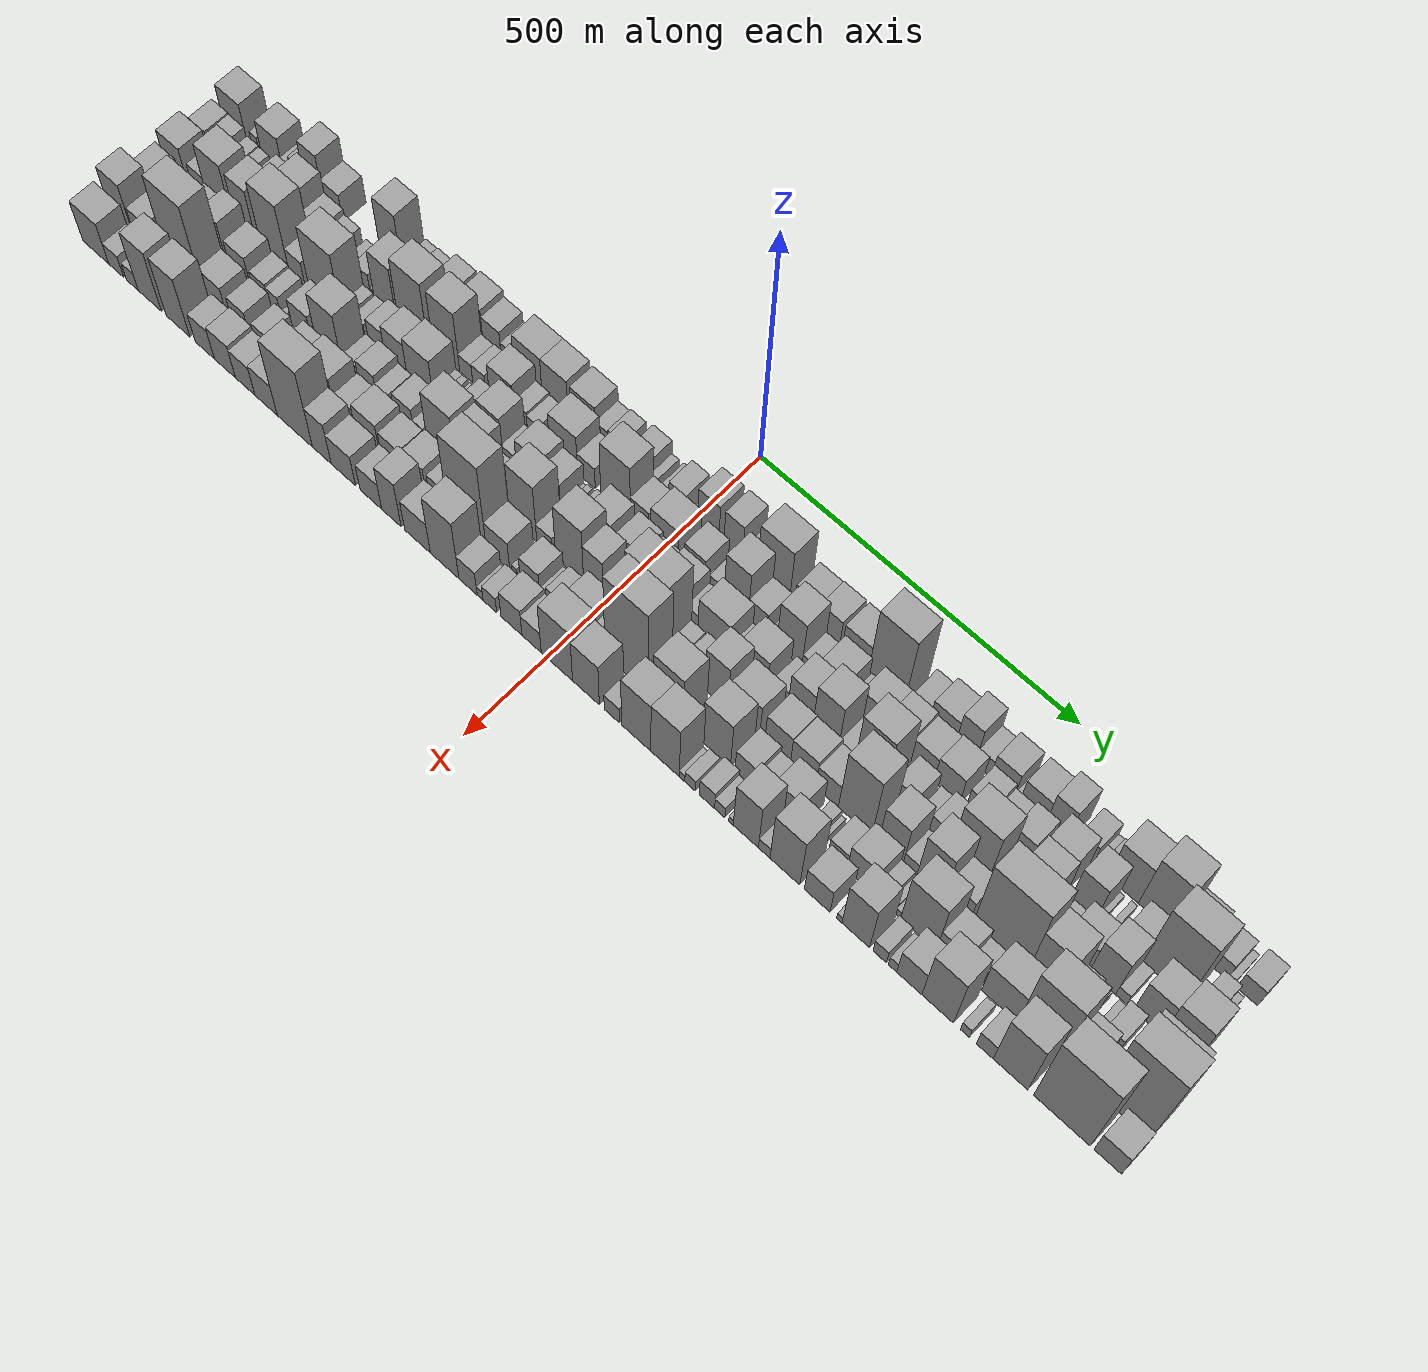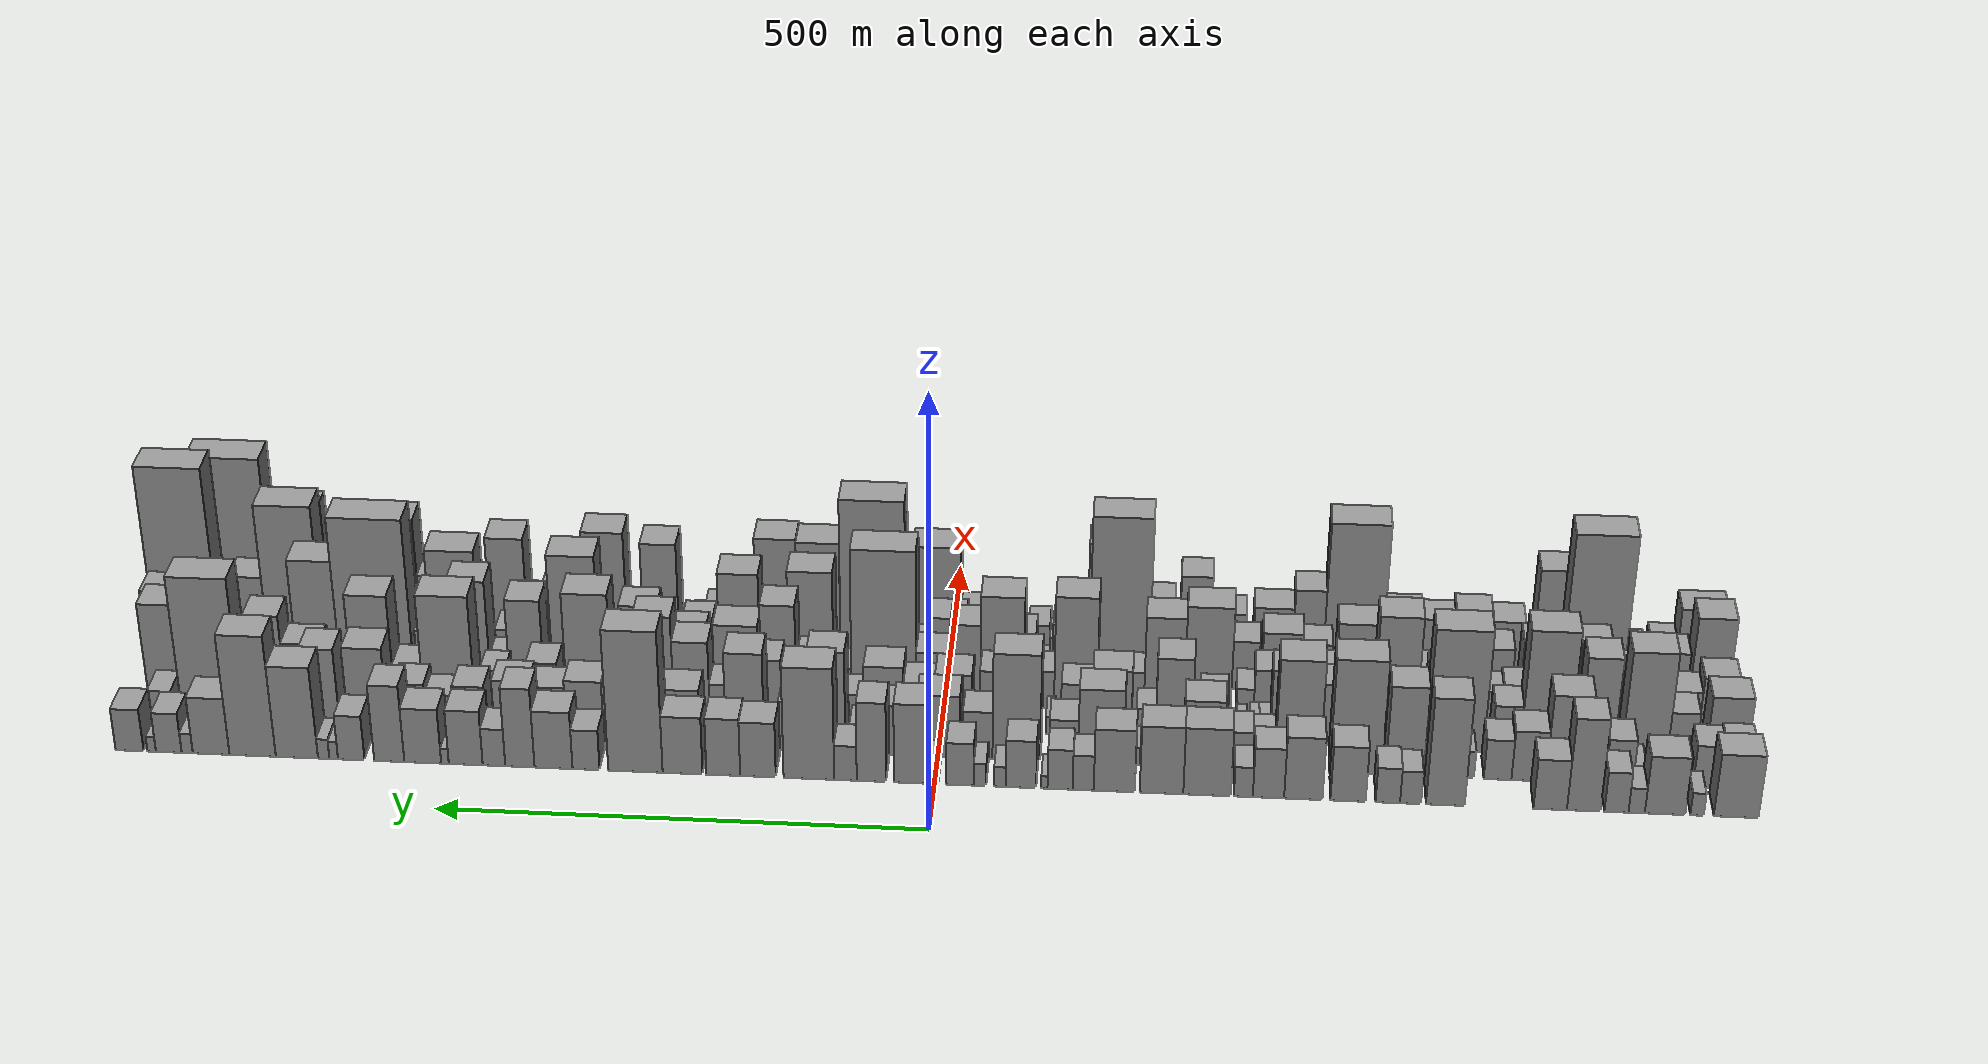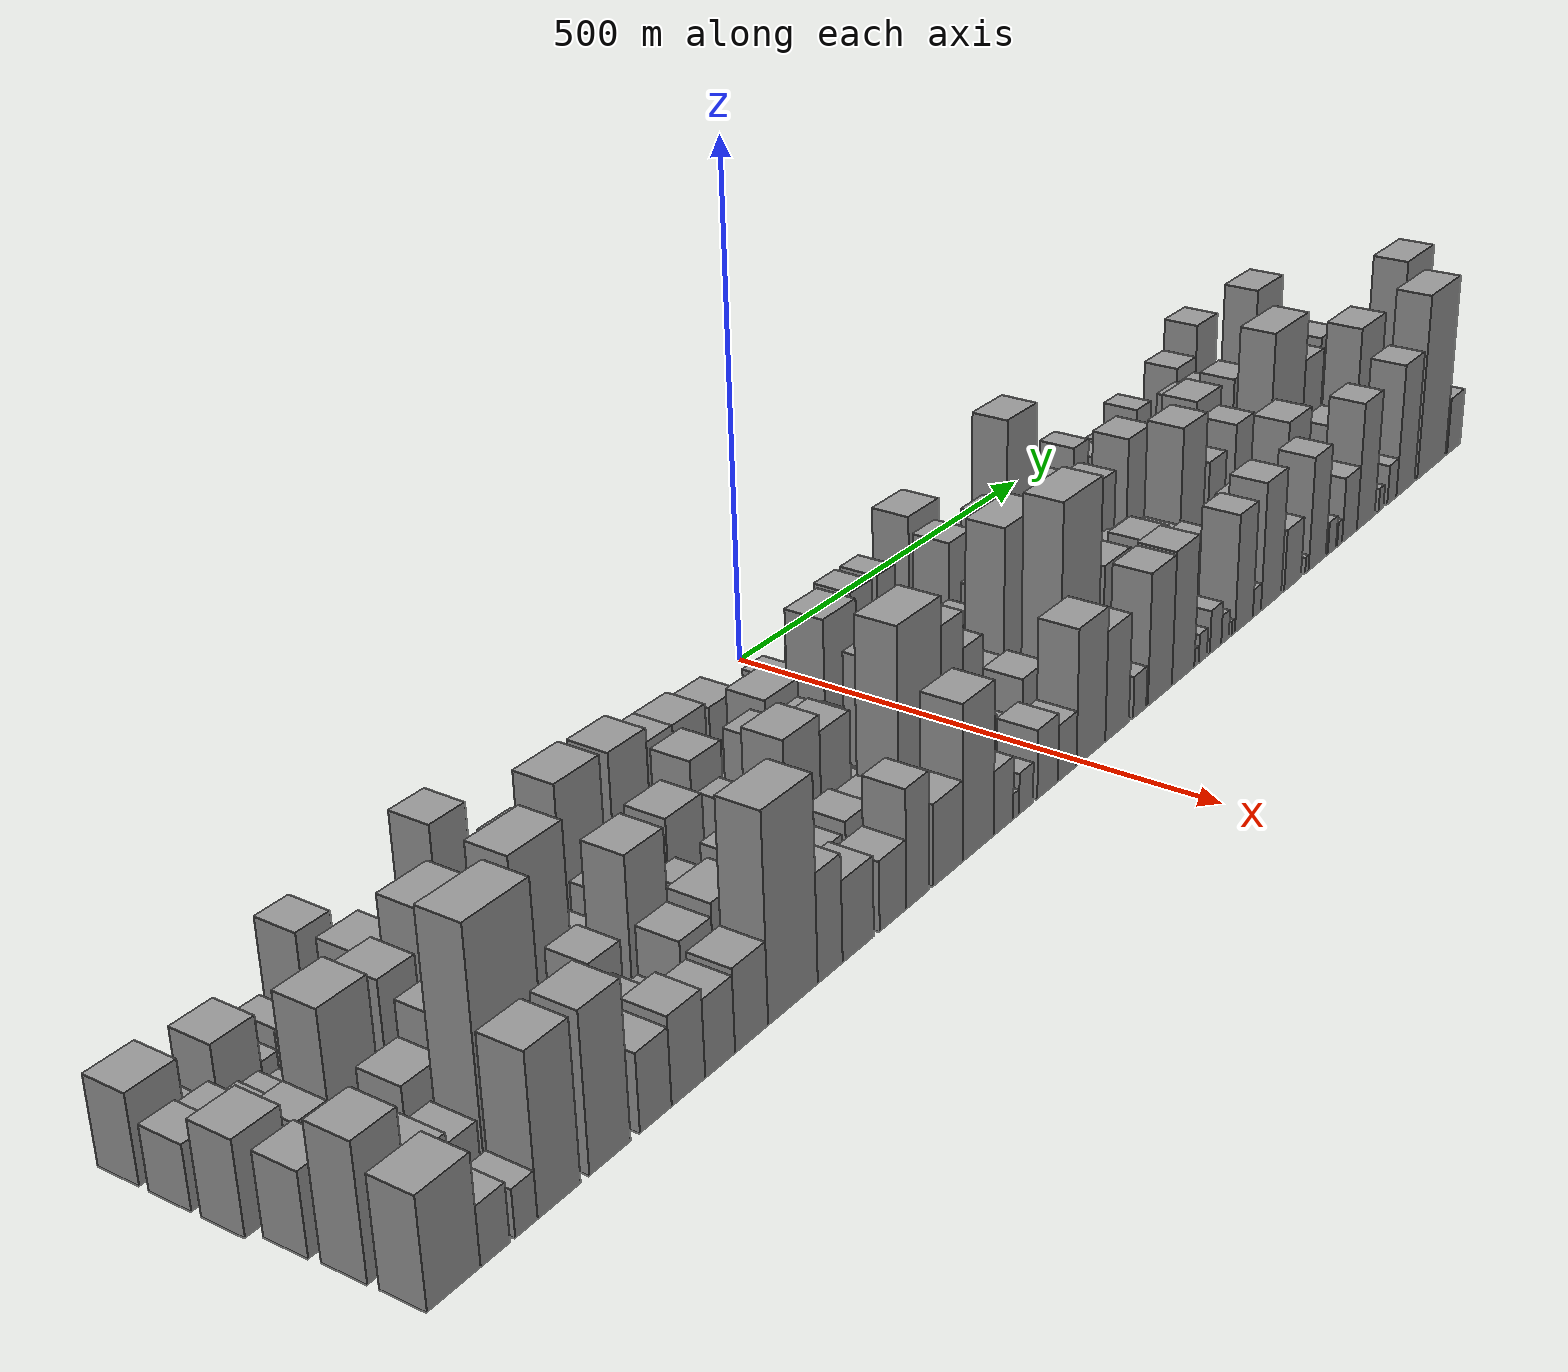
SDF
<sdf version="1.6">
 <world name="default">
  <scene>
   <sky><clouds><speed>12</speed></clouds></sky>
   <ambient>0.4 0.4 0.4 1</ambient>
   <background>0.7 0.7 0.7 1</background>
   <shadows>1</shadows>
  </scene>
  <gravity>0 0 -9.8066</gravity>
  <magnetic_field>6e-06 2.3e-05 -4.2e-05</magnetic_field>
  <physics default="0" name="default_physics" type="ode">
   <ode>
    <solver>
     <type>quick</type>
     <iters>10</iters>
     <sor>1.0</sor>
     <use_dynamic_moi_rescaling>0</use_dynamic_moi_rescaling>
    </solver>
    <constraints>
     <cfm>0</cfm>
     <erp>0.2</erp>
     <contact_max_correcting_vel>100</contact_max_correcting_vel>
     <contact_surface_layer>0.001</contact_surface_layer>
    </constraints>
   </ode>
   <max_step_size>0.004</max_step_size>
   <real_time_factor>1</real_time_factor>
   <real_time_update_rate>250</real_time_update_rate>
  </physics>
  <light name="sun" type="directional">
   <pose>0 0 10 0 0 0</pose>
   <diffuse>0.8 0.8 0.8 1</diffuse>
   <specular>0.2 0.2 0.2 1</specular>
   <attenuation>
    <range>1000</range>
    <constant>0.9</constant>
    <linear>0.01</linear>
    <quadratic>0.001</quadratic>
   </attenuation>
   <direction>-0.5 0.1 -0.9</direction>
  </light>
  <model name="building_1">
   <static>1</static>
   <pose>100.0000 -807.7736 0 0.000000 0.000000 0.000000</pose>
   <link name="link">
    <pose>0 0 37.50 0 0 0</pose>
    <collision name="collision"><geometry><box><size>40.0000 44.4528 75.0000</size></box></geometry></collision>
    <visual name="visual">
     <cast_shadows>0</cast_shadows>
     <geometry><box><size>40.0000 44.4528 75.0000</size></box></geometry>
     <material>
      <script>
       <uri>model://grey_wall/materials/scripts</uri>
       <uri>model://grey_wall/materials/textures</uri>
       <name>vrc/grey_wall</name>
      </script>
     </material>
    </visual>
   </link>
  </model>
  <model name="building_2">
   <static>1</static>
   <pose>100.0000 -768.8524 0 0.000000 0.000000 0.000000</pose>
   <link name="link">
    <pose>0 0 13.50 0 0 0</pose>
    <collision name="collision"><geometry><box><size>40.0000 13.3897 27.0000</size></box></geometry></collision>
    <visual name="visual">
     <cast_shadows>0</cast_shadows>
     <geometry><box><size>40.0000 13.3897 27.0000</size></box></geometry>
     <material>
      <script>
       <uri>model://grey_wall/materials/scripts</uri>
       <uri>model://grey_wall/materials/textures</uri>
       <name>vrc/grey_wall</name>
      </script>
     </material>
    </visual>
   </link>
  </model>
  <model name="building_3">
   <static>1</static>
   <pose>100.0000 -736.9591 0 0.000000 0.000000 0.000000</pose>
   <link name="link">
    <pose>0 0 34.50 0 0 0</pose>
    <collision name="collision"><geometry><box><size>40.0000 40.3968 69.0000</size></box></geometry></collision>
    <visual name="visual">
     <cast_shadows>0</cast_shadows>
     <geometry><box><size>40.0000 40.3968 69.0000</size></box></geometry>
     <material>
      <script>
       <uri>model://grey_wall/materials/scripts</uri>
       <uri>model://grey_wall/materials/textures</uri>
       <name>vrc/grey_wall</name>
      </script>
     </material>
    </visual>
   </link>
  </model>
  <model name="building_4">
   <static>1</static>
   <pose>100.0000 -708.5903 0 0.000000 0.000000 0.000000</pose>
   <link name="link">
    <pose>0 0 15.00 0 0 0</pose>
    <collision name="collision"><geometry><box><size>40.0000 16.3408 30.0000</size></box></geometry></collision>
    <visual name="visual">
     <cast_shadows>0</cast_shadows>
     <geometry><box><size>40.0000 16.3408 30.0000</size></box></geometry>
     <material>
      <script>
       <uri>model://grey_wall/materials/scripts</uri>
       <uri>model://grey_wall/materials/textures</uri>
       <name>vrc/grey_wall</name>
      </script>
     </material>
    </visual>
   </link>
  </model>
  <model name="building_5">
   <static>1</static>
   <pose>100.0000 -688.3928 0 0.000000 0.000000 0.000000</pose>
   <link name="link">
    <pose>0 0 24.00 0 0 0</pose>
    <collision name="collision"><geometry><box><size>40.0000 24.0543 48.0000</size></box></geometry></collision>
    <visual name="visual">
     <cast_shadows>0</cast_shadows>
     <geometry><box><size>40.0000 24.0543 48.0000</size></box></geometry>
     <material>
      <script>
       <uri>model://grey_wall/materials/scripts</uri>
       <uri>model://grey_wall/materials/textures</uri>
       <name>vrc/grey_wall</name>
      </script>
     </material>
    </visual>
   </link>
  </model>
  <model name="building_6">
   <static>1</static>
   <pose>100.0000 -655.6085 0 0.000000 0.000000 0.000000</pose>
   <link name="link">
    <pose>0 0 55.50 0 0 0</pose>
    <collision name="collision"><geometry><box><size>40.0000 33.5143 111.0000</size></box></geometry></collision>
    <visual name="visual">
     <cast_shadows>0</cast_shadows>
     <geometry><box><size>40.0000 33.5143 111.0000</size></box></geometry>
     <material>
      <script>
       <uri>model://grey_wall/materials/scripts</uri>
       <uri>model://grey_wall/materials/textures</uri>
       <name>vrc/grey_wall</name>
      </script>
     </material>
    </visual>
   </link>
  </model>
  <model name="building_7">
   <static>1</static>
   <pose>100.0000 -622.0648 0 0.000000 0.000000 0.000000</pose>
   <link name="link">
    <pose>0 0 30.00 0 0 0</pose>
    <collision name="collision"><geometry><box><size>40.0000 33.5730 60.0000</size></box></geometry></collision>
    <visual name="visual">
     <cast_shadows>0</cast_shadows>
     <geometry><box><size>40.0000 33.5730 60.0000</size></box></geometry>
     <material>
      <script>
       <uri>model://grey_wall/materials/scripts</uri>
       <uri>model://grey_wall/materials/textures</uri>
       <name>vrc/grey_wall</name>
      </script>
     </material>
    </visual>
   </link>
  </model>
  <model name="building_8">
   <static>1</static>
   <pose>100.0000 -516.9023 0 0.000000 0.000000 0.000000</pose>
   <link name="link">
    <pose>0 0 64.50 0 0 0</pose>
    <collision name="collision"><geometry><box><size>40.0000 38.9173 129.0000</size></box></geometry></collision>
    <visual name="visual">
     <cast_shadows>0</cast_shadows>
     <geometry><box><size>40.0000 38.9173 129.0000</size></box></geometry>
     <material>
      <script>
       <uri>model://grey_wall/materials/scripts</uri>
       <uri>model://grey_wall/materials/textures</uri>
       <name>vrc/grey_wall</name>
      </script>
     </material>
    </visual>
   </link>
  </model>
  <model name="building_9">
   <static>1</static>
   <pose>100.0000 -481.9084 0 0.000000 0.000000 0.000000</pose>
   <link name="link">
    <pose>0 0 19.50 0 0 0</pose>
    <collision name="collision"><geometry><box><size>40.0000 21.0706 39.0000</size></box></geometry></collision>
    <visual name="visual">
     <cast_shadows>0</cast_shadows>
     <geometry><box><size>40.0000 21.0706 39.0000</size></box></geometry>
     <material>
      <script>
       <uri>model://grey_wall/materials/scripts</uri>
       <uri>model://grey_wall/materials/textures</uri>
       <name>vrc/grey_wall</name>
      </script>
     </material>
    </visual>
   </link>
  </model>
  <model name="building_10">
   <static>1</static>
   <pose>100.0000 -459.0425 0 0.000000 0.000000 0.000000</pose>
   <link name="link">
    <pose>0 0 21.00 0 0 0</pose>
    <collision name="collision"><geometry><box><size>40.0000 24.6611 42.0000</size></box></geometry></collision>
    <visual name="visual">
     <cast_shadows>0</cast_shadows>
     <geometry><box><size>40.0000 24.6611 42.0000</size></box></geometry>
     <material>
      <script>
       <uri>model://grey_wall/materials/scripts</uri>
       <uri>model://grey_wall/materials/textures</uri>
       <name>vrc/grey_wall</name>
      </script>
     </material>
    </visual>
   </link>
  </model>
  <model name="building_11">
   <static>1</static>
   <pose>100.0000 -418.9198 0 0.000000 0.000000 0.000000</pose>
   <link name="link">
    <pose>0 0 33.00 0 0 0</pose>
    <collision name="collision"><geometry><box><size>40.0000 35.5843 66.0000</size></box></geometry></collision>
    <visual name="visual">
     <cast_shadows>0</cast_shadows>
     <geometry><box><size>40.0000 35.5843 66.0000</size></box></geometry>
     <material>
      <script>
       <uri>model://grey_wall/materials/scripts</uri>
       <uri>model://grey_wall/materials/textures</uri>
       <name>vrc/grey_wall</name>
      </script>
     </material>
    </visual>
   </link>
  </model>
  <model name="building_12">
   <static>1</static>
   <pose>100.0000 -373.7476 0 0.000000 0.000000 0.000000</pose>
   <link name="link">
    <pose>0 0 37.50 0 0 0</pose>
    <collision name="collision"><geometry><box><size>40.0000 38.7602 75.0000</size></box></geometry></collision>
    <visual name="visual">
     <cast_shadows>0</cast_shadows>
     <geometry><box><size>40.0000 38.7602 75.0000</size></box></geometry>
     <material>
      <script>
       <uri>model://grey_wall/materials/scripts</uri>
       <uri>model://grey_wall/materials/textures</uri>
       <name>vrc/grey_wall</name>
      </script>
     </material>
    </visual>
   </link>
  </model>
  <model name="building_13">
   <static>1</static>
   <pose>100.0000 -338.5559 0 0.000000 0.000000 0.000000</pose>
   <link name="link">
    <pose>0 0 30.00 0 0 0</pose>
    <collision name="collision"><geometry><box><size>40.0000 31.6232 60.0000</size></box></geometry></collision>
    <visual name="visual">
     <cast_shadows>0</cast_shadows>
     <geometry><box><size>40.0000 31.6232 60.0000</size></box></geometry>
     <material>
      <script>
       <uri>model://grey_wall/materials/scripts</uri>
       <uri>model://grey_wall/materials/textures</uri>
       <name>vrc/grey_wall</name>
      </script>
     </material>
    </visual>
   </link>
  </model>
  <model name="building_14">
   <static>1</static>
   <pose>100.0000 -313.1680 0 0.000000 0.000000 0.000000</pose>
   <link name="link">
    <pose>0 0 18.00 0 0 0</pose>
    <collision name="collision"><geometry><box><size>40.0000 19.1526 36.0000</size></box></geometry></collision>
    <visual name="visual">
     <cast_shadows>0</cast_shadows>
     <geometry><box><size>40.0000 19.1526 36.0000</size></box></geometry>
     <material>
      <script>
       <uri>model://grey_wall/materials/scripts</uri>
       <uri>model://grey_wall/materials/textures</uri>
       <name>vrc/grey_wall</name>
      </script>
     </material>
    </visual>
   </link>
  </model>
  <model name="building_15">
   <static>1</static>
   <pose>100.0000 -276.4596 0 0.000000 0.000000 0.000000</pose>
   <link name="link">
    <pose>0 0 40.50 0 0 0</pose>
    <collision name="collision"><geometry><box><size>40.0000 48.2642 81.0000</size></box></geometry></collision>
    <visual name="visual">
     <cast_shadows>0</cast_shadows>
     <geometry><box><size>40.0000 48.2642 81.0000</size></box></geometry>
     <material>
      <script>
       <uri>model://grey_wall/materials/scripts</uri>
       <uri>model://grey_wall/materials/textures</uri>
       <name>vrc/grey_wall</name>
      </script>
     </material>
    </visual>
   </link>
  </model>
  <model name="building_16">
   <static>1</static>
   <pose>100.0000 -230.2445 0 0.000000 0.000000 0.000000</pose>
   <link name="link">
    <pose>0 0 40.50 0 0 0</pose>
    <collision name="collision"><geometry><box><size>40.0000 44.1661 81.0000</size></box></geometry></collision>
    <visual name="visual">
     <cast_shadows>0</cast_shadows>
     <geometry><box><size>40.0000 44.1661 81.0000</size></box></geometry>
     <material>
      <script>
       <uri>model://grey_wall/materials/scripts</uri>
       <uri>model://grey_wall/materials/textures</uri>
       <name>vrc/grey_wall</name>
      </script>
     </material>
    </visual>
   </link>
  </model>
  <model name="building_17">
   <static>1</static>
   <pose>100.0000 -182.2852 0 0.000000 0.000000 0.000000</pose>
   <link name="link">
    <pose>0 0 37.50 0 0 0</pose>
    <collision name="collision"><geometry><box><size>40.0000 41.7525 75.0000</size></box></geometry></collision>
    <visual name="visual">
     <cast_shadows>0</cast_shadows>
     <geometry><box><size>40.0000 41.7525 75.0000</size></box></geometry>
     <material>
      <script>
       <uri>model://grey_wall/materials/scripts</uri>
       <uri>model://grey_wall/materials/textures</uri>
       <name>vrc/grey_wall</name>
      </script>
     </material>
    </visual>
   </link>
  </model>
  <model name="building_18">
   <static>1</static>
   <pose>100.0000 -150.6923 0 0.000000 0.000000 0.000000</pose>
   <link name="link">
    <pose>0 0 21.00 0 0 0</pose>
    <collision name="collision"><geometry><box><size>40.0000 21.4334 42.0000</size></box></geometry></collision>
    <visual name="visual">
     <cast_shadows>0</cast_shadows>
     <geometry><box><size>40.0000 21.4334 42.0000</size></box></geometry>
     <material>
      <script>
       <uri>model://grey_wall/materials/scripts</uri>
       <uri>model://grey_wall/materials/textures</uri>
       <name>vrc/grey_wall</name>
      </script>
     </material>
    </visual>
   </link>
  </model>
  <model name="building_19">
   <static>1</static>
   <pose>100.0000 -127.1408 0 0.000000 0.000000 0.000000</pose>
   <link name="link">
    <pose>0 0 24.00 0 0 0</pose>
    <collision name="collision"><geometry><box><size>40.0000 25.6695 48.0000</size></box></geometry></collision>
    <visual name="visual">
     <cast_shadows>0</cast_shadows>
     <geometry><box><size>40.0000 25.6695 48.0000</size></box></geometry>
     <material>
      <script>
       <uri>model://grey_wall/materials/scripts</uri>
       <uri>model://grey_wall/materials/textures</uri>
       <name>vrc/grey_wall</name>
      </script>
     </material>
    </visual>
   </link>
  </model>
  <model name="building_20">
   <static>1</static>
   <pose>100.0000 -111.0796 0 0.000000 0.000000 0.000000</pose>
   <link name="link">
    <pose>0 0 7.50 0 0 0</pose>
    <collision name="collision"><geometry><box><size>40.0000 6.4531 15.0000</size></box></geometry></collision>
    <visual name="visual">
     <cast_shadows>0</cast_shadows>
     <geometry><box><size>40.0000 6.4531 15.0000</size></box></geometry>
     <material>
      <script>
       <uri>model://grey_wall/materials/scripts</uri>
       <uri>model://grey_wall/materials/textures</uri>
       <name>vrc/grey_wall</name>
      </script>
     </material>
    </visual>
   </link>
  </model>
  <model name="building_21">
   <static>1</static>
   <pose>100.0000 -87.2297 0 0.000000 0.000000 0.000000</pose>
   <link name="link">
    <pose>0 0 28.50 0 0 0</pose>
    <collision name="collision"><geometry><box><size>40.0000 31.2466 57.0000</size></box></geometry></collision>
    <visual name="visual">
     <cast_shadows>0</cast_shadows>
     <geometry><box><size>40.0000 31.2466 57.0000</size></box></geometry>
     <material>
      <script>
       <uri>model://grey_wall/materials/scripts</uri>
       <uri>model://grey_wall/materials/textures</uri>
       <name>vrc/grey_wall</name>
      </script>
     </material>
    </visual>
   </link>
  </model>
  <model name="building_22">
   <static>1</static>
   <pose>100.0000 -65.7462 0 0.000000 0.000000 0.000000</pose>
   <link name="link">
    <pose>0 0 12.00 0 0 0</pose>
    <collision name="collision"><geometry><box><size>40.0000 11.7204 24.0000</size></box></geometry></collision>
    <visual name="visual">
     <cast_shadows>0</cast_shadows>
     <geometry><box><size>40.0000 11.7204 24.0000</size></box></geometry>
     <material>
      <script>
       <uri>model://grey_wall/materials/scripts</uri>
       <uri>model://grey_wall/materials/textures</uri>
       <name>vrc/grey_wall</name>
      </script>
     </material>
    </visual>
   </link>
  </model>
  <model name="building_23">
   <static>1</static>
   <pose>100.0000 -45.4646 0 0.000000 0.000000 0.000000</pose>
   <link name="link">
    <pose>0 0 13.50 0 0 0</pose>
    <collision name="collision"><geometry><box><size>40.0000 12.8429 27.0000</size></box></geometry></collision>
    <visual name="visual">
     <cast_shadows>0</cast_shadows>
     <geometry><box><size>40.0000 12.8429 27.0000</size></box></geometry>
     <material>
      <script>
       <uri>model://grey_wall/materials/scripts</uri>
       <uri>model://grey_wall/materials/textures</uri>
       <name>vrc/grey_wall</name>
      </script>
     </material>
    </visual>
   </link>
  </model>
  <model name="building_24">
   <static>1</static>
   <pose>100.0000 -24.9906 0 0.000000 0.000000 0.000000</pose>
   <link name="link">
    <pose>0 0 25.50 0 0 0</pose>
    <collision name="collision"><geometry><box><size>40.0000 28.1051 51.0000</size></box></geometry></collision>
    <visual name="visual">
     <cast_shadows>0</cast_shadows>
     <geometry><box><size>40.0000 28.1051 51.0000</size></box></geometry>
     <material>
      <script>
       <uri>model://grey_wall/materials/scripts</uri>
       <uri>model://grey_wall/materials/textures</uri>
       <name>vrc/grey_wall</name>
      </script>
     </material>
    </visual>
   </link>
  </model>
  <model name="building_25">
   <static>1</static>
   <pose>100.0000 2.5151 0 0.000000 0.000000 0.000000</pose>
   <link name="link">
    <pose>0 0 13.50 0 0 0</pose>
    <collision name="collision"><geometry><box><size>40.0000 10.9063 27.0000</size></box></geometry></collision>
    <visual name="visual">
     <cast_shadows>0</cast_shadows>
     <geometry><box><size>40.0000 10.9063 27.0000</size></box></geometry>
     <material>
      <script>
       <uri>model://grey_wall/materials/scripts</uri>
       <uri>model://grey_wall/materials/textures</uri>
       <name>vrc/grey_wall</name>
      </script>
     </material>
    </visual>
   </link>
  </model>
  <model name="building_26">
   <static>1</static>
   <pose>100.0000 25.2675 0 0.000000 0.000000 0.000000</pose>
   <link name="link">
    <pose>0 0 48.00 0 0 0</pose>
    <collision name="collision"><geometry><box><size>40.0000 34.5985 96.0000</size></box></geometry></collision>
    <visual name="visual">
     <cast_shadows>0</cast_shadows>
     <geometry><box><size>40.0000 34.5985 96.0000</size></box></geometry>
     <material>
      <script>
       <uri>model://grey_wall/materials/scripts</uri>
       <uri>model://grey_wall/materials/textures</uri>
       <name>vrc/grey_wall</name>
      </script>
     </material>
    </visual>
   </link>
  </model>
  <model name="building_27">
   <static>1</static>
   <pose>100.0000 65.6006 0 0.000000 0.000000 0.000000</pose>
   <link name="link">
    <pose>0 0 48.00 0 0 0</pose>
    <collision name="collision"><geometry><box><size>40.0000 30.0678 96.0000</size></box></geometry></collision>
    <visual name="visual">
     <cast_shadows>0</cast_shadows>
     <geometry><box><size>40.0000 30.0678 96.0000</size></box></geometry>
     <material>
      <script>
       <uri>model://grey_wall/materials/scripts</uri>
       <uri>model://grey_wall/materials/textures</uri>
       <name>vrc/grey_wall</name>
      </script>
     </material>
    </visual>
   </link>
  </model>
  <model name="building_28">
   <static>1</static>
   <pose>100.0000 92.2088 0 0.000000 0.000000 0.000000</pose>
   <link name="link">
    <pose>0 0 21.00 0 0 0</pose>
    <collision name="collision"><geometry><box><size>40.0000 23.1486 42.0000</size></box></geometry></collision>
    <visual name="visual">
     <cast_shadows>0</cast_shadows>
     <geometry><box><size>40.0000 23.1486 42.0000</size></box></geometry>
     <material>
      <script>
       <uri>model://grey_wall/materials/scripts</uri>
       <uri>model://grey_wall/materials/textures</uri>
       <name>vrc/grey_wall</name>
      </script>
     </material>
    </visual>
   </link>
  </model>
  <model name="building_29">
   <static>1</static>
   <pose>100.0000 129.7440 0 0.000000 0.000000 0.000000</pose>
   <link name="link">
    <pose>0 0 67.50 0 0 0</pose>
    <collision name="collision"><geometry><box><size>40.0000 51.9217 135.0000</size></box></geometry></collision>
    <visual name="visual">
     <cast_shadows>0</cast_shadows>
     <geometry><box><size>40.0000 51.9217 135.0000</size></box></geometry>
     <material>
      <script>
       <uri>model://grey_wall/materials/scripts</uri>
       <uri>model://grey_wall/materials/textures</uri>
       <name>vrc/grey_wall</name>
      </script>
     </material>
    </visual>
   </link>
  </model>
  <model name="building_30">
   <static>1</static>
   <pose>100.0000 182.0196 0 0.000000 0.000000 0.000000</pose>
   <link name="link">
    <pose>0 0 33.00 0 0 0</pose>
    <collision name="collision"><geometry><box><size>40.0000 36.6295 66.0000</size></box></geometry></collision>
    <visual name="visual">
     <cast_shadows>0</cast_shadows>
     <geometry><box><size>40.0000 36.6295 66.0000</size></box></geometry>
     <material>
      <script>
       <uri>model://grey_wall/materials/scripts</uri>
       <uri>model://grey_wall/materials/textures</uri>
       <name>vrc/grey_wall</name>
      </script>
     </material>
    </visual>
   </link>
  </model>
  <model name="building_31">
   <static>1</static>
   <pose>100.0000 217.7204 0 0.000000 0.000000 0.000000</pose>
   <link name="link">
    <pose>0 0 34.50 0 0 0</pose>
    <collision name="collision"><geometry><box><size>40.0000 34.7721 69.0000</size></box></geometry></collision>
    <visual name="visual">
     <cast_shadows>0</cast_shadows>
     <geometry><box><size>40.0000 34.7721 69.0000</size></box></geometry>
     <material>
      <script>
       <uri>model://grey_wall/materials/scripts</uri>
       <uri>model://grey_wall/materials/textures</uri>
       <name>vrc/grey_wall</name>
      </script>
     </material>
    </visual>
   </link>
  </model>
  <model name="building_32">
   <static>1</static>
   <pose>100.0000 259.6823 0 0.000000 0.000000 0.000000</pose>
   <link name="link">
    <pose>0 0 34.50 0 0 0</pose>
    <collision name="collision"><geometry><box><size>40.0000 41.1518 69.0000</size></box></geometry></collision>
    <visual name="visual">
     <cast_shadows>0</cast_shadows>
     <geometry><box><size>40.0000 41.1518 69.0000</size></box></geometry>
     <material>
      <script>
       <uri>model://grey_wall/materials/scripts</uri>
       <uri>model://grey_wall/materials/textures</uri>
       <name>vrc/grey_wall</name>
      </script>
     </material>
    </visual>
   </link>
  </model>
  <model name="building_33">
   <static>1</static>
   <pose>100.0000 308.3205 0 0.000000 0.000000 0.000000</pose>
   <link name="link">
    <pose>0 0 85.50 0 0 0</pose>
    <collision name="collision"><geometry><box><size>40.0000 56.1244 171.0000</size></box></geometry></collision>
    <visual name="visual">
     <cast_shadows>0</cast_shadows>
     <geometry><box><size>40.0000 56.1244 171.0000</size></box></geometry>
     <material>
      <script>
       <uri>model://grey_wall/materials/scripts</uri>
       <uri>model://grey_wall/materials/textures</uri>
       <name>vrc/grey_wall</name>
      </script>
     </material>
    </visual>
   </link>
  </model>
  <model name="building_34">
   <static>1</static>
   <pose>100.0000 359.3745 0 0.000000 0.000000 0.000000</pose>
   <link name="link">
    <pose>0 0 24.00 0 0 0</pose>
    <collision name="collision"><geometry><box><size>40.0000 27.9836 48.0000</size></box></geometry></collision>
    <visual name="visual">
     <cast_shadows>0</cast_shadows>
     <geometry><box><size>40.0000 27.9836 48.0000</size></box></geometry>
     <material>
      <script>
       <uri>model://grey_wall/materials/scripts</uri>
       <uri>model://grey_wall/materials/textures</uri>
       <name>vrc/grey_wall</name>
      </script>
     </material>
    </visual>
   </link>
  </model>
  <model name="building_35">
   <static>1</static>
   <pose>100.0000 393.0506 0 0.000000 0.000000 0.000000</pose>
   <link name="link">
    <pose>0 0 34.50 0 0 0</pose>
    <collision name="collision"><geometry><box><size>40.0000 39.3685 69.0000</size></box></geometry></collision>
    <visual name="visual">
     <cast_shadows>0</cast_shadows>
     <geometry><box><size>40.0000 39.3685 69.0000</size></box></geometry>
     <material>
      <script>
       <uri>model://grey_wall/materials/scripts</uri>
       <uri>model://grey_wall/materials/textures</uri>
       <name>vrc/grey_wall</name>
      </script>
     </material>
    </visual>
   </link>
  </model>
  <model name="building_36">
   <static>1</static>
   <pose>100.0000 427.8991 0 0.000000 0.000000 0.000000</pose>
   <link name="link">
    <pose>0 0 48.00 0 0 0</pose>
    <collision name="collision"><geometry><box><size>40.0000 30.3287 96.0000</size></box></geometry></collision>
    <visual name="visual">
     <cast_shadows>0</cast_shadows>
     <geometry><box><size>40.0000 30.3287 96.0000</size></box></geometry>
     <material>
      <script>
       <uri>model://grey_wall/materials/scripts</uri>
       <uri>model://grey_wall/materials/textures</uri>
       <name>vrc/grey_wall</name>
      </script>
     </material>
    </visual>
   </link>
  </model>
  <model name="building_37">
   <static>1</static>
   <pose>100.0000 454.7951 0 0.000000 0.000000 0.000000</pose>
   <link name="link">
    <pose>0 0 22.50 0 0 0</pose>
    <collision name="collision"><geometry><box><size>40.0000 23.4633 45.0000</size></box></geometry></collision>
    <visual name="visual">
     <cast_shadows>0</cast_shadows>
     <geometry><box><size>40.0000 23.4633 45.0000</size></box></geometry>
     <material>
      <script>
       <uri>model://grey_wall/materials/scripts</uri>
       <uri>model://grey_wall/materials/textures</uri>
       <name>vrc/grey_wall</name>
      </script>
     </material>
    </visual>
   </link>
  </model>
  <model name="building_38">
   <static>1</static>
   <pose>100.0000 484.1768 0 0.000000 0.000000 0.000000</pose>
   <link name="link">
    <pose>0 0 33.00 0 0 0</pose>
    <collision name="collision"><geometry><box><size>40.0000 35.2999 66.0000</size></box></geometry></collision>
    <visual name="visual">
     <cast_shadows>0</cast_shadows>
     <geometry><box><size>40.0000 35.2999 66.0000</size></box></geometry>
     <material>
      <script>
       <uri>model://grey_wall/materials/scripts</uri>
       <uri>model://grey_wall/materials/textures</uri>
       <name>vrc/grey_wall</name>
      </script>
     </material>
    </visual>
   </link>
  </model>
  <model name="building_39">
   <static>1</static>
   <pose>100.0000 505.7400 0 0.000000 0.000000 0.000000</pose>
   <link name="link">
    <pose>0 0 9.00 0 0 0</pose>
    <collision name="collision"><geometry><box><size>40.0000 7.8266 18.0000</size></box></geometry></collision>
    <visual name="visual">
     <cast_shadows>0</cast_shadows>
     <geometry><box><size>40.0000 7.8266 18.0000</size></box></geometry>
     <material>
      <script>
       <uri>model://grey_wall/materials/scripts</uri>
       <uri>model://grey_wall/materials/textures</uri>
       <name>vrc/grey_wall</name>
      </script>
     </material>
    </visual>
   </link>
  </model>
  <model name="building_40">
   <static>1</static>
   <pose>100.0000 528.8231 0 0.000000 0.000000 0.000000</pose>
   <link name="link">
    <pose>0 0 33.00 0 0 0</pose>
    <collision name="collision"><geometry><box><size>40.0000 38.3396 66.0000</size></box></geometry></collision>
    <visual name="visual">
     <cast_shadows>0</cast_shadows>
     <geometry><box><size>40.0000 38.3396 66.0000</size></box></geometry>
     <material>
      <script>
       <uri>model://grey_wall/materials/scripts</uri>
       <uri>model://grey_wall/materials/textures</uri>
       <name>vrc/grey_wall</name>
      </script>
     </material>
    </visual>
   </link>
  </model>
  <model name="building_41">
   <static>1</static>
   <pose>100.0000 563.7288 0 0.000000 0.000000 0.000000</pose>
   <link name="link">
    <pose>0 0 46.50 0 0 0</pose>
    <collision name="collision"><geometry><box><size>40.0000 31.4718 93.0000</size></box></geometry></collision>
    <visual name="visual">
     <cast_shadows>0</cast_shadows>
     <geometry><box><size>40.0000 31.4718 93.0000</size></box></geometry>
     <material>
      <script>
       <uri>model://grey_wall/materials/scripts</uri>
       <uri>model://grey_wall/materials/textures</uri>
       <name>vrc/grey_wall</name>
      </script>
     </material>
    </visual>
   </link>
  </model>
  <model name="building_42">
   <static>1</static>
   <pose>100.0000 603.3190 0 0.000000 0.000000 0.000000</pose>
   <link name="link">
    <pose>0 0 27.00 0 0 0</pose>
    <collision name="collision"><geometry><box><size>40.0000 27.7086 54.0000</size></box></geometry></collision>
    <visual name="visual">
     <cast_shadows>0</cast_shadows>
     <geometry><box><size>40.0000 27.7086 54.0000</size></box></geometry>
     <material>
      <script>
       <uri>model://grey_wall/materials/scripts</uri>
       <uri>model://grey_wall/materials/textures</uri>
       <name>vrc/grey_wall</name>
      </script>
     </material>
    </visual>
   </link>
  </model>
  <model name="building_43">
   <static>1</static>
   <pose>100.0000 621.6460 0 0.000000 0.000000 0.000000</pose>
   <link name="link">
    <pose>0 0 10.50 0 0 0</pose>
    <collision name="collision"><geometry><box><size>40.0000 8.9455 21.0000</size></box></geometry></collision>
    <visual name="visual">
     <cast_shadows>0</cast_shadows>
     <geometry><box><size>40.0000 8.9455 21.0000</size></box></geometry>
     <material>
      <script>
       <uri>model://grey_wall/materials/scripts</uri>
       <uri>model://grey_wall/materials/textures</uri>
       <name>vrc/grey_wall</name>
      </script>
     </material>
    </visual>
   </link>
  </model>
  <model name="building_44">
   <static>1</static>
   <pose>100.0000 632.0874 0 0.000000 0.000000 0.000000</pose>
   <link name="link">
    <pose>0 0 12.00 0 0 0</pose>
    <collision name="collision"><geometry><box><size>40.0000 11.9373 24.0000</size></box></geometry></collision>
    <visual name="visual">
     <cast_shadows>0</cast_shadows>
     <geometry><box><size>40.0000 11.9373 24.0000</size></box></geometry>
     <material>
      <script>
       <uri>model://grey_wall/materials/scripts</uri>
       <uri>model://grey_wall/materials/textures</uri>
       <name>vrc/grey_wall</name>
      </script>
     </material>
    </visual>
   </link>
  </model>
  <model name="building_45">
   <static>1</static>
   <pose>100.0000 660.1086 0 0.000000 0.000000 0.000000</pose>
   <link name="link">
    <pose>0 0 55.50 0 0 0</pose>
    <collision name="collision"><geometry><box><size>40.0000 44.1050 111.0000</size></box></geometry></collision>
    <visual name="visual">
     <cast_shadows>0</cast_shadows>
     <geometry><box><size>40.0000 44.1050 111.0000</size></box></geometry>
     <material>
      <script>
       <uri>model://grey_wall/materials/scripts</uri>
       <uri>model://grey_wall/materials/textures</uri>
       <name>vrc/grey_wall</name>
      </script>
     </material>
    </visual>
   </link>
  </model>
  <model name="building_46">
   <static>1</static>
   <pose>100.0000 706.3881 0 0.000000 0.000000 0.000000</pose>
   <link name="link">
    <pose>0 0 73.50 0 0 0</pose>
    <collision name="collision"><geometry><box><size>40.0000 48.4541 147.0000</size></box></geometry></collision>
    <visual name="visual">
     <cast_shadows>0</cast_shadows>
     <geometry><box><size>40.0000 48.4541 147.0000</size></box></geometry>
     <material>
      <script>
       <uri>model://grey_wall/materials/scripts</uri>
       <uri>model://grey_wall/materials/textures</uri>
       <name>vrc/grey_wall</name>
      </script>
     </material>
    </visual>
   </link>
  </model>
  <model name="building_47">
   <static>1</static>
   <pose>100.0000 749.8474 0 0.000000 0.000000 0.000000</pose>
   <link name="link">
    <pose>0 0 34.50 0 0 0</pose>
    <collision name="collision"><geometry><box><size>40.0000 38.4644 69.0000</size></box></geometry></collision>
    <visual name="visual">
     <cast_shadows>0</cast_shadows>
     <geometry><box><size>40.0000 38.4644 69.0000</size></box></geometry>
     <material>
      <script>
       <uri>model://grey_wall/materials/scripts</uri>
       <uri>model://grey_wall/materials/textures</uri>
       <name>vrc/grey_wall</name>
      </script>
     </material>
    </visual>
   </link>
  </model>
  <model name="building_48">
   <static>1</static>
   <pose>100.0000 774.9256 0 0.000000 0.000000 0.000000</pose>
   <link name="link">
    <pose>0 0 12.00 0 0 0</pose>
    <collision name="collision"><geometry><box><size>40.0000 11.6920 24.0000</size></box></geometry></collision>
    <visual name="visual">
     <cast_shadows>0</cast_shadows>
     <geometry><box><size>40.0000 11.6920 24.0000</size></box></geometry>
     <material>
      <script>
       <uri>model://grey_wall/materials/scripts</uri>
       <uri>model://grey_wall/materials/textures</uri>
       <name>vrc/grey_wall</name>
      </script>
     </material>
    </visual>
   </link>
  </model>
  <model name="building_49">
   <static>1</static>
   <pose>100.0000 794.2808 0 0.000000 0.000000 0.000000</pose>
   <link name="link">
    <pose>0 0 24.00 0 0 0</pose>
    <collision name="collision"><geometry><box><size>40.0000 27.0184 48.0000</size></box></geometry></collision>
    <visual name="visual">
     <cast_shadows>0</cast_shadows>
     <geometry><box><size>40.0000 27.0184 48.0000</size></box></geometry>
     <material>
      <script>
       <uri>model://grey_wall/materials/scripts</uri>
       <uri>model://grey_wall/materials/textures</uri>
       <name>vrc/grey_wall</name>
      </script>
     </material>
    </visual>
   </link>
  </model>
  <model name="building_50">
   <static>1</static>
   <pose>100.0000 812.2266 0 0.000000 0.000000 0.000000</pose>
   <link name="link">
    <pose>0 0 9.00 0 0 0</pose>
    <collision name="collision"><geometry><box><size>40.0000 8.8730 18.0000</size></box></geometry></collision>
    <visual name="visual">
     <cast_shadows>0</cast_shadows>
     <geometry><box><size>40.0000 8.8730 18.0000</size></box></geometry>
     <material>
      <script>
       <uri>model://grey_wall/materials/scripts</uri>
       <uri>model://grey_wall/materials/textures</uri>
       <name>vrc/grey_wall</name>
      </script>
     </material>
    </visual>
   </link>
  </model>
  <model name="building_51">
   <static>1</static>
   <pose>100.0000 835.4066 0 0.000000 0.000000 0.000000</pose>
   <link name="link">
    <pose>0 0 25.50 0 0 0</pose>
    <collision name="collision"><geometry><box><size>40.0000 29.4870 51.0000</size></box></geometry></collision>
    <visual name="visual">
     <cast_shadows>0</cast_shadows>
     <geometry><box><size>40.0000 29.4870 51.0000</size></box></geometry>
     <material>
      <script>
       <uri>model://grey_wall/materials/scripts</uri>
       <uri>model://grey_wall/materials/textures</uri>
       <name>vrc/grey_wall</name>
      </script>
     </material>
    </visual>
   </link>
  </model>
  <model name="building_52">
   <static>1</static>
   <pose>149.0000 -814.5044 0 0.000000 0.000000 0.000000</pose>
   <link name="link">
    <pose>0 0 27.00 0 0 0</pose>
    <collision name="collision"><geometry><box><size>40.0000 30.9913 54.0000</size></box></geometry></collision>
    <visual name="visual">
     <cast_shadows>0</cast_shadows>
     <geometry><box><size>40.0000 30.9913 54.0000</size></box></geometry>
     <material>
      <script>
       <uri>model://grey_wall/materials/scripts</uri>
       <uri>model://grey_wall/materials/textures</uri>
       <name>vrc/grey_wall</name>
      </script>
     </material>
    </visual>
   </link>
  </model>
  <model name="building_53">
   <static>1</static>
   <pose>149.0000 -784.4596 0 0.000000 0.000000 0.000000</pose>
   <link name="link">
    <pose>0 0 25.50 0 0 0</pose>
    <collision name="collision"><geometry><box><size>40.0000 29.0982 51.0000</size></box></geometry></collision>
    <visual name="visual">
     <cast_shadows>0</cast_shadows>
     <geometry><box><size>40.0000 29.0982 51.0000</size></box></geometry>
     <material>
      <script>
       <uri>model://grey_wall/materials/scripts</uri>
       <uri>model://grey_wall/materials/textures</uri>
       <name>vrc/grey_wall</name>
      </script>
     </material>
    </visual>
   </link>
  </model>
  <model name="building_54">
   <static>1</static>
   <pose>149.0000 -756.2330 0 0.000000 0.000000 0.000000</pose>
   <link name="link">
    <pose>0 0 18.00 0 0 0</pose>
    <collision name="collision"><geometry><box><size>40.0000 21.3550 36.0000</size></box></geometry></collision>
    <visual name="visual">
     <cast_shadows>0</cast_shadows>
     <geometry><box><size>40.0000 21.3550 36.0000</size></box></geometry>
     <material>
      <script>
       <uri>model://grey_wall/materials/scripts</uri>
       <uri>model://grey_wall/materials/textures</uri>
       <name>vrc/grey_wall</name>
      </script>
     </material>
    </visual>
   </link>
  </model>
  <model name="building_55">
   <static>1</static>
   <pose>149.0000 -736.3124 0 0.000000 0.000000 0.000000</pose>
   <link name="link">
    <pose>0 0 16.50 0 0 0</pose>
    <collision name="collision"><geometry><box><size>40.0000 18.4861 33.0000</size></box></geometry></collision>
    <visual name="visual">
     <cast_shadows>0</cast_shadows>
     <geometry><box><size>40.0000 18.4861 33.0000</size></box></geometry>
     <material>
      <script>
       <uri>model://grey_wall/materials/scripts</uri>
       <uri>model://grey_wall/materials/textures</uri>
       <name>vrc/grey_wall</name>
      </script>
     </material>
    </visual>
   </link>
  </model>
  <model name="building_56">
   <static>1</static>
   <pose>149.0000 -715.2313 0 0.000000 0.000000 0.000000</pose>
   <link name="link">
    <pose>0 0 12.00 0 0 0</pose>
    <collision name="collision"><geometry><box><size>40.0000 11.6762 24.0000</size></box></geometry></collision>
    <visual name="visual">
     <cast_shadows>0</cast_shadows>
     <geometry><box><size>40.0000 11.6762 24.0000</size></box></geometry>
     <material>
      <script>
       <uri>model://grey_wall/materials/scripts</uri>
       <uri>model://grey_wall/materials/textures</uri>
       <name>vrc/grey_wall</name>
      </script>
     </material>
    </visual>
   </link>
  </model>
  <model name="building_57">
   <static>1</static>
   <pose>149.0000 -695.3278 0 0.000000 0.000000 0.000000</pose>
   <link name="link">
    <pose>0 0 27.00 0 0 0</pose>
    <collision name="collision"><geometry><box><size>40.0000 28.1309 54.0000</size></box></geometry></collision>
    <visual name="visual">
     <cast_shadows>0</cast_shadows>
     <geometry><box><size>40.0000 28.1309 54.0000</size></box></geometry>
     <material>
      <script>
       <uri>model://grey_wall/materials/scripts</uri>
       <uri>model://grey_wall/materials/textures</uri>
       <name>vrc/grey_wall</name>
      </script>
     </material>
    </visual>
   </link>
  </model>
  <model name="building_58">
   <static>1</static>
   <pose>149.0000 -673.7232 0 0.000000 0.000000 0.000000</pose>
   <link name="link">
    <pose>0 0 10.50 0 0 0</pose>
    <collision name="collision"><geometry><box><size>40.0000 9.0783 21.0000</size></box></geometry></collision>
    <visual name="visual">
     <cast_shadows>0</cast_shadows>
     <geometry><box><size>40.0000 9.0783 21.0000</size></box></geometry>
     <material>
      <script>
       <uri>model://grey_wall/materials/scripts</uri>
       <uri>model://grey_wall/materials/textures</uri>
       <name>vrc/grey_wall</name>
      </script>
     </material>
    </visual>
   </link>
  </model>
  <model name="building_59">
   <static>1</static>
   <pose>149.0000 -665.8663 0 0.000000 0.000000 0.000000</pose>
   <link name="link">
    <pose>0 0 7.50 0 0 0</pose>
    <collision name="collision"><geometry><box><size>40.0000 6.6355 15.0000</size></box></geometry></collision>
    <visual name="visual">
     <cast_shadows>0</cast_shadows>
     <geometry><box><size>40.0000 6.6355 15.0000</size></box></geometry>
     <material>
      <script>
       <uri>model://grey_wall/materials/scripts</uri>
       <uri>model://grey_wall/materials/textures</uri>
       <name>vrc/grey_wall</name>
      </script>
     </material>
    </visual>
   </link>
  </model>
  <model name="building_60">
   <static>1</static>
   <pose>149.0000 -641.8567 0 0.000000 0.000000 0.000000</pose>
   <link name="link">
    <pose>0 0 52.50 0 0 0</pose>
    <collision name="collision"><geometry><box><size>40.0000 41.3837 105.0000</size></box></geometry></collision>
    <visual name="visual">
     <cast_shadows>0</cast_shadows>
     <geometry><box><size>40.0000 41.3837 105.0000</size></box></geometry>
     <material>
      <script>
       <uri>model://grey_wall/materials/scripts</uri>
       <uri>model://grey_wall/materials/textures</uri>
       <name>vrc/grey_wall</name>
      </script>
     </material>
    </visual>
   </link>
  </model>
  <model name="building_61">
   <static>1</static>
   <pose>149.0000 -603.7978 0 0.000000 0.000000 0.000000</pose>
   <link name="link">
    <pose>0 0 30.00 0 0 0</pose>
    <collision name="collision"><geometry><box><size>40.0000 34.7339 60.0000</size></box></geometry></collision>
    <visual name="visual">
     <cast_shadows>0</cast_shadows>
     <geometry><box><size>40.0000 34.7339 60.0000</size></box></geometry>
     <material>
      <script>
       <uri>model://grey_wall/materials/scripts</uri>
       <uri>model://grey_wall/materials/textures</uri>
       <name>vrc/grey_wall</name>
      </script>
     </material>
    </visual>
   </link>
  </model>
  <model name="building_62">
   <static>1</static>
   <pose>149.0000 -572.4015 0 0.000000 0.000000 0.000000</pose>
   <link name="link">
    <pose>0 0 24.00 0 0 0</pose>
    <collision name="collision"><geometry><box><size>40.0000 28.0587 48.0000</size></box></geometry></collision>
    <visual name="visual">
     <cast_shadows>0</cast_shadows>
     <geometry><box><size>40.0000 28.0587 48.0000</size></box></geometry>
     <material>
      <script>
       <uri>model://grey_wall/materials/scripts</uri>
       <uri>model://grey_wall/materials/textures</uri>
       <name>vrc/grey_wall</name>
      </script>
     </material>
    </visual>
   </link>
  </model>
  <model name="building_63">
   <static>1</static>
   <pose>149.0000 -538.8149 0 0.000000 0.000000 0.000000</pose>
   <link name="link">
    <pose>0 0 16.50 0 0 0</pose>
    <collision name="collision"><geometry><box><size>40.0000 19.1145 33.0000</size></box></geometry></collision>
    <visual name="visual">
     <cast_shadows>0</cast_shadows>
     <geometry><box><size>40.0000 19.1145 33.0000</size></box></geometry>
     <material>
      <script>
       <uri>model://grey_wall/materials/scripts</uri>
       <uri>model://grey_wall/materials/textures</uri>
       <name>vrc/grey_wall</name>
      </script>
     </material>
    </visual>
   </link>
  </model>
  <model name="building_64">
   <static>1</static>
   <pose>149.0000 -516.3591 0 0.000000 0.000000 0.000000</pose>
   <link name="link">
    <pose>0 0 22.50 0 0 0</pose>
    <collision name="collision"><geometry><box><size>40.0000 25.7971 45.0000</size></box></geometry></collision>
    <visual name="visual">
     <cast_shadows>0</cast_shadows>
     <geometry><box><size>40.0000 25.7971 45.0000</size></box></geometry>
     <material>
      <script>
       <uri>model://grey_wall/materials/scripts</uri>
       <uri>model://grey_wall/materials/textures</uri>
       <name>vrc/grey_wall</name>
      </script>
     </material>
    </visual>
   </link>
  </model>
  <model name="building_65">
   <static>1</static>
   <pose>149.0000 -500.1712 0 0.000000 0.000000 0.000000</pose>
   <link name="link">
    <pose>0 0 7.50 0 0 0</pose>
    <collision name="collision"><geometry><box><size>40.0000 6.5786 15.0000</size></box></geometry></collision>
    <visual name="visual">
     <cast_shadows>0</cast_shadows>
     <geometry><box><size>40.0000 6.5786 15.0000</size></box></geometry>
     <material>
      <script>
       <uri>model://grey_wall/materials/scripts</uri>
       <uri>model://grey_wall/materials/textures</uri>
       <name>vrc/grey_wall</name>
      </script>
     </material>
    </visual>
   </link>
  </model>
  <model name="building_66">
   <static>1</static>
   <pose>149.0000 -477.5847 0 0.000000 0.000000 0.000000</pose>
   <link name="link">
    <pose>0 0 54.00 0 0 0</pose>
    <collision name="collision"><geometry><box><size>40.0000 38.5945 108.0000</size></box></geometry></collision>
    <visual name="visual">
     <cast_shadows>0</cast_shadows>
     <geometry><box><size>40.0000 38.5945 108.0000</size></box></geometry>
     <material>
      <script>
       <uri>model://grey_wall/materials/scripts</uri>
       <uri>model://grey_wall/materials/textures</uri>
       <name>vrc/grey_wall</name>
      </script>
     </material>
    </visual>
   </link>
  </model>
  <model name="building_67">
   <static>1</static>
   <pose>149.0000 -427.8182 0 0.000000 0.000000 0.000000</pose>
   <link name="link">
    <pose>0 0 69.00 0 0 0</pose>
    <collision name="collision"><geometry><box><size>40.0000 52.9387 138.0000</size></box></geometry></collision>
    <visual name="visual">
     <cast_shadows>0</cast_shadows>
     <geometry><box><size>40.0000 52.9387 138.0000</size></box></geometry>
     <material>
      <script>
       <uri>model://grey_wall/materials/scripts</uri>
       <uri>model://grey_wall/materials/textures</uri>
       <name>vrc/grey_wall</name>
      </script>
     </material>
    </visual>
   </link>
  </model>
  <model name="building_68">
   <static>1</static>
   <pose>149.0000 -368.2810 0 0.000000 0.000000 0.000000</pose>
   <link name="link">
    <pose>0 0 67.50 0 0 0</pose>
    <collision name="collision"><geometry><box><size>40.0000 46.1357 135.0000</size></box></geometry></collision>
    <visual name="visual">
     <cast_shadows>0</cast_shadows>
     <geometry><box><size>40.0000 46.1357 135.0000</size></box></geometry>
     <material>
      <script>
       <uri>model://grey_wall/materials/scripts</uri>
       <uri>model://grey_wall/materials/textures</uri>
       <name>vrc/grey_wall</name>
      </script>
     </material>
    </visual>
   </link>
  </model>
  <model name="building_69">
   <static>1</static>
   <pose>149.0000 -333.8725 0 0.000000 0.000000 0.000000</pose>
   <link name="link">
    <pose>0 0 21.00 0 0 0</pose>
    <collision name="collision"><geometry><box><size>40.0000 22.6814 42.0000</size></box></geometry></collision>
    <visual name="visual">
     <cast_shadows>0</cast_shadows>
     <geometry><box><size>40.0000 22.6814 42.0000</size></box></geometry>
     <material>
      <script>
       <uri>model://grey_wall/materials/scripts</uri>
       <uri>model://grey_wall/materials/textures</uri>
       <name>vrc/grey_wall</name>
      </script>
     </material>
    </visual>
   </link>
  </model>
  <model name="building_70">
   <static>1</static>
   <pose>149.0000 -311.1045 0 0.000000 0.000000 0.000000</pose>
   <link name="link">
    <pose>0 0 22.50 0 0 0</pose>
    <collision name="collision"><geometry><box><size>40.0000 22.8545 45.0000</size></box></geometry></collision>
    <visual name="visual">
     <cast_shadows>0</cast_shadows>
     <geometry><box><size>40.0000 22.8545 45.0000</size></box></geometry>
     <material>
      <script>
       <uri>model://grey_wall/materials/scripts</uri>
       <uri>model://grey_wall/materials/textures</uri>
       <name>vrc/grey_wall</name>
      </script>
     </material>
    </visual>
   </link>
  </model>
  <model name="building_71">
   <static>1</static>
   <pose>149.0000 -296.3232 0 0.000000 0.000000 0.000000</pose>
   <link name="link">
    <pose>0 0 7.50 0 0 0</pose>
    <collision name="collision"><geometry><box><size>40.0000 6.7082 15.0000</size></box></geometry></collision>
    <visual name="visual">
     <cast_shadows>0</cast_shadows>
     <geometry><box><size>40.0000 6.7082 15.0000</size></box></geometry>
     <material>
      <script>
       <uri>model://grey_wall/materials/scripts</uri>
       <uri>model://grey_wall/materials/textures</uri>
       <name>vrc/grey_wall</name>
      </script>
     </material>
    </visual>
   </link>
  </model>
  <model name="building_72">
   <static>1</static>
   <pose>149.0000 -272.2100 0 0.000000 0.000000 0.000000</pose>
   <link name="link">
    <pose>0 0 40.50 0 0 0</pose>
    <collision name="collision"><geometry><box><size>40.0000 41.5181 81.0000</size></box></geometry></collision>
    <visual name="visual">
     <cast_shadows>0</cast_shadows>
     <geometry><box><size>40.0000 41.5181 81.0000</size></box></geometry>
     <material>
      <script>
       <uri>model://grey_wall/materials/scripts</uri>
       <uri>model://grey_wall/materials/textures</uri>
       <name>vrc/grey_wall</name>
      </script>
     </material>
    </visual>
   </link>
  </model>
  <model name="building_73">
   <static>1</static>
   <pose>149.0000 -239.9075 0 0.000000 0.000000 0.000000</pose>
   <link name="link">
    <pose>0 0 21.00 0 0 0</pose>
    <collision name="collision"><geometry><box><size>40.0000 23.0868 42.0000</size></box></geometry></collision>
    <visual name="visual">
     <cast_shadows>0</cast_shadows>
     <geometry><box><size>40.0000 23.0868 42.0000</size></box></geometry>
     <material>
      <script>
       <uri>model://grey_wall/materials/scripts</uri>
       <uri>model://grey_wall/materials/textures</uri>
       <name>vrc/grey_wall</name>
      </script>
     </material>
    </visual>
   </link>
  </model>
  <model name="building_74">
   <static>1</static>
   <pose>149.0000 -217.8413 0 0.000000 0.000000 0.000000</pose>
   <link name="link">
    <pose>0 0 18.00 0 0 0</pose>
    <collision name="collision"><geometry><box><size>40.0000 21.0455 36.0000</size></box></geometry></collision>
    <visual name="visual">
     <cast_shadows>0</cast_shadows>
     <geometry><box><size>40.0000 21.0455 36.0000</size></box></geometry>
     <material>
      <script>
       <uri>model://grey_wall/materials/scripts</uri>
       <uri>model://grey_wall/materials/textures</uri>
       <name>vrc/grey_wall</name>
      </script>
     </material>
    </visual>
   </link>
  </model>
  <model name="building_75">
   <static>1</static>
   <pose>149.0000 -202.8934 0 0.000000 0.000000 0.000000</pose>
   <link name="link">
    <pose>0 0 10.50 0 0 0</pose>
    <collision name="collision"><geometry><box><size>40.0000 8.8504 21.0000</size></box></geometry></collision>
    <visual name="visual">
     <cast_shadows>0</cast_shadows>
     <geometry><box><size>40.0000 8.8504 21.0000</size></box></geometry>
     <material>
      <script>
       <uri>model://grey_wall/materials/scripts</uri>
       <uri>model://grey_wall/materials/textures</uri>
       <name>vrc/grey_wall</name>
      </script>
     </material>
    </visual>
   </link>
  </model>
  <model name="building_76">
   <static>1</static>
   <pose>149.0000 -167.0259 0 0.000000 0.000000 0.000000</pose>
   <link name="link">
    <pose>0 0 45.00 0 0 0</pose>
    <collision name="collision"><geometry><box><size>40.0000 46.8847 90.0000</size></box></geometry></collision>
    <visual name="visual">
     <cast_shadows>0</cast_shadows>
     <geometry><box><size>40.0000 46.8847 90.0000</size></box></geometry>
     <material>
      <script>
       <uri>model://grey_wall/materials/scripts</uri>
       <uri>model://grey_wall/materials/textures</uri>
       <name>vrc/grey_wall</name>
      </script>
     </material>
    </visual>
   </link>
  </model>
  <model name="building_77">
   <static>1</static>
   <pose>149.0000 -128.6249 0 0.000000 0.000000 0.000000</pose>
   <link name="link">
    <pose>0 0 25.50 0 0 0</pose>
    <collision name="collision"><geometry><box><size>40.0000 29.9173 51.0000</size></box></geometry></collision>
    <visual name="visual">
     <cast_shadows>0</cast_shadows>
     <geometry><box><size>40.0000 29.9173 51.0000</size></box></geometry>
     <material>
      <script>
       <uri>model://grey_wall/materials/scripts</uri>
       <uri>model://grey_wall/materials/textures</uri>
       <name>vrc/grey_wall</name>
      </script>
     </material>
    </visual>
   </link>
  </model>
  <model name="building_78">
   <static>1</static>
   <pose>149.0000 -80.0184 0 0.000000 0.000000 0.000000</pose>
   <link name="link">
    <pose>0 0 64.50 0 0 0</pose>
    <collision name="collision"><geometry><box><size>40.0000 49.2957 129.0000</size></box></geometry></collision>
    <visual name="visual">
     <cast_shadows>0</cast_shadows>
     <geometry><box><size>40.0000 49.2957 129.0000</size></box></geometry>
     <material>
      <script>
       <uri>model://grey_wall/materials/scripts</uri>
       <uri>model://grey_wall/materials/textures</uri>
       <name>vrc/grey_wall</name>
      </script>
     </material>
    </visual>
   </link>
  </model>
  <model name="building_79">
   <static>1</static>
   <pose>149.0000 -40.0580 0 0.000000 0.000000 0.000000</pose>
   <link name="link">
    <pose>0 0 28.50 0 0 0</pose>
    <collision name="collision"><geometry><box><size>40.0000 30.6251 57.0000</size></box></geometry></collision>
    <visual name="visual">
     <cast_shadows>0</cast_shadows>
     <geometry><box><size>40.0000 30.6251 57.0000</size></box></geometry>
     <material>
      <script>
       <uri>model://grey_wall/materials/scripts</uri>
       <uri>model://grey_wall/materials/textures</uri>
       <name>vrc/grey_wall</name>
      </script>
     </material>
    </visual>
   </link>
  </model>
  <model name="building_80">
   <static>1</static>
   <pose>149.0000 0.3487 0 0.000000 0.000000 0.000000</pose>
   <link name="link">
    <pose>0 0 37.50 0 0 0</pose>
    <collision name="collision"><geometry><box><size>40.0000 44.1882 75.0000</size></box></geometry></collision>
    <visual name="visual">
     <cast_shadows>0</cast_shadows>
     <geometry><box><size>40.0000 44.1882 75.0000</size></box></geometry>
     <material>
      <script>
       <uri>model://grey_wall/materials/scripts</uri>
       <uri>model://grey_wall/materials/textures</uri>
       <name>vrc/grey_wall</name>
      </script>
     </material>
    </visual>
   </link>
  </model>
  <model name="building_81">
   <static>1</static>
   <pose>149.0000 49.5067 0 0.000000 0.000000 0.000000</pose>
   <link name="link">
    <pose>0 0 30.00 0 0 0</pose>
    <collision name="collision"><geometry><box><size>40.0000 34.1278 60.0000</size></box></geometry></collision>
    <visual name="visual">
     <cast_shadows>0</cast_shadows>
     <geometry><box><size>40.0000 34.1278 60.0000</size></box></geometry>
     <material>
      <script>
       <uri>model://grey_wall/materials/scripts</uri>
       <uri>model://grey_wall/materials/textures</uri>
       <name>vrc/grey_wall</name>
      </script>
     </material>
    </visual>
   </link>
  </model>
  <model name="building_82">
   <static>1</static>
   <pose>149.0000 69.8891 0 0.000000 0.000000 0.000000</pose>
   <link name="link">
    <pose>0 0 7.50 0 0 0</pose>
    <collision name="collision"><geometry><box><size>40.0000 6.6370 15.0000</size></box></geometry></collision>
    <visual name="visual">
     <cast_shadows>0</cast_shadows>
     <geometry><box><size>40.0000 6.6370 15.0000</size></box></geometry>
     <material>
      <script>
       <uri>model://grey_wall/materials/scripts</uri>
       <uri>model://grey_wall/materials/textures</uri>
       <name>vrc/grey_wall</name>
      </script>
     </material>
    </visual>
   </link>
  </model>
  <model name="building_83">
   <static>1</static>
   <pose>149.0000 82.9755 0 0.000000 0.000000 0.000000</pose>
   <link name="link">
    <pose>0 0 16.50 0 0 0</pose>
    <collision name="collision"><geometry><box><size>40.0000 19.5358 33.0000</size></box></geometry></collision>
    <visual name="visual">
     <cast_shadows>0</cast_shadows>
     <geometry><box><size>40.0000 19.5358 33.0000</size></box></geometry>
     <material>
      <script>
       <uri>model://grey_wall/materials/scripts</uri>
       <uri>model://grey_wall/materials/textures</uri>
       <name>vrc/grey_wall</name>
      </script>
     </material>
    </visual>
   </link>
  </model>
  <model name="building_84">
   <static>1</static>
   <pose>149.0000 116.1158 0 0.000000 0.000000 0.000000</pose>
   <link name="link">
    <pose>0 0 61.50 0 0 0</pose>
    <collision name="collision"><geometry><box><size>40.0000 38.7449 123.0000</size></box></geometry></collision>
    <visual name="visual">
     <cast_shadows>0</cast_shadows>
     <geometry><box><size>40.0000 38.7449 123.0000</size></box></geometry>
     <material>
      <script>
       <uri>model://grey_wall/materials/scripts</uri>
       <uri>model://grey_wall/materials/textures</uri>
       <name>vrc/grey_wall</name>
      </script>
     </material>
    </visual>
   </link>
  </model>
  <model name="building_85">
   <static>1</static>
   <pose>149.0000 150.5830 0 0.000000 0.000000 0.000000</pose>
   <link name="link">
    <pose>0 0 30.00 0 0 0</pose>
    <collision name="collision"><geometry><box><size>40.0000 30.1894 60.0000</size></box></geometry></collision>
    <visual name="visual">
     <cast_shadows>0</cast_shadows>
     <geometry><box><size>40.0000 30.1894 60.0000</size></box></geometry>
     <material>
      <script>
       <uri>model://grey_wall/materials/scripts</uri>
       <uri>model://grey_wall/materials/textures</uri>
       <name>vrc/grey_wall</name>
      </script>
     </material>
    </visual>
   </link>
  </model>
  <model name="building_86">
   <static>1</static>
   <pose>149.0000 169.0528 0 0.000000 0.000000 0.000000</pose>
   <link name="link">
    <pose>0 0 7.50 0 0 0</pose>
    <collision name="collision"><geometry><box><size>40.0000 6.7502 15.0000</size></box></geometry></collision>
    <visual name="visual">
     <cast_shadows>0</cast_shadows>
     <geometry><box><size>40.0000 6.7502 15.0000</size></box></geometry>
     <material>
      <script>
       <uri>model://grey_wall/materials/scripts</uri>
       <uri>model://grey_wall/materials/textures</uri>
       <name>vrc/grey_wall</name>
      </script>
     </material>
    </visual>
   </link>
  </model>
  <model name="building_87">
   <static>1</static>
   <pose>149.0000 176.6702 0 0.000000 0.000000 0.000000</pose>
   <link name="link">
    <pose>0 0 9.00 0 0 0</pose>
    <collision name="collision"><geometry><box><size>40.0000 8.4845 18.0000</size></box></geometry></collision>
    <visual name="visual">
     <cast_shadows>0</cast_shadows>
     <geometry><box><size>40.0000 8.4845 18.0000</size></box></geometry>
     <material>
      <script>
       <uri>model://grey_wall/materials/scripts</uri>
       <uri>model://grey_wall/materials/textures</uri>
       <name>vrc/grey_wall</name>
      </script>
     </material>
    </visual>
   </link>
  </model>
  <model name="building_88">
   <static>1</static>
   <pose>149.0000 200.7447 0 0.000000 0.000000 0.000000</pose>
   <link name="link">
    <pose>0 0 58.50 0 0 0</pose>
    <collision name="collision"><geometry><box><size>40.0000 39.6646 117.0000</size></box></geometry></collision>
    <visual name="visual">
     <cast_shadows>0</cast_shadows>
     <geometry><box><size>40.0000 39.6646 117.0000</size></box></geometry>
     <material>
      <script>
       <uri>model://grey_wall/materials/scripts</uri>
       <uri>model://grey_wall/materials/textures</uri>
       <name>vrc/grey_wall</name>
      </script>
     </material>
    </visual>
   </link>
  </model>
  <model name="building_89">
   <static>1</static>
   <pose>149.0000 230.0411 0 0.000000 0.000000 0.000000</pose>
   <link name="link">
    <pose>0 0 18.00 0 0 0</pose>
    <collision name="collision"><geometry><box><size>40.0000 18.9281 36.0000</size></box></geometry></collision>
    <visual name="visual">
     <cast_shadows>0</cast_shadows>
     <geometry><box><size>40.0000 18.9281 36.0000</size></box></geometry>
     <material>
      <script>
       <uri>model://grey_wall/materials/scripts</uri>
       <uri>model://grey_wall/materials/textures</uri>
       <name>vrc/grey_wall</name>
      </script>
     </material>
    </visual>
   </link>
  </model>
  <model name="building_90">
   <static>1</static>
   <pose>149.0000 267.8626 0 0.000000 0.000000 0.000000</pose>
   <link name="link">
    <pose>0 0 34.50 0 0 0</pose>
    <collision name="collision"><geometry><box><size>40.0000 40.7148 69.0000</size></box></geometry></collision>
    <visual name="visual">
     <cast_shadows>0</cast_shadows>
     <geometry><box><size>40.0000 40.7148 69.0000</size></box></geometry>
     <material>
      <script>
       <uri>model://grey_wall/materials/scripts</uri>
       <uri>model://grey_wall/materials/textures</uri>
       <name>vrc/grey_wall</name>
      </script>
     </material>
    </visual>
   </link>
  </model>
  <model name="building_91">
   <static>1</static>
   <pose>149.0000 299.0178 0 0.000000 0.000000 0.000000</pose>
   <link name="link">
    <pose>0 0 15.00 0 0 0</pose>
    <collision name="collision"><geometry><box><size>40.0000 15.5957 30.0000</size></box></geometry></collision>
    <visual name="visual">
     <cast_shadows>0</cast_shadows>
     <geometry><box><size>40.0000 15.5957 30.0000</size></box></geometry>
     <material>
      <script>
       <uri>model://grey_wall/materials/scripts</uri>
       <uri>model://grey_wall/materials/textures</uri>
       <name>vrc/grey_wall</name>
      </script>
     </material>
    </visual>
   </link>
  </model>
  <model name="building_92">
   <static>1</static>
   <pose>149.0000 327.3763 0 0.000000 0.000000 0.000000</pose>
   <link name="link">
    <pose>0 0 37.50 0 0 0</pose>
    <collision name="collision"><geometry><box><size>40.0000 41.1214 75.0000</size></box></geometry></collision>
    <visual name="visual">
     <cast_shadows>0</cast_shadows>
     <geometry><box><size>40.0000 41.1214 75.0000</size></box></geometry>
     <material>
      <script>
       <uri>model://grey_wall/materials/scripts</uri>
       <uri>model://grey_wall/materials/textures</uri>
       <name>vrc/grey_wall</name>
      </script>
     </material>
    </visual>
   </link>
  </model>
  <model name="building_93">
   <static>1</static>
   <pose>149.0000 367.3671 0 0.000000 0.000000 0.000000</pose>
   <link name="link">
    <pose>0 0 37.50 0 0 0</pose>
    <collision name="collision"><geometry><box><size>40.0000 38.8602 75.0000</size></box></geometry></collision>
    <visual name="visual">
     <cast_shadows>0</cast_shadows>
     <geometry><box><size>40.0000 38.8602 75.0000</size></box></geometry>
     <material>
      <script>
       <uri>model://grey_wall/materials/scripts</uri>
       <uri>model://grey_wall/materials/textures</uri>
       <name>vrc/grey_wall</name>
      </script>
     </material>
    </visual>
   </link>
  </model>
  <model name="building_94">
   <static>1</static>
   <pose>149.0000 405.2362 0 0.000000 0.000000 0.000000</pose>
   <link name="link">
    <pose>0 0 33.00 0 0 0</pose>
    <collision name="collision"><geometry><box><size>40.0000 36.8780 66.0000</size></box></geometry></collision>
    <visual name="visual">
     <cast_shadows>0</cast_shadows>
     <geometry><box><size>40.0000 36.8780 66.0000</size></box></geometry>
     <material>
      <script>
       <uri>model://grey_wall/materials/scripts</uri>
       <uri>model://grey_wall/materials/textures</uri>
       <name>vrc/grey_wall</name>
      </script>
     </material>
    </visual>
   </link>
  </model>
  <model name="building_95">
   <static>1</static>
   <pose>149.0000 442.9055 0 0.000000 0.000000 0.000000</pose>
   <link name="link">
    <pose>0 0 36.00 0 0 0</pose>
    <collision name="collision"><geometry><box><size>40.0000 38.4607 72.0000</size></box></geometry></collision>
    <visual name="visual">
     <cast_shadows>0</cast_shadows>
     <geometry><box><size>40.0000 38.4607 72.0000</size></box></geometry>
     <material>
      <script>
       <uri>model://grey_wall/materials/scripts</uri>
       <uri>model://grey_wall/materials/textures</uri>
       <name>vrc/grey_wall</name>
      </script>
     </material>
    </visual>
   </link>
  </model>
  <model name="building_96">
   <static>1</static>
   <pose>149.0000 487.5004 0 0.000000 0.000000 0.000000</pose>
   <link name="link">
    <pose>0 0 31.50 0 0 0</pose>
    <collision name="collision"><geometry><box><size>40.0000 32.7290 63.0000</size></box></geometry></collision>
    <visual name="visual">
     <cast_shadows>0</cast_shadows>
     <geometry><box><size>40.0000 32.7290 63.0000</size></box></geometry>
     <material>
      <script>
       <uri>model://grey_wall/materials/scripts</uri>
       <uri>model://grey_wall/materials/textures</uri>
       <name>vrc/grey_wall</name>
      </script>
     </material>
    </visual>
   </link>
  </model>
  <model name="building_97">
   <static>1</static>
   <pose>149.0000 518.6823 0 0.000000 0.000000 0.000000</pose>
   <link name="link">
    <pose>0 0 25.50 0 0 0</pose>
    <collision name="collision"><geometry><box><size>40.0000 29.6349 51.0000</size></box></geometry></collision>
    <visual name="visual">
     <cast_shadows>0</cast_shadows>
     <geometry><box><size>40.0000 29.6349 51.0000</size></box></geometry>
     <material>
      <script>
       <uri>model://grey_wall/materials/scripts</uri>
       <uri>model://grey_wall/materials/textures</uri>
       <name>vrc/grey_wall</name>
      </script>
     </material>
    </visual>
   </link>
  </model>
  <model name="building_98">
   <static>1</static>
   <pose>149.0000 549.8421 0 0.000000 0.000000 0.000000</pose>
   <link name="link">
    <pose>0 0 31.50 0 0 0</pose>
    <collision name="collision"><geometry><box><size>40.0000 32.6846 63.0000</size></box></geometry></collision>
    <visual name="visual">
     <cast_shadows>0</cast_shadows>
     <geometry><box><size>40.0000 32.6846 63.0000</size></box></geometry>
     <material>
      <script>
       <uri>model://grey_wall/materials/scripts</uri>
       <uri>model://grey_wall/materials/textures</uri>
       <name>vrc/grey_wall</name>
      </script>
     </material>
    </visual>
   </link>
  </model>
  <model name="building_99">
   <static>1</static>
   <pose>149.0000 595.0248 0 0.000000 0.000000 0.000000</pose>
   <link name="link">
    <pose>0 0 52.50 0 0 0</pose>
    <collision name="collision"><geometry><box><size>40.0000 41.6807 105.0000</size></box></geometry></collision>
    <visual name="visual">
     <cast_shadows>0</cast_shadows>
     <geometry><box><size>40.0000 41.6807 105.0000</size></box></geometry>
     <material>
      <script>
       <uri>model://grey_wall/materials/scripts</uri>
       <uri>model://grey_wall/materials/textures</uri>
       <name>vrc/grey_wall</name>
      </script>
     </material>
    </visual>
   </link>
  </model>
  <model name="building_100">
   <static>1</static>
   <pose>149.0000 642.7756 0 0.000000 0.000000 0.000000</pose>
   <link name="link">
    <pose>0 0 51.00 0 0 0</pose>
    <collision name="collision"><geometry><box><size>40.0000 35.8208 102.0000</size></box></geometry></collision>
    <visual name="visual">
     <cast_shadows>0</cast_shadows>
     <geometry><box><size>40.0000 35.8208 102.0000</size></box></geometry>
     <material>
      <script>
       <uri>model://grey_wall/materials/scripts</uri>
       <uri>model://grey_wall/materials/textures</uri>
       <name>vrc/grey_wall</name>
      </script>
     </material>
    </visual>
   </link>
  </model>
  <model name="building_101">
   <static>1</static>
   <pose>149.0000 664.0879 0 0.000000 0.000000 0.000000</pose>
   <link name="link">
    <pose>0 0 7.50 0 0 0</pose>
    <collision name="collision"><geometry><box><size>40.0000 6.8039 15.0000</size></box></geometry></collision>
    <visual name="visual">
     <cast_shadows>0</cast_shadows>
     <geometry><box><size>40.0000 6.8039 15.0000</size></box></geometry>
     <material>
      <script>
       <uri>model://grey_wall/materials/scripts</uri>
       <uri>model://grey_wall/materials/textures</uri>
       <name>vrc/grey_wall</name>
      </script>
     </material>
    </visual>
   </link>
  </model>
  <model name="building_102">
   <static>1</static>
   <pose>149.0000 680.7522 0 0.000000 0.000000 0.000000</pose>
   <link name="link">
    <pose>0 0 9.00 0 0 0</pose>
    <collision name="collision"><geometry><box><size>40.0000 8.5246 18.0000</size></box></geometry></collision>
    <visual name="visual">
     <cast_shadows>0</cast_shadows>
     <geometry><box><size>40.0000 8.5246 18.0000</size></box></geometry>
     <material>
      <script>
       <uri>model://grey_wall/materials/scripts</uri>
       <uri>model://grey_wall/materials/textures</uri>
       <name>vrc/grey_wall</name>
      </script>
     </material>
    </visual>
   </link>
  </model>
  <model name="building_103">
   <static>1</static>
   <pose>149.0000 711.2563 0 0.000000 0.000000 0.000000</pose>
   <link name="link">
    <pose>0 0 30.00 0 0 0</pose>
    <collision name="collision"><geometry><box><size>40.0000 32.4837 60.0000</size></box></geometry></collision>
    <visual name="visual">
     <cast_shadows>0</cast_shadows>
     <geometry><box><size>40.0000 32.4837 60.0000</size></box></geometry>
     <material>
      <script>
       <uri>model://grey_wall/materials/scripts</uri>
       <uri>model://grey_wall/materials/textures</uri>
       <name>vrc/grey_wall</name>
      </script>
     </material>
    </visual>
   </link>
  </model>
  <model name="building_104">
   <static>1</static>
   <pose>149.0000 759.1591 0 0.000000 0.000000 0.000000</pose>
   <link name="link">
    <pose>0 0 91.50 0 0 0</pose>
    <collision name="collision"><geometry><box><size>40.0000 63.3218 183.0000</size></box></geometry></collision>
    <visual name="visual">
     <cast_shadows>0</cast_shadows>
     <geometry><box><size>40.0000 63.3218 183.0000</size></box></geometry>
     <material>
      <script>
       <uri>model://grey_wall/materials/scripts</uri>
       <uri>model://grey_wall/materials/textures</uri>
       <name>vrc/grey_wall</name>
      </script>
     </material>
    </visual>
   </link>
  </model>
  <model name="building_105">
   <static>1</static>
   <pose>149.0000 813.1308 0 0.000000 0.000000 0.000000</pose>
   <link name="link">
    <pose>0 0 21.00 0 0 0</pose>
    <collision name="collision"><geometry><box><size>40.0000 24.6217 42.0000</size></box></geometry></collision>
    <visual name="visual">
     <cast_shadows>0</cast_shadows>
     <geometry><box><size>40.0000 24.6217 42.0000</size></box></geometry>
     <material>
      <script>
       <uri>model://grey_wall/materials/scripts</uri>
       <uri>model://grey_wall/materials/textures</uri>
       <name>vrc/grey_wall</name>
      </script>
     </material>
    </visual>
   </link>
  </model>
  <model name="building_106">
   <static>1</static>
   <pose>149.0000 829.8692 0 0.000000 0.000000 0.000000</pose>
   <link name="link">
    <pose>0 0 9.00 0 0 0</pose>
    <collision name="collision"><geometry><box><size>40.0000 8.8550 18.0000</size></box></geometry></collision>
    <visual name="visual">
     <cast_shadows>0</cast_shadows>
     <geometry><box><size>40.0000 8.8550 18.0000</size></box></geometry>
     <material>
      <script>
       <uri>model://grey_wall/materials/scripts</uri>
       <uri>model://grey_wall/materials/textures</uri>
       <name>vrc/grey_wall</name>
      </script>
     </material>
    </visual>
   </link>
  </model>
  <model name="building_107">
   <static>1</static>
   <pose>198.0000 -808.9158 0 0.000000 0.000000 0.000000</pose>
   <link name="link">
    <pose>0 0 39.00 0 0 0</pose>
    <collision name="collision"><geometry><box><size>40.0000 42.1683 78.0000</size></box></geometry></collision>
    <visual name="visual">
     <cast_shadows>0</cast_shadows>
     <geometry><box><size>40.0000 42.1683 78.0000</size></box></geometry>
     <material>
      <script>
       <uri>model://grey_wall/materials/scripts</uri>
       <uri>model://grey_wall/materials/textures</uri>
       <name>vrc/grey_wall</name>
      </script>
     </material>
    </visual>
   </link>
  </model>
  <model name="building_108">
   <static>1</static>
   <pose>198.0000 -763.2630 0 0.000000 0.000000 0.000000</pose>
   <link name="link">
    <pose>0 0 28.50 0 0 0</pose>
    <collision name="collision"><geometry><box><size>40.0000 29.1372 57.0000</size></box></geometry></collision>
    <visual name="visual">
     <cast_shadows>0</cast_shadows>
     <geometry><box><size>40.0000 29.1372 57.0000</size></box></geometry>
     <material>
      <script>
       <uri>model://grey_wall/materials/scripts</uri>
       <uri>model://grey_wall/materials/textures</uri>
       <name>vrc/grey_wall</name>
      </script>
     </material>
    </visual>
   </link>
  </model>
  <model name="building_109">
   <static>1</static>
   <pose>198.0000 -725.3623 0 0.000000 0.000000 0.000000</pose>
   <link name="link">
    <pose>0 0 64.50 0 0 0</pose>
    <collision name="collision"><geometry><box><size>40.0000 46.6643 129.0000</size></box></geometry></collision>
    <visual name="visual">
     <cast_shadows>0</cast_shadows>
     <geometry><box><size>40.0000 46.6643 129.0000</size></box></geometry>
     <material>
      <script>
       <uri>model://grey_wall/materials/scripts</uri>
       <uri>model://grey_wall/materials/textures</uri>
       <name>vrc/grey_wall</name>
      </script>
     </material>
    </visual>
   </link>
  </model>
  <model name="building_110">
   <static>1</static>
   <pose>198.0000 -675.9680 0 0.000000 0.000000 0.000000</pose>
   <link name="link">
    <pose>0 0 60.00 0 0 0</pose>
    <collision name="collision"><geometry><box><size>40.0000 36.1243 120.0000</size></box></geometry></collision>
    <visual name="visual">
     <cast_shadows>0</cast_shadows>
     <geometry><box><size>40.0000 36.1243 120.0000</size></box></geometry>
     <material>
      <script>
       <uri>model://grey_wall/materials/scripts</uri>
       <uri>model://grey_wall/materials/textures</uri>
       <name>vrc/grey_wall</name>
      </script>
     </material>
    </visual>
   </link>
  </model>
  <model name="building_111">
   <static>1</static>
   <pose>198.0000 -623.5885 0 0.000000 0.000000 0.000000</pose>
   <link name="link">
    <pose>0 0 75.00 0 0 0</pose>
    <collision name="collision"><geometry><box><size>40.0000 50.6347 150.0000</size></box></geometry></collision>
    <visual name="visual">
     <cast_shadows>0</cast_shadows>
     <geometry><box><size>40.0000 50.6347 150.0000</size></box></geometry>
     <material>
      <script>
       <uri>model://grey_wall/materials/scripts</uri>
       <uri>model://grey_wall/materials/textures</uri>
       <name>vrc/grey_wall</name>
      </script>
     </material>
    </visual>
   </link>
  </model>
  <model name="building_112">
   <static>1</static>
   <pose>198.0000 -583.6322 0 0.000000 0.000000 0.000000</pose>
   <link name="link">
    <pose>0 0 28.50 0 0 0</pose>
    <collision name="collision"><geometry><box><size>40.0000 29.2778 57.0000</size></box></geometry></collision>
    <visual name="visual">
     <cast_shadows>0</cast_shadows>
     <geometry><box><size>40.0000 29.2778 57.0000</size></box></geometry>
     <material>
      <script>
       <uri>model://grey_wall/materials/scripts</uri>
       <uri>model://grey_wall/materials/textures</uri>
       <name>vrc/grey_wall</name>
      </script>
     </material>
    </visual>
   </link>
  </model>
  <model name="building_113">
   <static>1</static>
   <pose>198.0000 -531.6468 0 0.000000 0.000000 0.000000</pose>
   <link name="link">
    <pose>0 0 73.50 0 0 0</pose>
    <collision name="collision"><geometry><box><size>40.0000 58.6928 147.0000</size></box></geometry></collision>
    <visual name="visual">
     <cast_shadows>0</cast_shadows>
     <geometry><box><size>40.0000 58.6928 147.0000</size></box></geometry>
     <material>
      <script>
       <uri>model://grey_wall/materials/scripts</uri>
       <uri>model://grey_wall/materials/textures</uri>
       <name>vrc/grey_wall</name>
      </script>
     </material>
    </visual>
   </link>
  </model>
  <model name="building_114">
   <static>1</static>
   <pose>198.0000 -493.2641 0 0.000000 0.000000 0.000000</pose>
   <link name="link">
    <pose>0 0 18.00 0 0 0</pose>
    <collision name="collision"><geometry><box><size>40.0000 18.0727 36.0000</size></box></geometry></collision>
    <visual name="visual">
     <cast_shadows>0</cast_shadows>
     <geometry><box><size>40.0000 18.0727 36.0000</size></box></geometry>
     <material>
      <script>
       <uri>model://grey_wall/materials/scripts</uri>
       <uri>model://grey_wall/materials/textures</uri>
       <name>vrc/grey_wall</name>
      </script>
     </material>
    </visual>
   </link>
  </model>
  <model name="building_115">
   <static>1</static>
   <pose>198.0000 -470.4129 0 0.000000 0.000000 0.000000</pose>
   <link name="link">
    <pose>0 0 18.00 0 0 0</pose>
    <collision name="collision"><geometry><box><size>40.0000 19.6298 36.0000</size></box></geometry></collision>
    <visual name="visual">
     <cast_shadows>0</cast_shadows>
     <geometry><box><size>40.0000 19.6298 36.0000</size></box></geometry>
     <material>
      <script>
       <uri>model://grey_wall/materials/scripts</uri>
       <uri>model://grey_wall/materials/textures</uri>
       <name>vrc/grey_wall</name>
      </script>
     </material>
    </visual>
   </link>
  </model>
  <model name="building_116">
   <static>1</static>
   <pose>198.0000 -440.0784 0 0.000000 0.000000 0.000000</pose>
   <link name="link">
    <pose>0 0 28.50 0 0 0</pose>
    <collision name="collision"><geometry><box><size>40.0000 29.0390 57.0000</size></box></geometry></collision>
    <visual name="visual">
     <cast_shadows>0</cast_shadows>
     <geometry><box><size>40.0000 29.0390 57.0000</size></box></geometry>
     <material>
      <script>
       <uri>model://grey_wall/materials/scripts</uri>
       <uri>model://grey_wall/materials/textures</uri>
       <name>vrc/grey_wall</name>
      </script>
     </material>
    </visual>
   </link>
  </model>
  <model name="building_117">
   <static>1</static>
   <pose>198.0000 -406.1631 0 0.000000 0.000000 0.000000</pose>
   <link name="link">
    <pose>0 0 37.50 0 0 0</pose>
    <collision name="collision"><geometry><box><size>40.0000 38.7917 75.0000</size></box></geometry></collision>
    <visual name="visual">
     <cast_shadows>0</cast_shadows>
     <geometry><box><size>40.0000 38.7917 75.0000</size></box></geometry>
     <material>
      <script>
       <uri>model://grey_wall/materials/scripts</uri>
       <uri>model://grey_wall/materials/textures</uri>
       <name>vrc/grey_wall</name>
      </script>
     </material>
    </visual>
   </link>
  </model>
  <model name="building_118">
   <static>1</static>
   <pose>198.0000 -363.7553 0 0.000000 0.000000 0.000000</pose>
   <link name="link">
    <pose>0 0 45.00 0 0 0</pose>
    <collision name="collision"><geometry><box><size>40.0000 46.0238 90.0000</size></box></geometry></collision>
    <visual name="visual">
     <cast_shadows>0</cast_shadows>
     <geometry><box><size>40.0000 46.0238 90.0000</size></box></geometry>
     <material>
      <script>
       <uri>model://grey_wall/materials/scripts</uri>
       <uri>model://grey_wall/materials/textures</uri>
       <name>vrc/grey_wall</name>
      </script>
     </material>
    </visual>
   </link>
  </model>
  <model name="building_119">
   <static>1</static>
   <pose>198.0000 -334.9804 0 0.000000 0.000000 0.000000</pose>
   <link name="link">
    <pose>0 0 12.00 0 0 0</pose>
    <collision name="collision"><geometry><box><size>40.0000 11.5260 24.0000</size></box></geometry></collision>
    <visual name="visual">
     <cast_shadows>0</cast_shadows>
     <geometry><box><size>40.0000 11.5260 24.0000</size></box></geometry>
     <material>
      <script>
       <uri>model://grey_wall/materials/scripts</uri>
       <uri>model://grey_wall/materials/textures</uri>
       <name>vrc/grey_wall</name>
      </script>
     </material>
    </visual>
   </link>
  </model>
  <model name="building_120">
   <static>1</static>
   <pose>198.0000 -324.3144 0 0.000000 0.000000 0.000000</pose>
   <link name="link">
    <pose>0 0 12.00 0 0 0</pose>
    <collision name="collision"><geometry><box><size>40.0000 9.8062 24.0000</size></box></geometry></collision>
    <visual name="visual">
     <cast_shadows>0</cast_shadows>
     <geometry><box><size>40.0000 9.8062 24.0000</size></box></geometry>
     <material>
      <script>
       <uri>model://grey_wall/materials/scripts</uri>
       <uri>model://grey_wall/materials/textures</uri>
       <name>vrc/grey_wall</name>
      </script>
     </material>
    </visual>
   </link>
  </model>
  <model name="building_121">
   <static>1</static>
   <pose>198.0000 -311.2843 0 0.000000 0.000000 0.000000</pose>
   <link name="link">
    <pose>0 0 10.50 0 0 0</pose>
    <collision name="collision"><geometry><box><size>40.0000 10.2540 21.0000</size></box></geometry></collision>
    <visual name="visual">
     <cast_shadows>0</cast_shadows>
     <geometry><box><size>40.0000 10.2540 21.0000</size></box></geometry>
     <material>
      <script>
       <uri>model://grey_wall/materials/scripts</uri>
       <uri>model://grey_wall/materials/textures</uri>
       <name>vrc/grey_wall</name>
      </script>
     </material>
    </visual>
   </link>
  </model>
  <model name="building_122">
   <static>1</static>
   <pose>198.0000 -281.6375 0 0.000000 0.000000 0.000000</pose>
   <link name="link">
    <pose>0 0 28.50 0 0 0</pose>
    <collision name="collision"><geometry><box><size>40.0000 29.0395 57.0000</size></box></geometry></collision>
    <visual name="visual">
     <cast_shadows>0</cast_shadows>
     <geometry><box><size>40.0000 29.0395 57.0000</size></box></geometry>
     <material>
      <script>
       <uri>model://grey_wall/materials/scripts</uri>
       <uri>model://grey_wall/materials/textures</uri>
       <name>vrc/grey_wall</name>
      </script>
     </material>
    </visual>
   </link>
  </model>
  <model name="building_123">
   <static>1</static>
   <pose>198.0000 -263.5571 0 0.000000 0.000000 0.000000</pose>
   <link name="link">
    <pose>0 0 7.50 0 0 0</pose>
    <collision name="collision"><geometry><box><size>40.0000 7.1214 15.0000</size></box></geometry></collision>
    <visual name="visual">
     <cast_shadows>0</cast_shadows>
     <geometry><box><size>40.0000 7.1214 15.0000</size></box></geometry>
     <material>
      <script>
       <uri>model://grey_wall/materials/scripts</uri>
       <uri>model://grey_wall/materials/textures</uri>
       <name>vrc/grey_wall</name>
      </script>
     </material>
    </visual>
   </link>
  </model>
  <model name="building_124">
   <static>1</static>
   <pose>198.0000 -241.0578 0 0.000000 0.000000 0.000000</pose>
   <link name="link">
    <pose>0 0 49.50 0 0 0</pose>
    <collision name="collision"><geometry><box><size>40.0000 37.8770 99.0000</size></box></geometry></collision>
    <visual name="visual">
     <cast_shadows>0</cast_shadows>
     <geometry><box><size>40.0000 37.8770 99.0000</size></box></geometry>
     <material>
      <script>
       <uri>model://grey_wall/materials/scripts</uri>
       <uri>model://grey_wall/materials/textures</uri>
       <name>vrc/grey_wall</name>
      </script>
     </material>
    </visual>
   </link>
  </model>
  <model name="building_125">
   <static>1</static>
   <pose>198.0000 -212.0112 0 0.000000 0.000000 0.000000</pose>
   <link name="link">
    <pose>0 0 18.00 0 0 0</pose>
    <collision name="collision"><geometry><box><size>40.0000 20.2162 36.0000</size></box></geometry></collision>
    <visual name="visual">
     <cast_shadows>0</cast_shadows>
     <geometry><box><size>40.0000 20.2162 36.0000</size></box></geometry>
     <material>
      <script>
       <uri>model://grey_wall/materials/scripts</uri>
       <uri>model://grey_wall/materials/textures</uri>
       <name>vrc/grey_wall</name>
      </script>
     </material>
    </visual>
   </link>
  </model>
  <model name="building_126">
   <static>1</static>
   <pose>198.0000 -176.3773 0 0.000000 0.000000 0.000000</pose>
   <link name="link">
    <pose>0 0 40.50 0 0 0</pose>
    <collision name="collision"><geometry><box><size>40.0000 41.0515 81.0000</size></box></geometry></collision>
    <visual name="visual">
     <cast_shadows>0</cast_shadows>
     <geometry><box><size>40.0000 41.0515 81.0000</size></box></geometry>
     <material>
      <script>
       <uri>model://grey_wall/materials/scripts</uri>
       <uri>model://grey_wall/materials/textures</uri>
       <name>vrc/grey_wall</name>
      </script>
     </material>
    </visual>
   </link>
  </model>
  <model name="building_127">
   <static>1</static>
   <pose>198.0000 -139.7069 0 0.000000 0.000000 0.000000</pose>
   <link name="link">
    <pose>0 0 31.50 0 0 0</pose>
    <collision name="collision"><geometry><box><size>40.0000 32.2893 63.0000</size></box></geometry></collision>
    <visual name="visual">
     <cast_shadows>0</cast_shadows>
     <geometry><box><size>40.0000 32.2893 63.0000</size></box></geometry>
     <material>
      <script>
       <uri>model://grey_wall/materials/scripts</uri>
       <uri>model://grey_wall/materials/textures</uri>
       <name>vrc/grey_wall</name>
      </script>
     </material>
    </visual>
   </link>
  </model>
  <model name="building_128">
   <static>1</static>
   <pose>198.0000 -120.3595 0 0.000000 0.000000 0.000000</pose>
   <link name="link">
    <pose>0 0 7.50 0 0 0</pose>
    <collision name="collision"><geometry><box><size>40.0000 6.4056 15.0000</size></box></geometry></collision>
    <visual name="visual">
     <cast_shadows>0</cast_shadows>
     <geometry><box><size>40.0000 6.4056 15.0000</size></box></geometry>
     <material>
      <script>
       <uri>model://grey_wall/materials/scripts</uri>
       <uri>model://grey_wall/materials/textures</uri>
       <name>vrc/grey_wall</name>
      </script>
     </material>
    </visual>
   </link>
  </model>
  <model name="building_129">
   <static>1</static>
   <pose>198.0000 -112.6221 0 0.000000 0.000000 0.000000</pose>
   <link name="link">
    <pose>0 0 10.50 0 0 0</pose>
    <collision name="collision"><geometry><box><size>40.0000 9.0693 21.0000</size></box></geometry></collision>
    <visual name="visual">
     <cast_shadows>0</cast_shadows>
     <geometry><box><size>40.0000 9.0693 21.0000</size></box></geometry>
     <material>
      <script>
       <uri>model://grey_wall/materials/scripts</uri>
       <uri>model://grey_wall/materials/textures</uri>
       <name>vrc/grey_wall</name>
      </script>
     </material>
    </visual>
   </link>
  </model>
  <model name="building_130">
   <static>1</static>
   <pose>198.0000 -92.4894 0 0.000000 0.000000 0.000000</pose>
   <link name="link">
    <pose>0 0 15.00 0 0 0</pose>
    <collision name="collision"><geometry><box><size>40.0000 17.1961 30.0000</size></box></geometry></collision>
    <visual name="visual">
     <cast_shadows>0</cast_shadows>
     <geometry><box><size>40.0000 17.1961 30.0000</size></box></geometry>
     <material>
      <script>
       <uri>model://grey_wall/materials/scripts</uri>
       <uri>model://grey_wall/materials/textures</uri>
       <name>vrc/grey_wall</name>
      </script>
     </material>
    </visual>
   </link>
  </model>
  <model name="building_131">
   <static>1</static>
   <pose>198.0000 -80.7135 0 0.000000 0.000000 0.000000</pose>
   <link name="link">
    <pose>0 0 7.50 0 0 0</pose>
    <collision name="collision"><geometry><box><size>40.0000 6.3558 15.0000</size></box></geometry></collision>
    <visual name="visual">
     <cast_shadows>0</cast_shadows>
     <geometry><box><size>40.0000 6.3558 15.0000</size></box></geometry>
     <material>
      <script>
       <uri>model://grey_wall/materials/scripts</uri>
       <uri>model://grey_wall/materials/textures</uri>
       <name>vrc/grey_wall</name>
      </script>
     </material>
    </visual>
   </link>
  </model>
  <model name="building_132">
   <static>1</static>
   <pose>198.0000 -58.3212 0 0.000000 0.000000 0.000000</pose>
   <link name="link">
    <pose>0 0 37.50 0 0 0</pose>
    <collision name="collision"><geometry><box><size>40.0000 38.4289 75.0000</size></box></geometry></collision>
    <visual name="visual">
     <cast_shadows>0</cast_shadows>
     <geometry><box><size>40.0000 38.4289 75.0000</size></box></geometry>
     <material>
      <script>
       <uri>model://grey_wall/materials/scripts</uri>
       <uri>model://grey_wall/materials/textures</uri>
       <name>vrc/grey_wall</name>
      </script>
     </material>
    </visual>
   </link>
  </model>
  <model name="building_133">
   <static>1</static>
   <pose>198.0000 -11.8945 0 0.000000 0.000000 0.000000</pose>
   <link name="link">
    <pose>0 0 34.50 0 0 0</pose>
    <collision name="collision"><geometry><box><size>40.0000 38.4244 69.0000</size></box></geometry></collision>
    <visual name="visual">
     <cast_shadows>0</cast_shadows>
     <geometry><box><size>40.0000 38.4244 69.0000</size></box></geometry>
     <material>
      <script>
       <uri>model://grey_wall/materials/scripts</uri>
       <uri>model://grey_wall/materials/textures</uri>
       <name>vrc/grey_wall</name>
      </script>
     </material>
    </visual>
   </link>
  </model>
  <model name="building_134">
   <static>1</static>
   <pose>198.0000 23.7415 0 0.000000 0.000000 0.000000</pose>
   <link name="link">
    <pose>0 0 28.50 0 0 0</pose>
    <collision name="collision"><geometry><box><size>40.0000 32.8474 57.0000</size></box></geometry></collision>
    <visual name="visual">
     <cast_shadows>0</cast_shadows>
     <geometry><box><size>40.0000 32.8474 57.0000</size></box></geometry>
     <material>
      <script>
       <uri>model://grey_wall/materials/scripts</uri>
       <uri>model://grey_wall/materials/textures</uri>
       <name>vrc/grey_wall</name>
      </script>
     </material>
    </visual>
   </link>
  </model>
  <model name="building_135">
   <static>1</static>
   <pose>198.0000 61.0651 0 0.000000 0.000000 0.000000</pose>
   <link name="link">
    <pose>0 0 37.50 0 0 0</pose>
    <collision name="collision"><geometry><box><size>40.0000 41.7999 75.0000</size></box></geometry></collision>
    <visual name="visual">
     <cast_shadows>0</cast_shadows>
     <geometry><box><size>40.0000 41.7999 75.0000</size></box></geometry>
     <material>
      <script>
       <uri>model://grey_wall/materials/scripts</uri>
       <uri>model://grey_wall/materials/textures</uri>
       <name>vrc/grey_wall</name>
      </script>
     </material>
    </visual>
   </link>
  </model>
  <model name="building_136">
   <static>1</static>
   <pose>198.0000 91.7502 0 0.000000 0.000000 0.000000</pose>
   <link name="link">
    <pose>0 0 19.50 0 0 0</pose>
    <collision name="collision"><geometry><box><size>40.0000 19.5705 39.0000</size></box></geometry></collision>
    <visual name="visual">
     <cast_shadows>0</cast_shadows>
     <geometry><box><size>40.0000 19.5705 39.0000</size></box></geometry>
     <material>
      <script>
       <uri>model://grey_wall/materials/scripts</uri>
       <uri>model://grey_wall/materials/textures</uri>
       <name>vrc/grey_wall</name>
      </script>
     </material>
    </visual>
   </link>
  </model>
  <model name="building_137">
   <static>1</static>
   <pose>198.0000 126.2471 0 0.000000 0.000000 0.000000</pose>
   <link name="link">
    <pose>0 0 42.00 0 0 0</pose>
    <collision name="collision"><geometry><box><size>40.0000 49.4233 84.0000</size></box></geometry></collision>
    <visual name="visual">
     <cast_shadows>0</cast_shadows>
     <geometry><box><size>40.0000 49.4233 84.0000</size></box></geometry>
     <material>
      <script>
       <uri>model://grey_wall/materials/scripts</uri>
       <uri>model://grey_wall/materials/textures</uri>
       <name>vrc/grey_wall</name>
      </script>
     </material>
    </visual>
   </link>
  </model>
  <model name="building_138">
   <static>1</static>
   <pose>198.0000 159.4452 0 0.000000 0.000000 0.000000</pose>
   <link name="link">
    <pose>0 0 16.50 0 0 0</pose>
    <collision name="collision"><geometry><box><size>40.0000 16.9728 33.0000</size></box></geometry></collision>
    <visual name="visual">
     <cast_shadows>0</cast_shadows>
     <geometry><box><size>40.0000 16.9728 33.0000</size></box></geometry>
     <material>
      <script>
       <uri>model://grey_wall/materials/scripts</uri>
       <uri>model://grey_wall/materials/textures</uri>
       <name>vrc/grey_wall</name>
      </script>
     </material>
    </visual>
   </link>
  </model>
  <model name="building_139">
   <static>1</static>
   <pose>198.0000 189.6523 0 0.000000 0.000000 0.000000</pose>
   <link name="link">
    <pose>0 0 39.00 0 0 0</pose>
    <collision name="collision"><geometry><box><size>40.0000 43.4414 78.0000</size></box></geometry></collision>
    <visual name="visual">
     <cast_shadows>0</cast_shadows>
     <geometry><box><size>40.0000 43.4414 78.0000</size></box></geometry>
     <material>
      <script>
       <uri>model://grey_wall/materials/scripts</uri>
       <uri>model://grey_wall/materials/textures</uri>
       <name>vrc/grey_wall</name>
      </script>
     </material>
    </visual>
   </link>
  </model>
  <model name="building_140">
   <static>1</static>
   <pose>198.0000 230.9407 0 0.000000 0.000000 0.000000</pose>
   <link name="link">
    <pose>0 0 22.50 0 0 0</pose>
    <collision name="collision"><geometry><box><size>40.0000 25.1355 45.0000</size></box></geometry></collision>
    <visual name="visual">
     <cast_shadows>0</cast_shadows>
     <geometry><box><size>40.0000 25.1355 45.0000</size></box></geometry>
     <material>
      <script>
       <uri>model://grey_wall/materials/scripts</uri>
       <uri>model://grey_wall/materials/textures</uri>
       <name>vrc/grey_wall</name>
      </script>
     </material>
    </visual>
   </link>
  </model>
  <model name="building_141">
   <static>1</static>
   <pose>198.0000 262.3758 0 0.000000 0.000000 0.000000</pose>
   <link name="link">
    <pose>0 0 48.00 0 0 0</pose>
    <collision name="collision"><geometry><box><size>40.0000 37.7347 96.0000</size></box></geometry></collision>
    <visual name="visual">
     <cast_shadows>0</cast_shadows>
     <geometry><box><size>40.0000 37.7347 96.0000</size></box></geometry>
     <material>
      <script>
       <uri>model://grey_wall/materials/scripts</uri>
       <uri>model://grey_wall/materials/textures</uri>
       <name>vrc/grey_wall</name>
      </script>
     </material>
    </visual>
   </link>
  </model>
  <model name="building_142">
   <static>1</static>
   <pose>198.0000 301.0584 0 0.000000 0.000000 0.000000</pose>
   <link name="link">
    <pose>0 0 63.00 0 0 0</pose>
    <collision name="collision"><geometry><box><size>40.0000 39.6305 126.0000</size></box></geometry></collision>
    <visual name="visual">
     <cast_shadows>0</cast_shadows>
     <geometry><box><size>40.0000 39.6305 126.0000</size></box></geometry>
     <material>
      <script>
       <uri>model://grey_wall/materials/scripts</uri>
       <uri>model://grey_wall/materials/textures</uri>
       <name>vrc/grey_wall</name>
      </script>
     </material>
    </visual>
   </link>
  </model>
  <model name="building_143">
   <static>1</static>
   <pose>198.0000 330.9256 0 0.000000 0.000000 0.000000</pose>
   <link name="link">
    <pose>0 0 18.00 0 0 0</pose>
    <collision name="collision"><geometry><box><size>40.0000 20.1038 36.0000</size></box></geometry></collision>
    <visual name="visual">
     <cast_shadows>0</cast_shadows>
     <geometry><box><size>40.0000 20.1038 36.0000</size></box></geometry>
     <material>
      <script>
       <uri>model://grey_wall/materials/scripts</uri>
       <uri>model://grey_wall/materials/textures</uri>
       <name>vrc/grey_wall</name>
      </script>
     </material>
    </visual>
   </link>
  </model>
  <model name="building_144">
   <static>1</static>
   <pose>198.0000 369.8053 0 0.000000 0.000000 0.000000</pose>
   <link name="link">
    <pose>0 0 75.00 0 0 0</pose>
    <collision name="collision"><geometry><box><size>40.0000 47.6557 150.0000</size></box></geometry></collision>
    <visual name="visual">
     <cast_shadows>0</cast_shadows>
     <geometry><box><size>40.0000 47.6557 150.0000</size></box></geometry>
     <material>
      <script>
       <uri>model://grey_wall/materials/scripts</uri>
       <uri>model://grey_wall/materials/textures</uri>
       <name>vrc/grey_wall</name>
      </script>
     </material>
    </visual>
   </link>
  </model>
  <model name="building_145">
   <static>1</static>
   <pose>198.0000 418.8979 0 0.000000 0.000000 0.000000</pose>
   <link name="link">
    <pose>0 0 31.50 0 0 0</pose>
    <collision name="collision"><geometry><box><size>40.0000 32.5294 63.0000</size></box></geometry></collision>
    <visual name="visual">
     <cast_shadows>0</cast_shadows>
     <geometry><box><size>40.0000 32.5294 63.0000</size></box></geometry>
     <material>
      <script>
       <uri>model://grey_wall/materials/scripts</uri>
       <uri>model://grey_wall/materials/textures</uri>
       <name>vrc/grey_wall</name>
      </script>
     </material>
    </visual>
   </link>
  </model>
  <model name="building_146">
   <static>1</static>
   <pose>198.0000 448.7330 0 0.000000 0.000000 0.000000</pose>
   <link name="link">
    <pose>0 0 16.50 0 0 0</pose>
    <collision name="collision"><geometry><box><size>40.0000 19.1409 33.0000</size></box></geometry></collision>
    <visual name="visual">
     <cast_shadows>0</cast_shadows>
     <geometry><box><size>40.0000 19.1409 33.0000</size></box></geometry>
     <material>
      <script>
       <uri>model://grey_wall/materials/scripts</uri>
       <uri>model://grey_wall/materials/textures</uri>
       <name>vrc/grey_wall</name>
      </script>
     </material>
    </visual>
   </link>
  </model>
  <model name="building_147">
   <static>1</static>
   <pose>198.0000 471.4387 0 0.000000 0.000000 0.000000</pose>
   <link name="link">
    <pose>0 0 25.50 0 0 0</pose>
    <collision name="collision"><geometry><box><size>40.0000 26.2704 51.0000</size></box></geometry></collision>
    <visual name="visual">
     <cast_shadows>0</cast_shadows>
     <geometry><box><size>40.0000 26.2704 51.0000</size></box></geometry>
     <material>
      <script>
       <uri>model://grey_wall/materials/scripts</uri>
       <uri>model://grey_wall/materials/textures</uri>
       <name>vrc/grey_wall</name>
      </script>
     </material>
    </visual>
   </link>
  </model>
  <model name="building_148">
   <static>1</static>
   <pose>198.0000 518.7835 0 0.000000 0.000000 0.000000</pose>
   <link name="link">
    <pose>0 0 70.50 0 0 0</pose>
    <collision name="collision"><geometry><box><size>40.0000 54.4192 141.0000</size></box></geometry></collision>
    <visual name="visual">
     <cast_shadows>0</cast_shadows>
     <geometry><box><size>40.0000 54.4192 141.0000</size></box></geometry>
     <material>
      <script>
       <uri>model://grey_wall/materials/scripts</uri>
       <uri>model://grey_wall/materials/textures</uri>
       <name>vrc/grey_wall</name>
      </script>
     </material>
    </visual>
   </link>
  </model>
  <model name="building_149">
   <static>1</static>
   <pose>198.0000 561.2110 0 0.000000 0.000000 0.000000</pose>
   <link name="link">
    <pose>0 0 27.00 0 0 0</pose>
    <collision name="collision"><geometry><box><size>40.0000 30.4358 54.0000</size></box></geometry></collision>
    <visual name="visual">
     <cast_shadows>0</cast_shadows>
     <geometry><box><size>40.0000 30.4358 54.0000</size></box></geometry>
     <material>
      <script>
       <uri>model://grey_wall/materials/scripts</uri>
       <uri>model://grey_wall/materials/textures</uri>
       <name>vrc/grey_wall</name>
      </script>
     </material>
    </visual>
   </link>
  </model>
  <model name="building_150">
   <static>1</static>
   <pose>198.0000 598.5498 0 0.000000 0.000000 0.000000</pose>
   <link name="link">
    <pose>0 0 69.00 0 0 0</pose>
    <collision name="collision"><geometry><box><size>40.0000 44.2419 138.0000</size></box></geometry></collision>
    <visual name="visual">
     <cast_shadows>0</cast_shadows>
     <geometry><box><size>40.0000 44.2419 138.0000</size></box></geometry>
     <material>
      <script>
       <uri>model://grey_wall/materials/scripts</uri>
       <uri>model://grey_wall/materials/textures</uri>
       <name>vrc/grey_wall</name>
      </script>
     </material>
    </visual>
   </link>
  </model>
  <model name="building_151">
   <static>1</static>
   <pose>198.0000 626.5294 0 0.000000 0.000000 0.000000</pose>
   <link name="link">
    <pose>0 0 12.00 0 0 0</pose>
    <collision name="collision"><geometry><box><size>40.0000 11.7173 24.0000</size></box></geometry></collision>
    <visual name="visual">
     <cast_shadows>0</cast_shadows>
     <geometry><box><size>40.0000 11.7173 24.0000</size></box></geometry>
     <material>
      <script>
       <uri>model://grey_wall/materials/scripts</uri>
       <uri>model://grey_wall/materials/textures</uri>
       <name>vrc/grey_wall</name>
      </script>
     </material>
    </visual>
   </link>
  </model>
  <model name="building_152">
   <static>1</static>
   <pose>198.0000 642.4930 0 0.000000 0.000000 0.000000</pose>
   <link name="link">
    <pose>0 0 18.00 0 0 0</pose>
    <collision name="collision"><geometry><box><size>40.0000 20.2099 36.0000</size></box></geometry></collision>
    <visual name="visual">
     <cast_shadows>0</cast_shadows>
     <geometry><box><size>40.0000 20.2099 36.0000</size></box></geometry>
     <material>
      <script>
       <uri>model://grey_wall/materials/scripts</uri>
       <uri>model://grey_wall/materials/textures</uri>
       <name>vrc/grey_wall</name>
      </script>
     </material>
    </visual>
   </link>
  </model>
  <model name="building_153">
   <static>1</static>
   <pose>198.0000 672.7503 0 0.000000 0.000000 0.000000</pose>
   <link name="link">
    <pose>0 0 37.50 0 0 0</pose>
    <collision name="collision"><geometry><box><size>40.0000 40.3047 75.0000</size></box></geometry></collision>
    <visual name="visual">
     <cast_shadows>0</cast_shadows>
     <geometry><box><size>40.0000 40.3047 75.0000</size></box></geometry>
     <material>
      <script>
       <uri>model://grey_wall/materials/scripts</uri>
       <uri>model://grey_wall/materials/textures</uri>
       <name>vrc/grey_wall</name>
      </script>
     </material>
    </visual>
   </link>
  </model>
  <model name="building_154">
   <static>1</static>
   <pose>198.0000 711.5807 0 0.000000 0.000000 0.000000</pose>
   <link name="link">
    <pose>0 0 54.00 0 0 0</pose>
    <collision name="collision"><geometry><box><size>40.0000 37.3562 108.0000</size></box></geometry></collision>
    <visual name="visual">
     <cast_shadows>0</cast_shadows>
     <geometry><box><size>40.0000 37.3562 108.0000</size></box></geometry>
     <material>
      <script>
       <uri>model://grey_wall/materials/scripts</uri>
       <uri>model://grey_wall/materials/textures</uri>
       <name>vrc/grey_wall</name>
      </script>
     </material>
    </visual>
   </link>
  </model>
  <model name="building_155">
   <static>1</static>
   <pose>198.0000 738.1492 0 0.000000 0.000000 0.000000</pose>
   <link name="link">
    <pose>0 0 15.00 0 0 0</pose>
    <collision name="collision"><geometry><box><size>40.0000 15.7806 30.0000</size></box></geometry></collision>
    <visual name="visual">
     <cast_shadows>0</cast_shadows>
     <geometry><box><size>40.0000 15.7806 30.0000</size></box></geometry>
     <material>
      <script>
       <uri>model://grey_wall/materials/scripts</uri>
       <uri>model://grey_wall/materials/textures</uri>
       <name>vrc/grey_wall</name>
      </script>
     </material>
    </visual>
   </link>
  </model>
  <model name="building_156">
   <static>1</static>
   <pose>198.0000 775.1229 0 0.000000 0.000000 0.000000</pose>
   <link name="link">
    <pose>0 0 51.00 0 0 0</pose>
    <collision name="collision"><geometry><box><size>40.0000 40.1668 102.0000</size></box></geometry></collision>
    <visual name="visual">
     <cast_shadows>0</cast_shadows>
     <geometry><box><size>40.0000 40.1668 102.0000</size></box></geometry>
     <material>
      <script>
       <uri>model://grey_wall/materials/scripts</uri>
       <uri>model://grey_wall/materials/textures</uri>
       <name>vrc/grey_wall</name>
      </script>
     </material>
    </visual>
   </link>
  </model>
  <model name="building_157">
   <static>1</static>
   <pose>198.0000 818.0505 0 0.000000 0.000000 0.000000</pose>
   <link name="link">
    <pose>0 0 58.50 0 0 0</pose>
    <collision name="collision"><geometry><box><size>40.0000 45.6884 117.0000</size></box></geometry></collision>
    <visual name="visual">
     <cast_shadows>0</cast_shadows>
     <geometry><box><size>40.0000 45.6884 117.0000</size></box></geometry>
     <material>
      <script>
       <uri>model://grey_wall/materials/scripts</uri>
       <uri>model://grey_wall/materials/textures</uri>
       <name>vrc/grey_wall</name>
      </script>
     </material>
    </visual>
   </link>
  </model>
  <model name="building_158">
   <static>1</static>
   <pose>247.0000 -804.5287 0 0.000000 0.000000 0.000000</pose>
   <link name="link">
    <pose>0 0 34.50 0 0 0</pose>
    <collision name="collision"><geometry><box><size>40.0000 36.9425 69.0000</size></box></geometry></collision>
    <visual name="visual">
     <cast_shadows>0</cast_shadows>
     <geometry><box><size>40.0000 36.9425 69.0000</size></box></geometry>
     <material>
      <script>
       <uri>model://grey_wall/materials/scripts</uri>
       <uri>model://grey_wall/materials/textures</uri>
       <name>vrc/grey_wall</name>
      </script>
     </material>
    </visual>
   </link>
  </model>
  <model name="building_159">
   <static>1</static>
   <pose>247.0000 -771.7915 0 0.000000 0.000000 0.000000</pose>
   <link name="link">
    <pose>0 0 25.50 0 0 0</pose>
    <collision name="collision"><geometry><box><size>40.0000 28.5320 51.0000</size></box></geometry></collision>
    <visual name="visual">
     <cast_shadows>0</cast_shadows>
     <geometry><box><size>40.0000 28.5320 51.0000</size></box></geometry>
     <material>
      <script>
       <uri>model://grey_wall/materials/scripts</uri>
       <uri>model://grey_wall/materials/textures</uri>
       <name>vrc/grey_wall</name>
      </script>
     </material>
    </visual>
   </link>
  </model>
  <model name="building_160">
   <static>1</static>
   <pose>247.0000 -743.3118 0 0.000000 0.000000 0.000000</pose>
   <link name="link">
    <pose>0 0 24.00 0 0 0</pose>
    <collision name="collision"><geometry><box><size>40.0000 28.4275 48.0000</size></box></geometry></collision>
    <visual name="visual">
     <cast_shadows>0</cast_shadows>
     <geometry><box><size>40.0000 28.4275 48.0000</size></box></geometry>
     <material>
      <script>
       <uri>model://grey_wall/materials/scripts</uri>
       <uri>model://grey_wall/materials/textures</uri>
       <name>vrc/grey_wall</name>
      </script>
     </material>
    </visual>
   </link>
  </model>
  <model name="building_161">
   <static>1</static>
   <pose>247.0000 -709.0145 0 0.000000 0.000000 0.000000</pose>
   <link name="link">
    <pose>0 0 37.50 0 0 0</pose>
    <collision name="collision"><geometry><box><size>40.0000 40.1672 75.0000</size></box></geometry></collision>
    <visual name="visual">
     <cast_shadows>0</cast_shadows>
     <geometry><box><size>40.0000 40.1672 75.0000</size></box></geometry>
     <material>
      <script>
       <uri>model://grey_wall/materials/scripts</uri>
       <uri>model://grey_wall/materials/textures</uri>
       <name>vrc/grey_wall</name>
      </script>
     </material>
    </visual>
   </link>
  </model>
  <model name="building_162">
   <static>1</static>
   <pose>247.0000 -673.1171 0 0.000000 0.000000 0.000000</pose>
   <link name="link">
    <pose>0 0 52.50 0 0 0</pose>
    <collision name="collision"><geometry><box><size>40.0000 31.6276 105.0000</size></box></geometry></collision>
    <visual name="visual">
     <cast_shadows>0</cast_shadows>
     <geometry><box><size>40.0000 31.6276 105.0000</size></box></geometry>
     <material>
      <script>
       <uri>model://grey_wall/materials/scripts</uri>
       <uri>model://grey_wall/materials/textures</uri>
       <name>vrc/grey_wall</name>
      </script>
     </material>
    </visual>
   </link>
  </model>
  <model name="building_163">
   <static>1</static>
   <pose>247.0000 -633.6280 0 0.000000 0.000000 0.000000</pose>
   <link name="link">
    <pose>0 0 36.00 0 0 0</pose>
    <collision name="collision"><geometry><box><size>40.0000 37.3506 72.0000</size></box></geometry></collision>
    <visual name="visual">
     <cast_shadows>0</cast_shadows>
     <geometry><box><size>40.0000 37.3506 72.0000</size></box></geometry>
     <material>
      <script>
       <uri>model://grey_wall/materials/scripts</uri>
       <uri>model://grey_wall/materials/textures</uri>
       <name>vrc/grey_wall</name>
      </script>
     </material>
    </visual>
   </link>
  </model>
  <model name="building_164">
   <static>1</static>
   <pose>247.0000 -596.6864 0 0.000000 0.000000 0.000000</pose>
   <link name="link">
    <pose>0 0 24.00 0 0 0</pose>
    <collision name="collision"><geometry><box><size>40.0000 28.5326 48.0000</size></box></geometry></collision>
    <visual name="visual">
     <cast_shadows>0</cast_shadows>
     <geometry><box><size>40.0000 28.5326 48.0000</size></box></geometry>
     <material>
      <script>
       <uri>model://grey_wall/materials/scripts</uri>
       <uri>model://grey_wall/materials/textures</uri>
       <name>vrc/grey_wall</name>
      </script>
     </material>
    </visual>
   </link>
  </model>
  <model name="building_165">
   <static>1</static>
   <pose>247.0000 -571.5373 0 0.000000 0.000000 0.000000</pose>
   <link name="link">
    <pose>0 0 21.00 0 0 0</pose>
    <collision name="collision"><geometry><box><size>40.0000 21.7656 42.0000</size></box></geometry></collision>
    <visual name="visual">
     <cast_shadows>0</cast_shadows>
     <geometry><box><size>40.0000 21.7656 42.0000</size></box></geometry>
     <material>
      <script>
       <uri>model://grey_wall/materials/scripts</uri>
       <uri>model://grey_wall/materials/textures</uri>
       <name>vrc/grey_wall</name>
      </script>
     </material>
    </visual>
   </link>
  </model>
  <model name="building_166">
   <static>1</static>
   <pose>247.0000 -552.4809 0 0.000000 0.000000 0.000000</pose>
   <link name="link">
    <pose>0 0 9.00 0 0 0</pose>
    <collision name="collision"><geometry><box><size>40.0000 8.3473 18.0000</size></box></geometry></collision>
    <visual name="visual">
     <cast_shadows>0</cast_shadows>
     <geometry><box><size>40.0000 8.3473 18.0000</size></box></geometry>
     <material>
      <script>
       <uri>model://grey_wall/materials/scripts</uri>
       <uri>model://grey_wall/materials/textures</uri>
       <name>vrc/grey_wall</name>
      </script>
     </material>
    </visual>
   </link>
  </model>
  <model name="building_167">
   <static>1</static>
   <pose>247.0000 -522.2415 0 0.000000 0.000000 0.000000</pose>
   <link name="link">
    <pose>0 0 31.50 0 0 0</pose>
    <collision name="collision"><geometry><box><size>40.0000 36.1315 63.0000</size></box></geometry></collision>
    <visual name="visual">
     <cast_shadows>0</cast_shadows>
     <geometry><box><size>40.0000 36.1315 63.0000</size></box></geometry>
     <material>
      <script>
       <uri>model://grey_wall/materials/scripts</uri>
       <uri>model://grey_wall/materials/textures</uri>
       <name>vrc/grey_wall</name>
      </script>
     </material>
    </visual>
   </link>
  </model>
  <model name="building_168">
   <static>1</static>
   <pose>247.0000 -471.5757 0 0.000000 0.000000 0.000000</pose>
   <link name="link">
    <pose>0 0 64.50 0 0 0</pose>
    <collision name="collision"><geometry><box><size>40.0000 45.2001 129.0000</size></box></geometry></collision>
    <visual name="visual">
     <cast_shadows>0</cast_shadows>
     <geometry><box><size>40.0000 45.2001 129.0000</size></box></geometry>
     <material>
      <script>
       <uri>model://grey_wall/materials/scripts</uri>
       <uri>model://grey_wall/materials/textures</uri>
       <name>vrc/grey_wall</name>
      </script>
     </material>
    </visual>
   </link>
  </model>
  <model name="building_169">
   <static>1</static>
   <pose>247.0000 -432.3888 0 0.000000 0.000000 0.000000</pose>
   <link name="link">
    <pose>0 0 22.50 0 0 0</pose>
    <collision name="collision"><geometry><box><size>40.0000 25.1737 45.0000</size></box></geometry></collision>
    <visual name="visual">
     <cast_shadows>0</cast_shadows>
     <geometry><box><size>40.0000 25.1737 45.0000</size></box></geometry>
     <material>
      <script>
       <uri>model://grey_wall/materials/scripts</uri>
       <uri>model://grey_wall/materials/textures</uri>
       <name>vrc/grey_wall</name>
      </script>
     </material>
    </visual>
   </link>
  </model>
  <model name="building_170">
   <static>1</static>
   <pose>247.0000 -403.9868 0 0.000000 0.000000 0.000000</pose>
   <link name="link">
    <pose>0 0 30.00 0 0 0</pose>
    <collision name="collision"><geometry><box><size>40.0000 31.6303 60.0000</size></box></geometry></collision>
    <visual name="visual">
     <cast_shadows>0</cast_shadows>
     <geometry><box><size>40.0000 31.6303 60.0000</size></box></geometry>
     <material>
      <script>
       <uri>model://grey_wall/materials/scripts</uri>
       <uri>model://grey_wall/materials/textures</uri>
       <name>vrc/grey_wall</name>
      </script>
     </material>
    </visual>
   </link>
  </model>
  <model name="building_171">
   <static>1</static>
   <pose>247.0000 -376.6970 0 0.000000 0.000000 0.000000</pose>
   <link name="link">
    <pose>0 0 21.00 0 0 0</pose>
    <collision name="collision"><geometry><box><size>40.0000 22.9494 42.0000</size></box></geometry></collision>
    <visual name="visual">
     <cast_shadows>0</cast_shadows>
     <geometry><box><size>40.0000 22.9494 42.0000</size></box></geometry>
     <material>
      <script>
       <uri>model://grey_wall/materials/scripts</uri>
       <uri>model://grey_wall/materials/textures</uri>
       <name>vrc/grey_wall</name>
      </script>
     </material>
    </visual>
   </link>
  </model>
  <model name="building_172">
   <static>1</static>
   <pose>247.0000 -340.5945 0 0.000000 0.000000 0.000000</pose>
   <link name="link">
    <pose>0 0 28.50 0 0 0</pose>
    <collision name="collision"><geometry><box><size>40.0000 33.2554 57.0000</size></box></geometry></collision>
    <visual name="visual">
     <cast_shadows>0</cast_shadows>
     <geometry><box><size>40.0000 33.2554 57.0000</size></box></geometry>
     <material>
      <script>
       <uri>model://grey_wall/materials/scripts</uri>
       <uri>model://grey_wall/materials/textures</uri>
       <name>vrc/grey_wall</name>
      </script>
     </material>
    </visual>
   </link>
  </model>
  <model name="building_173">
   <static>1</static>
   <pose>247.0000 -314.8777 0 0.000000 0.000000 0.000000</pose>
   <link name="link">
    <pose>0 0 16.50 0 0 0</pose>
    <collision name="collision"><geometry><box><size>40.0000 18.1783 33.0000</size></box></geometry></collision>
    <visual name="visual">
     <cast_shadows>0</cast_shadows>
     <geometry><box><size>40.0000 18.1783 33.0000</size></box></geometry>
     <material>
      <script>
       <uri>model://grey_wall/materials/scripts</uri>
       <uri>model://grey_wall/materials/textures</uri>
       <name>vrc/grey_wall</name>
      </script>
     </material>
    </visual>
   </link>
  </model>
  <model name="building_174">
   <static>1</static>
   <pose>247.0000 -275.4045 0 0.000000 0.000000 0.000000</pose>
   <link name="link">
    <pose>0 0 66.00 0 0 0</pose>
    <collision name="collision"><geometry><box><size>40.0000 48.7681 132.0000</size></box></geometry></collision>
    <visual name="visual">
     <cast_shadows>0</cast_shadows>
     <geometry><box><size>40.0000 48.7681 132.0000</size></box></geometry>
     <material>
      <script>
       <uri>model://grey_wall/materials/scripts</uri>
       <uri>model://grey_wall/materials/textures</uri>
       <name>vrc/grey_wall</name>
      </script>
     </material>
    </visual>
   </link>
  </model>
  <model name="building_175">
   <static>1</static>
   <pose>247.0000 -229.9747 0 0.000000 0.000000 0.000000</pose>
   <link name="link">
    <pose>0 0 58.50 0 0 0</pose>
    <collision name="collision"><geometry><box><size>40.0000 42.0915 117.0000</size></box></geometry></collision>
    <visual name="visual">
     <cast_shadows>0</cast_shadows>
     <geometry><box><size>40.0000 42.0915 117.0000</size></box></geometry>
     <material>
      <script>
       <uri>model://grey_wall/materials/scripts</uri>
       <uri>model://grey_wall/materials/textures</uri>
       <name>vrc/grey_wall</name>
      </script>
     </material>
    </visual>
   </link>
  </model>
  <model name="building_176">
   <static>1</static>
   <pose>247.0000 -196.1722 0 0.000000 0.000000 0.000000</pose>
   <link name="link">
    <pose>0 0 24.00 0 0 0</pose>
    <collision name="collision"><geometry><box><size>40.0000 25.5135 48.0000</size></box></geometry></collision>
    <visual name="visual">
     <cast_shadows>0</cast_shadows>
     <geometry><box><size>40.0000 25.5135 48.0000</size></box></geometry>
     <material>
      <script>
       <uri>model://grey_wall/materials/scripts</uri>
       <uri>model://grey_wall/materials/textures</uri>
       <name>vrc/grey_wall</name>
      </script>
     </material>
    </visual>
   </link>
  </model>
  <model name="building_177">
   <static>1</static>
   <pose>247.0000 -173.1141 0 0.000000 0.000000 0.000000</pose>
   <link name="link">
    <pose>0 0 18.00 0 0 0</pose>
    <collision name="collision"><geometry><box><size>40.0000 20.6027 36.0000</size></box></geometry></collision>
    <visual name="visual">
     <cast_shadows>0</cast_shadows>
     <geometry><box><size>40.0000 20.6027 36.0000</size></box></geometry>
     <material>
      <script>
       <uri>model://grey_wall/materials/scripts</uri>
       <uri>model://grey_wall/materials/textures</uri>
       <name>vrc/grey_wall</name>
      </script>
     </material>
    </visual>
   </link>
  </model>
  <model name="building_178">
   <static>1</static>
   <pose>247.0000 -137.2430 0 0.000000 0.000000 0.000000</pose>
   <link name="link">
    <pose>0 0 69.00 0 0 0</pose>
    <collision name="collision"><geometry><box><size>40.0000 45.1396 138.0000</size></box></geometry></collision>
    <visual name="visual">
     <cast_shadows>0</cast_shadows>
     <geometry><box><size>40.0000 45.1396 138.0000</size></box></geometry>
     <material>
      <script>
       <uri>model://grey_wall/materials/scripts</uri>
       <uri>model://grey_wall/materials/textures</uri>
       <name>vrc/grey_wall</name>
      </script>
     </material>
    </visual>
   </link>
  </model>
  <model name="building_179">
   <static>1</static>
   <pose>247.0000 -101.2885 0 0.000000 0.000000 0.000000</pose>
   <link name="link">
    <pose>0 0 22.50 0 0 0</pose>
    <collision name="collision"><geometry><box><size>40.0000 26.7692 45.0000</size></box></geometry></collision>
    <visual name="visual">
     <cast_shadows>0</cast_shadows>
     <geometry><box><size>40.0000 26.7692 45.0000</size></box></geometry>
     <material>
      <script>
       <uri>model://grey_wall/materials/scripts</uri>
       <uri>model://grey_wall/materials/textures</uri>
       <name>vrc/grey_wall</name>
      </script>
     </material>
    </visual>
   </link>
  </model>
  <model name="building_180">
   <static>1</static>
   <pose>247.0000 -59.9043 0 0.000000 0.000000 0.000000</pose>
   <link name="link">
    <pose>0 0 67.50 0 0 0</pose>
    <collision name="collision"><geometry><box><size>40.0000 45.9992 135.0000</size></box></geometry></collision>
    <visual name="visual">
     <cast_shadows>0</cast_shadows>
     <geometry><box><size>40.0000 45.9992 135.0000</size></box></geometry>
     <material>
      <script>
       <uri>model://grey_wall/materials/scripts</uri>
       <uri>model://grey_wall/materials/textures</uri>
       <name>vrc/grey_wall</name>
      </script>
     </material>
    </visual>
   </link>
  </model>
  <model name="building_181">
   <static>1</static>
   <pose>247.0000 -20.7625 0 0.000000 0.000000 0.000000</pose>
   <link name="link">
    <pose>0 0 49.50 0 0 0</pose>
    <collision name="collision"><geometry><box><size>40.0000 32.2844 99.0000</size></box></geometry></collision>
    <visual name="visual">
     <cast_shadows>0</cast_shadows>
     <geometry><box><size>40.0000 32.2844 99.0000</size></box></geometry>
     <material>
      <script>
       <uri>model://grey_wall/materials/scripts</uri>
       <uri>model://grey_wall/materials/textures</uri>
       <name>vrc/grey_wall</name>
      </script>
     </material>
    </visual>
   </link>
  </model>
  <model name="building_182">
   <static>1</static>
   <pose>247.0000 13.1707 0 0.000000 0.000000 0.000000</pose>
   <link name="link">
    <pose>0 0 31.50 0 0 0</pose>
    <collision name="collision"><geometry><box><size>40.0000 35.5819 63.0000</size></box></geometry></collision>
    <visual name="visual">
     <cast_shadows>0</cast_shadows>
     <geometry><box><size>40.0000 35.5819 63.0000</size></box></geometry>
     <material>
      <script>
       <uri>model://grey_wall/materials/scripts</uri>
       <uri>model://grey_wall/materials/textures</uri>
       <name>vrc/grey_wall</name>
      </script>
     </material>
    </visual>
   </link>
  </model>
  <model name="building_183">
   <static>1</static>
   <pose>247.0000 65.0733 0 0.000000 0.000000 0.000000</pose>
   <link name="link">
    <pose>0 0 93.00 0 0 0</pose>
    <collision name="collision"><geometry><box><size>40.0000 68.2232 186.0000</size></box></geometry></collision>
    <visual name="visual">
     <cast_shadows>0</cast_shadows>
     <geometry><box><size>40.0000 68.2232 186.0000</size></box></geometry>
     <material>
      <script>
       <uri>model://grey_wall/materials/scripts</uri>
       <uri>model://grey_wall/materials/textures</uri>
       <name>vrc/grey_wall</name>
      </script>
     </material>
    </visual>
   </link>
  </model>
  <model name="building_184">
   <static>1</static>
   <pose>247.0000 110.4803 0 0.000000 0.000000 0.000000</pose>
   <link name="link">
    <pose>0 0 19.50 0 0 0</pose>
    <collision name="collision"><geometry><box><size>40.0000 22.5909 39.0000</size></box></geometry></collision>
    <visual name="visual">
     <cast_shadows>0</cast_shadows>
     <geometry><box><size>40.0000 22.5909 39.0000</size></box></geometry>
     <material>
      <script>
       <uri>model://grey_wall/materials/scripts</uri>
       <uri>model://grey_wall/materials/textures</uri>
       <name>vrc/grey_wall</name>
      </script>
     </material>
    </visual>
   </link>
  </model>
  <model name="building_185">
   <static>1</static>
   <pose>247.0000 136.3132 0 0.000000 0.000000 0.000000</pose>
   <link name="link">
    <pose>0 0 22.50 0 0 0</pose>
    <collision name="collision"><geometry><box><size>40.0000 23.0749 45.0000</size></box></geometry></collision>
    <visual name="visual">
     <cast_shadows>0</cast_shadows>
     <geometry><box><size>40.0000 23.0749 45.0000</size></box></geometry>
     <material>
      <script>
       <uri>model://grey_wall/materials/scripts</uri>
       <uri>model://grey_wall/materials/textures</uri>
       <name>vrc/grey_wall</name>
      </script>
     </material>
    </visual>
   </link>
  </model>
  <model name="building_186">
   <static>1</static>
   <pose>247.0000 176.2372 0 0.000000 0.000000 0.000000</pose>
   <link name="link">
    <pose>0 0 57.00 0 0 0</pose>
    <collision name="collision"><geometry><box><size>40.0000 36.7731 114.0000</size></box></geometry></collision>
    <visual name="visual">
     <cast_shadows>0</cast_shadows>
     <geometry><box><size>40.0000 36.7731 114.0000</size></box></geometry>
     <material>
      <script>
       <uri>model://grey_wall/materials/scripts</uri>
       <uri>model://grey_wall/materials/textures</uri>
       <name>vrc/grey_wall</name>
      </script>
     </material>
    </visual>
   </link>
  </model>
  <model name="building_187">
   <static>1</static>
   <pose>247.0000 221.1650 0 0.000000 0.000000 0.000000</pose>
   <link name="link">
    <pose>0 0 43.50 0 0 0</pose>
    <collision name="collision"><geometry><box><size>40.0000 47.0825 87.0000</size></box></geometry></collision>
    <visual name="visual">
     <cast_shadows>0</cast_shadows>
     <geometry><box><size>40.0000 47.0825 87.0000</size></box></geometry>
     <material>
      <script>
       <uri>model://grey_wall/materials/scripts</uri>
       <uri>model://grey_wall/materials/textures</uri>
       <name>vrc/grey_wall</name>
      </script>
     </material>
    </visual>
   </link>
  </model>
  <model name="building_188">
   <static>1</static>
   <pose>247.0000 272.4633 0 0.000000 0.000000 0.000000</pose>
   <link name="link">
    <pose>0 0 39.00 0 0 0</pose>
    <collision name="collision"><geometry><box><size>40.0000 39.5142 78.0000</size></box></geometry></collision>
    <visual name="visual">
     <cast_shadows>0</cast_shadows>
     <geometry><box><size>40.0000 39.5142 78.0000</size></box></geometry>
     <material>
      <script>
       <uri>model://grey_wall/materials/scripts</uri>
       <uri>model://grey_wall/materials/textures</uri>
       <name>vrc/grey_wall</name>
      </script>
     </material>
    </visual>
   </link>
  </model>
  <model name="building_189">
   <static>1</static>
   <pose>247.0000 311.9740 0 0.000000 0.000000 0.000000</pose>
   <link name="link">
    <pose>0 0 37.50 0 0 0</pose>
    <collision name="collision"><geometry><box><size>40.0000 39.5072 75.0000</size></box></geometry></collision>
    <visual name="visual">
     <cast_shadows>0</cast_shadows>
     <geometry><box><size>40.0000 39.5072 75.0000</size></box></geometry>
     <material>
      <script>
       <uri>model://grey_wall/materials/scripts</uri>
       <uri>model://grey_wall/materials/textures</uri>
       <name>vrc/grey_wall</name>
      </script>
     </material>
    </visual>
   </link>
  </model>
  <model name="building_190">
   <static>1</static>
   <pose>247.0000 348.9388 0 0.000000 0.000000 0.000000</pose>
   <link name="link">
    <pose>0 0 31.50 0 0 0</pose>
    <collision name="collision"><geometry><box><size>40.0000 34.4222 63.0000</size></box></geometry></collision>
    <visual name="visual">
     <cast_shadows>0</cast_shadows>
     <geometry><box><size>40.0000 34.4222 63.0000</size></box></geometry>
     <material>
      <script>
       <uri>model://grey_wall/materials/scripts</uri>
       <uri>model://grey_wall/materials/textures</uri>
       <name>vrc/grey_wall</name>
      </script>
     </material>
    </visual>
   </link>
  </model>
  <model name="building_191">
   <static>1</static>
   <pose>247.0000 391.2923 0 0.000000 0.000000 0.000000</pose>
   <link name="link">
    <pose>0 0 82.50 0 0 0</pose>
    <collision name="collision"><geometry><box><size>40.0000 50.2849 165.0000</size></box></geometry></collision>
    <visual name="visual">
     <cast_shadows>0</cast_shadows>
     <geometry><box><size>40.0000 50.2849 165.0000</size></box></geometry>
     <material>
      <script>
       <uri>model://grey_wall/materials/scripts</uri>
       <uri>model://grey_wall/materials/textures</uri>
       <name>vrc/grey_wall</name>
      </script>
     </material>
    </visual>
   </link>
  </model>
  <model name="building_192">
   <static>1</static>
   <pose>247.0000 444.9291 0 0.000000 0.000000 0.000000</pose>
   <link name="link">
    <pose>0 0 54.00 0 0 0</pose>
    <collision name="collision"><geometry><box><size>40.0000 36.9885 108.0000</size></box></geometry></collision>
    <visual name="visual">
     <cast_shadows>0</cast_shadows>
     <geometry><box><size>40.0000 36.9885 108.0000</size></box></geometry>
     <material>
      <script>
       <uri>model://grey_wall/materials/scripts</uri>
       <uri>model://grey_wall/materials/textures</uri>
       <name>vrc/grey_wall</name>
      </script>
     </material>
    </visual>
   </link>
  </model>
  <model name="building_193">
   <static>1</static>
   <pose>247.0000 473.6111 0 0.000000 0.000000 0.000000</pose>
   <link name="link">
    <pose>0 0 18.00 0 0 0</pose>
    <collision name="collision"><geometry><box><size>40.0000 20.3756 36.0000</size></box></geometry></collision>
    <visual name="visual">
     <cast_shadows>0</cast_shadows>
     <geometry><box><size>40.0000 20.3756 36.0000</size></box></geometry>
     <material>
      <script>
       <uri>model://grey_wall/materials/scripts</uri>
       <uri>model://grey_wall/materials/textures</uri>
       <name>vrc/grey_wall</name>
      </script>
     </material>
    </visual>
   </link>
  </model>
  <model name="building_194">
   <static>1</static>
   <pose>247.0000 503.9544 0 0.000000 0.000000 0.000000</pose>
   <link name="link">
    <pose>0 0 64.50 0 0 0</pose>
    <collision name="collision"><geometry><box><size>40.0000 40.3109 129.0000</size></box></geometry></collision>
    <visual name="visual">
     <cast_shadows>0</cast_shadows>
     <geometry><box><size>40.0000 40.3109 129.0000</size></box></geometry>
     <material>
      <script>
       <uri>model://grey_wall/materials/scripts</uri>
       <uri>model://grey_wall/materials/textures</uri>
       <name>vrc/grey_wall</name>
      </script>
     </material>
    </visual>
   </link>
  </model>
  <model name="building_195">
   <static>1</static>
   <pose>247.0000 542.9184 0 0.000000 0.000000 0.000000</pose>
   <link name="link">
    <pose>0 0 33.00 0 0 0</pose>
    <collision name="collision"><geometry><box><size>40.0000 37.6171 66.0000</size></box></geometry></collision>
    <visual name="visual">
     <cast_shadows>0</cast_shadows>
     <geometry><box><size>40.0000 37.6171 66.0000</size></box></geometry>
     <material>
      <script>
       <uri>model://grey_wall/materials/scripts</uri>
       <uri>model://grey_wall/materials/textures</uri>
       <name>vrc/grey_wall</name>
      </script>
     </material>
    </visual>
   </link>
  </model>
  <model name="building_196">
   <static>1</static>
   <pose>247.0000 605.2091 0 0.000000 0.000000 0.000000</pose>
   <link name="link">
    <pose>0 0 100.50 0 0 0</pose>
    <collision name="collision"><geometry><box><size>40.0000 78.9644 201.0000</size></box></geometry></collision>
    <visual name="visual">
     <cast_shadows>0</cast_shadows>
     <geometry><box><size>40.0000 78.9644 201.0000</size></box></geometry>
     <material>
      <script>
       <uri>model://grey_wall/materials/scripts</uri>
       <uri>model://grey_wall/materials/textures</uri>
       <name>vrc/grey_wall</name>
      </script>
     </material>
    </visual>
   </link>
  </model>
  <model name="building_197">
   <static>1</static>
   <pose>247.0000 667.8737 0 0.000000 0.000000 0.000000</pose>
   <link name="link">
    <pose>0 0 73.50 0 0 0</pose>
    <collision name="collision"><geometry><box><size>40.0000 46.3648 147.0000</size></box></geometry></collision>
    <visual name="visual">
     <cast_shadows>0</cast_shadows>
     <geometry><box><size>40.0000 46.3648 147.0000</size></box></geometry>
     <material>
      <script>
       <uri>model://grey_wall/materials/scripts</uri>
       <uri>model://grey_wall/materials/textures</uri>
       <name>vrc/grey_wall</name>
      </script>
     </material>
    </visual>
   </link>
  </model>
  <model name="building_198">
   <static>1</static>
   <pose>247.0000 703.1868 0 0.000000 0.000000 0.000000</pose>
   <link name="link">
    <pose>0 0 22.50 0 0 0</pose>
    <collision name="collision"><geometry><box><size>40.0000 24.2614 45.0000</size></box></geometry></collision>
    <visual name="visual">
     <cast_shadows>0</cast_shadows>
     <geometry><box><size>40.0000 24.2614 45.0000</size></box></geometry>
     <material>
      <script>
       <uri>model://grey_wall/materials/scripts</uri>
       <uri>model://grey_wall/materials/textures</uri>
       <name>vrc/grey_wall</name>
      </script>
     </material>
    </visual>
   </link>
  </model>
  <model name="building_199">
   <static>1</static>
   <pose>247.0000 721.7664 0 0.000000 0.000000 0.000000</pose>
   <link name="link">
    <pose>0 0 13.50 0 0 0</pose>
    <collision name="collision"><geometry><box><size>40.0000 12.8978 27.0000</size></box></geometry></collision>
    <visual name="visual">
     <cast_shadows>0</cast_shadows>
     <geometry><box><size>40.0000 12.8978 27.0000</size></box></geometry>
     <material>
      <script>
       <uri>model://grey_wall/materials/scripts</uri>
       <uri>model://grey_wall/materials/textures</uri>
       <name>vrc/grey_wall</name>
      </script>
     </material>
    </visual>
   </link>
  </model>
  <model name="building_200">
   <static>1</static>
   <pose>247.0000 743.6843 0 0.000000 0.000000 0.000000</pose>
   <link name="link">
    <pose>0 0 12.00 0 0 0</pose>
    <collision name="collision"><geometry><box><size>40.0000 10.9380 24.0000</size></box></geometry></collision>
    <visual name="visual">
     <cast_shadows>0</cast_shadows>
     <geometry><box><size>40.0000 10.9380 24.0000</size></box></geometry>
     <material>
      <script>
       <uri>model://grey_wall/materials/scripts</uri>
       <uri>model://grey_wall/materials/textures</uri>
       <name>vrc/grey_wall</name>
      </script>
     </material>
    </visual>
   </link>
  </model>
  <model name="building_201">
   <static>1</static>
   <pose>247.0000 761.6006 0 0.000000 0.000000 0.000000</pose>
   <link name="link">
    <pose>0 0 24.00 0 0 0</pose>
    <collision name="collision"><geometry><box><size>40.0000 24.8946 48.0000</size></box></geometry></collision>
    <visual name="visual">
     <cast_shadows>0</cast_shadows>
     <geometry><box><size>40.0000 24.8946 48.0000</size></box></geometry>
     <material>
      <script>
       <uri>model://grey_wall/materials/scripts</uri>
       <uri>model://grey_wall/materials/textures</uri>
       <name>vrc/grey_wall</name>
      </script>
     </material>
    </visual>
   </link>
  </model>
  <model name="building_202">
   <static>1</static>
   <pose>247.0000 799.7049 0 0.000000 0.000000 0.000000</pose>
   <link name="link">
    <pose>0 0 51.00 0 0 0</pose>
    <collision name="collision"><geometry><box><size>40.0000 31.3140 102.0000</size></box></geometry></collision>
    <visual name="visual">
     <cast_shadows>0</cast_shadows>
     <geometry><box><size>40.0000 31.3140 102.0000</size></box></geometry>
     <material>
      <script>
       <uri>model://grey_wall/materials/scripts</uri>
       <uri>model://grey_wall/materials/textures</uri>
       <name>vrc/grey_wall</name>
      </script>
     </material>
    </visual>
   </link>
  </model>
  <model name="building_203">
   <static>1</static>
   <pose>247.0000 833.8478 0 0.000000 0.000000 0.000000</pose>
   <link name="link">
    <pose>0 0 51.00 0 0 0</pose>
    <collision name="collision"><geometry><box><size>40.0000 36.9718 102.0000</size></box></geometry></collision>
    <visual name="visual">
     <cast_shadows>0</cast_shadows>
     <geometry><box><size>40.0000 36.9718 102.0000</size></box></geometry>
     <material>
      <script>
       <uri>model://grey_wall/materials/scripts</uri>
       <uri>model://grey_wall/materials/textures</uri>
       <name>vrc/grey_wall</name>
      </script>
     </material>
    </visual>
   </link>
  </model>
  <model name="building_204">
   <static>1</static>
   <pose>296.0000 -800.7549 0 0.000000 0.000000 0.000000</pose>
   <link name="link">
    <pose>0 0 55.50 0 0 0</pose>
    <collision name="collision"><geometry><box><size>40.0000 40.4901 111.0000</size></box></geometry></collision>
    <visual name="visual">
     <cast_shadows>0</cast_shadows>
     <geometry><box><size>40.0000 40.4901 111.0000</size></box></geometry>
     <material>
      <script>
       <uri>model://grey_wall/materials/scripts</uri>
       <uri>model://grey_wall/materials/textures</uri>
       <name>vrc/grey_wall</name>
      </script>
     </material>
    </visual>
   </link>
  </model>
  <model name="building_205">
   <static>1</static>
   <pose>296.0000 -759.6048 0 0.000000 0.000000 0.000000</pose>
   <link name="link">
    <pose>0 0 33.00 0 0 0</pose>
    <collision name="collision"><geometry><box><size>40.0000 35.8101 66.0000</size></box></geometry></collision>
    <visual name="visual">
     <cast_shadows>0</cast_shadows>
     <geometry><box><size>40.0000 35.8101 66.0000</size></box></geometry>
     <material>
      <script>
       <uri>model://grey_wall/materials/scripts</uri>
       <uri>model://grey_wall/materials/textures</uri>
       <name>vrc/grey_wall</name>
      </script>
     </material>
    </visual>
   </link>
  </model>
  <model name="building_206">
   <static>1</static>
   <pose>296.0000 -727.3717 0 0.000000 0.000000 0.000000</pose>
   <link name="link">
    <pose>0 0 28.50 0 0 0</pose>
    <collision name="collision"><geometry><box><size>40.0000 28.6562 57.0000</size></box></geometry></collision>
    <visual name="visual">
     <cast_shadows>0</cast_shadows>
     <geometry><box><size>40.0000 28.6562 57.0000</size></box></geometry>
     <material>
      <script>
       <uri>model://grey_wall/materials/scripts</uri>
       <uri>model://grey_wall/materials/textures</uri>
       <name>vrc/grey_wall</name>
      </script>
     </material>
    </visual>
   </link>
  </model>
  <model name="building_207">
   <static>1</static>
   <pose>296.0000 -677.7748 0 0.000000 0.000000 0.000000</pose>
   <link name="link">
    <pose>0 0 103.50 0 0 0</pose>
    <collision name="collision"><geometry><box><size>40.0000 64.5375 207.0000</size></box></geometry></collision>
    <visual name="visual">
     <cast_shadows>0</cast_shadows>
     <geometry><box><size>40.0000 64.5375 207.0000</size></box></geometry>
     <material>
      <script>
       <uri>model://grey_wall/materials/scripts</uri>
       <uri>model://grey_wall/materials/textures</uri>
       <name>vrc/grey_wall</name>
      </script>
     </material>
    </visual>
   </link>
  </model>
  <model name="building_208">
   <static>1</static>
   <pose>296.0000 -624.8883 0 0.000000 0.000000 0.000000</pose>
   <link name="link">
    <pose>0 0 36.00 0 0 0</pose>
    <collision name="collision"><geometry><box><size>40.0000 41.2356 72.0000</size></box></geometry></collision>
    <visual name="visual">
     <cast_shadows>0</cast_shadows>
     <geometry><box><size>40.0000 41.2356 72.0000</size></box></geometry>
     <material>
      <script>
       <uri>model://grey_wall/materials/scripts</uri>
       <uri>model://grey_wall/materials/textures</uri>
       <name>vrc/grey_wall</name>
      </script>
     </material>
    </visual>
   </link>
  </model>
  <model name="building_209">
   <static>1</static>
   <pose>296.0000 -579.0632 0 0.000000 0.000000 0.000000</pose>
   <link name="link">
    <pose>0 0 31.50 0 0 0</pose>
    <collision name="collision"><geometry><box><size>40.0000 32.4146 63.0000</size></box></geometry></collision>
    <visual name="visual">
     <cast_shadows>0</cast_shadows>
     <geometry><box><size>40.0000 32.4146 63.0000</size></box></geometry>
     <material>
      <script>
       <uri>model://grey_wall/materials/scripts</uri>
       <uri>model://grey_wall/materials/textures</uri>
       <name>vrc/grey_wall</name>
      </script>
     </material>
    </visual>
   </link>
  </model>
  <model name="building_210">
   <static>1</static>
   <pose>296.0000 -556.3377 0 0.000000 0.000000 0.000000</pose>
   <link name="link">
    <pose>0 0 7.50 0 0 0</pose>
    <collision name="collision"><geometry><box><size>40.0000 7.0365 15.0000</size></box></geometry></collision>
    <visual name="visual">
     <cast_shadows>0</cast_shadows>
     <geometry><box><size>40.0000 7.0365 15.0000</size></box></geometry>
     <material>
      <script>
       <uri>model://grey_wall/materials/scripts</uri>
       <uri>model://grey_wall/materials/textures</uri>
       <name>vrc/grey_wall</name>
      </script>
     </material>
    </visual>
   </link>
  </model>
  <model name="building_211">
   <static>1</static>
   <pose>296.0000 -539.3824 0 0.000000 0.000000 0.000000</pose>
   <link name="link">
    <pose>0 0 25.50 0 0 0</pose>
    <collision name="collision"><geometry><box><size>40.0000 26.8741 51.0000</size></box></geometry></collision>
    <visual name="visual">
     <cast_shadows>0</cast_shadows>
     <geometry><box><size>40.0000 26.8741 51.0000</size></box></geometry>
     <material>
      <script>
       <uri>model://grey_wall/materials/scripts</uri>
       <uri>model://grey_wall/materials/textures</uri>
       <name>vrc/grey_wall</name>
      </script>
     </material>
    </visual>
   </link>
  </model>
  <model name="building_212">
   <static>1</static>
   <pose>296.0000 -520.7177 0 0.000000 0.000000 0.000000</pose>
   <link name="link">
    <pose>0 0 10.50 0 0 0</pose>
    <collision name="collision"><geometry><box><size>40.0000 10.4553 21.0000</size></box></geometry></collision>
    <visual name="visual">
     <cast_shadows>0</cast_shadows>
     <geometry><box><size>40.0000 10.4553 21.0000</size></box></geometry>
     <material>
      <script>
       <uri>model://grey_wall/materials/scripts</uri>
       <uri>model://grey_wall/materials/textures</uri>
       <name>vrc/grey_wall</name>
      </script>
     </material>
    </visual>
   </link>
  </model>
  <model name="building_213">
   <static>1</static>
   <pose>296.0000 -506.3857 0 0.000000 0.000000 0.000000</pose>
   <link name="link">
    <pose>0 0 16.50 0 0 0</pose>
    <collision name="collision"><geometry><box><size>40.0000 18.2086 33.0000</size></box></geometry></collision>
    <visual name="visual">
     <cast_shadows>0</cast_shadows>
     <geometry><box><size>40.0000 18.2086 33.0000</size></box></geometry>
     <material>
      <script>
       <uri>model://grey_wall/materials/scripts</uri>
       <uri>model://grey_wall/materials/textures</uri>
       <name>vrc/grey_wall</name>
      </script>
     </material>
    </visual>
   </link>
  </model>
  <model name="building_214">
   <static>1</static>
   <pose>296.0000 -478.5288 0 0.000000 0.000000 0.000000</pose>
   <link name="link">
    <pose>0 0 37.50 0 0 0</pose>
    <collision name="collision"><geometry><box><size>40.0000 37.5052 75.0000</size></box></geometry></collision>
    <visual name="visual">
     <cast_shadows>0</cast_shadows>
     <geometry><box><size>40.0000 37.5052 75.0000</size></box></geometry>
     <material>
      <script>
       <uri>model://grey_wall/materials/scripts</uri>
       <uri>model://grey_wall/materials/textures</uri>
       <name>vrc/grey_wall</name>
      </script>
     </material>
    </visual>
   </link>
  </model>
  <model name="building_215">
   <static>1</static>
   <pose>296.0000 -434.9857 0 0.000000 0.000000 0.000000</pose>
   <link name="link">
    <pose>0 0 43.50 0 0 0</pose>
    <collision name="collision"><geometry><box><size>40.0000 49.5810 87.0000</size></box></geometry></collision>
    <visual name="visual">
     <cast_shadows>0</cast_shadows>
     <geometry><box><size>40.0000 49.5810 87.0000</size></box></geometry>
     <material>
      <script>
       <uri>model://grey_wall/materials/scripts</uri>
       <uri>model://grey_wall/materials/textures</uri>
       <name>vrc/grey_wall</name>
      </script>
     </material>
    </visual>
   </link>
  </model>
  <model name="building_216">
   <static>1</static>
   <pose>296.0000 -389.6998 0 0.000000 0.000000 0.000000</pose>
   <link name="link">
    <pose>0 0 30.00 0 0 0</pose>
    <collision name="collision"><geometry><box><size>40.0000 30.9909 60.0000</size></box></geometry></collision>
    <visual name="visual">
     <cast_shadows>0</cast_shadows>
     <geometry><box><size>40.0000 30.9909 60.0000</size></box></geometry>
     <material>
      <script>
       <uri>model://grey_wall/materials/scripts</uri>
       <uri>model://grey_wall/materials/textures</uri>
       <name>vrc/grey_wall</name>
      </script>
     </material>
    </visual>
   </link>
  </model>
  <model name="building_217">
   <static>1</static>
   <pose>296.0000 -353.2318 0 0.000000 0.000000 0.000000</pose>
   <link name="link">
    <pose>0 0 36.00 0 0 0</pose>
    <collision name="collision"><geometry><box><size>40.0000 41.9450 72.0000</size></box></geometry></collision>
    <visual name="visual">
     <cast_shadows>0</cast_shadows>
     <geometry><box><size>40.0000 41.9450 72.0000</size></box></geometry>
     <material>
      <script>
       <uri>model://grey_wall/materials/scripts</uri>
       <uri>model://grey_wall/materials/textures</uri>
       <name>vrc/grey_wall</name>
      </script>
     </material>
    </visual>
   </link>
  </model>
  <model name="building_218">
   <static>1</static>
   <pose>296.0000 -311.2627 0 0.000000 0.000000 0.000000</pose>
   <link name="link">
    <pose>0 0 30.00 0 0 0</pose>
    <collision name="collision"><geometry><box><size>40.0000 35.9932 60.0000</size></box></geometry></collision>
    <visual name="visual">
     <cast_shadows>0</cast_shadows>
     <geometry><box><size>40.0000 35.9932 60.0000</size></box></geometry>
     <material>
      <script>
       <uri>model://grey_wall/materials/scripts</uri>
       <uri>model://grey_wall/materials/textures</uri>
       <name>vrc/grey_wall</name>
      </script>
     </material>
    </visual>
   </link>
  </model>
  <model name="building_219">
   <static>1</static>
   <pose>296.0000 -270.1028 0 0.000000 0.000000 0.000000</pose>
   <link name="link">
    <pose>0 0 34.50 0 0 0</pose>
    <collision name="collision"><geometry><box><size>40.0000 36.3265 69.0000</size></box></geometry></collision>
    <visual name="visual">
     <cast_shadows>0</cast_shadows>
     <geometry><box><size>40.0000 36.3265 69.0000</size></box></geometry>
     <material>
      <script>
       <uri>model://grey_wall/materials/scripts</uri>
       <uri>model://grey_wall/materials/textures</uri>
       <name>vrc/grey_wall</name>
      </script>
     </material>
    </visual>
   </link>
  </model>
  <model name="building_220">
   <static>1</static>
   <pose>296.0000 -229.6660 0 0.000000 0.000000 0.000000</pose>
   <link name="link">
    <pose>0 0 31.50 0 0 0</pose>
    <collision name="collision"><geometry><box><size>40.0000 32.5473 63.0000</size></box></geometry></collision>
    <visual name="visual">
     <cast_shadows>0</cast_shadows>
     <geometry><box><size>40.0000 32.5473 63.0000</size></box></geometry>
     <material>
      <script>
       <uri>model://grey_wall/materials/scripts</uri>
       <uri>model://grey_wall/materials/textures</uri>
       <name>vrc/grey_wall</name>
      </script>
     </material>
    </visual>
   </link>
  </model>
  <model name="building_221">
   <static>1</static>
   <pose>296.0000 -181.6082 0 0.000000 0.000000 0.000000</pose>
   <link name="link">
    <pose>0 0 103.50 0 0 0</pose>
    <collision name="collision"><geometry><box><size>40.0000 63.5683 207.0000</size></box></geometry></collision>
    <visual name="visual">
     <cast_shadows>0</cast_shadows>
     <geometry><box><size>40.0000 63.5683 207.0000</size></box></geometry>
     <material>
      <script>
       <uri>model://grey_wall/materials/scripts</uri>
       <uri>model://grey_wall/materials/textures</uri>
       <name>vrc/grey_wall</name>
      </script>
     </material>
    </visual>
   </link>
  </model>
  <model name="building_222">
   <static>1</static>
   <pose>296.0000 -130.2844 0 0.000000 0.000000 0.000000</pose>
   <link name="link">
    <pose>0 0 36.00 0 0 0</pose>
    <collision name="collision"><geometry><box><size>40.0000 39.0794 72.0000</size></box></geometry></collision>
    <visual name="visual">
     <cast_shadows>0</cast_shadows>
     <geometry><box><size>40.0000 39.0794 72.0000</size></box></geometry>
     <material>
      <script>
       <uri>model://grey_wall/materials/scripts</uri>
       <uri>model://grey_wall/materials/textures</uri>
       <name>vrc/grey_wall</name>
      </script>
     </material>
    </visual>
   </link>
  </model>
  <model name="building_223">
   <static>1</static>
   <pose>296.0000 -102.3655 0 0.000000 0.000000 0.000000</pose>
   <link name="link">
    <pose>0 0 10.50 0 0 0</pose>
    <collision name="collision"><geometry><box><size>40.0000 8.7583 21.0000</size></box></geometry></collision>
    <visual name="visual">
     <cast_shadows>0</cast_shadows>
     <geometry><box><size>40.0000 8.7583 21.0000</size></box></geometry>
     <material>
      <script>
       <uri>model://grey_wall/materials/scripts</uri>
       <uri>model://grey_wall/materials/textures</uri>
       <name>vrc/grey_wall</name>
      </script>
     </material>
    </visual>
   </link>
  </model>
  <model name="building_224">
   <static>1</static>
   <pose>296.0000 -76.8739 0 0.000000 0.000000 0.000000</pose>
   <link name="link">
    <pose>0 0 30.00 0 0 0</pose>
    <collision name="collision"><geometry><box><size>40.0000 32.2249 60.0000</size></box></geometry></collision>
    <visual name="visual">
     <cast_shadows>0</cast_shadows>
     <geometry><box><size>40.0000 32.2249 60.0000</size></box></geometry>
     <material>
      <script>
       <uri>model://grey_wall/materials/scripts</uri>
       <uri>model://grey_wall/materials/textures</uri>
       <name>vrc/grey_wall</name>
      </script>
     </material>
    </visual>
   </link>
  </model>
  <model name="building_225">
   <static>1</static>
   <pose>296.0000 -55.2425 0 0.000000 0.000000 0.000000</pose>
   <link name="link">
    <pose>0 0 12.00 0 0 0</pose>
    <collision name="collision"><geometry><box><size>40.0000 11.0379 24.0000</size></box></geometry></collision>
    <visual name="visual">
     <cast_shadows>0</cast_shadows>
     <geometry><box><size>40.0000 11.0379 24.0000</size></box></geometry>
     <material>
      <script>
       <uri>model://grey_wall/materials/scripts</uri>
       <uri>model://grey_wall/materials/textures</uri>
       <name>vrc/grey_wall</name>
      </script>
     </material>
    </visual>
   </link>
  </model>
  <model name="building_226">
   <static>1</static>
   <pose>296.0000 -37.8678 0 0.000000 0.000000 0.000000</pose>
   <link name="link">
    <pose>0 0 21.00 0 0 0</pose>
    <collision name="collision"><geometry><box><size>40.0000 23.7115 42.0000</size></box></geometry></collision>
    <visual name="visual">
     <cast_shadows>0</cast_shadows>
     <geometry><box><size>40.0000 23.7115 42.0000</size></box></geometry>
     <material>
      <script>
       <uri>model://grey_wall/materials/scripts</uri>
       <uri>model://grey_wall/materials/textures</uri>
       <name>vrc/grey_wall</name>
      </script>
     </material>
    </visual>
   </link>
  </model>
  <model name="building_227">
   <static>1</static>
   <pose>296.0000 -22.3889 0 0.000000 0.000000 0.000000</pose>
   <link name="link">
    <pose>0 0 7.50 0 0 0</pose>
    <collision name="collision"><geometry><box><size>40.0000 7.2464 15.0000</size></box></geometry></collision>
    <visual name="visual">
     <cast_shadows>0</cast_shadows>
     <geometry><box><size>40.0000 7.2464 15.0000</size></box></geometry>
     <material>
      <script>
       <uri>model://grey_wall/materials/scripts</uri>
       <uri>model://grey_wall/materials/textures</uri>
       <name>vrc/grey_wall</name>
      </script>
     </material>
    </visual>
   </link>
  </model>
  <model name="building_228">
   <static>1</static>
   <pose>296.0000 1.7748 0 0.000000 0.000000 0.000000</pose>
   <link name="link">
    <pose>0 0 37.50 0 0 0</pose>
    <collision name="collision"><geometry><box><size>40.0000 41.0809 75.0000</size></box></geometry></collision>
    <visual name="visual">
     <cast_shadows>0</cast_shadows>
     <geometry><box><size>40.0000 41.0809 75.0000</size></box></geometry>
     <material>
      <script>
       <uri>model://grey_wall/materials/scripts</uri>
       <uri>model://grey_wall/materials/textures</uri>
       <name>vrc/grey_wall</name>
      </script>
     </material>
    </visual>
   </link>
  </model>
  <model name="building_229">
   <static>1</static>
   <pose>296.0000 34.2545 0 0.000000 0.000000 0.000000</pose>
   <link name="link">
    <pose>0 0 21.00 0 0 0</pose>
    <collision name="collision"><geometry><box><size>40.0000 23.8785 42.0000</size></box></geometry></collision>
    <visual name="visual">
     <cast_shadows>0</cast_shadows>
     <geometry><box><size>40.0000 23.8785 42.0000</size></box></geometry>
     <material>
      <script>
       <uri>model://grey_wall/materials/scripts</uri>
       <uri>model://grey_wall/materials/textures</uri>
       <name>vrc/grey_wall</name>
      </script>
     </material>
    </visual>
   </link>
  </model>
  <model name="building_230">
   <static>1</static>
   <pose>296.0000 80.5717 0 0.000000 0.000000 0.000000</pose>
   <link name="link">
    <pose>0 0 108.00 0 0 0</pose>
    <collision name="collision"><geometry><box><size>40.0000 68.7559 216.0000</size></box></geometry></collision>
    <visual name="visual">
     <cast_shadows>0</cast_shadows>
     <geometry><box><size>40.0000 68.7559 216.0000</size></box></geometry>
     <material>
      <script>
       <uri>model://grey_wall/materials/scripts</uri>
       <uri>model://grey_wall/materials/textures</uri>
       <name>vrc/grey_wall</name>
      </script>
     </material>
    </visual>
   </link>
  </model>
  <model name="building_231">
   <static>1</static>
   <pose>296.0000 146.9675 0 0.000000 0.000000 0.000000</pose>
   <link name="link">
    <pose>0 0 63.00 0 0 0</pose>
    <collision name="collision"><geometry><box><size>40.0000 48.0357 126.0000</size></box></geometry></collision>
    <visual name="visual">
     <cast_shadows>0</cast_shadows>
     <geometry><box><size>40.0000 48.0357 126.0000</size></box></geometry>
     <material>
      <script>
       <uri>model://grey_wall/materials/scripts</uri>
       <uri>model://grey_wall/materials/textures</uri>
       <name>vrc/grey_wall</name>
      </script>
     </material>
    </visual>
   </link>
  </model>
  <model name="building_232">
   <static>1</static>
   <pose>296.0000 179.7727 0 0.000000 0.000000 0.000000</pose>
   <link name="link">
    <pose>0 0 9.00 0 0 0</pose>
    <collision name="collision"><geometry><box><size>40.0000 7.5746 18.0000</size></box></geometry></collision>
    <visual name="visual">
     <cast_shadows>0</cast_shadows>
     <geometry><box><size>40.0000 7.5746 18.0000</size></box></geometry>
     <material>
      <script>
       <uri>model://grey_wall/materials/scripts</uri>
       <uri>model://grey_wall/materials/textures</uri>
       <name>vrc/grey_wall</name>
      </script>
     </material>
    </visual>
   </link>
  </model>
  <model name="building_233">
   <static>1</static>
   <pose>296.0000 192.6267 0 0.000000 0.000000 0.000000</pose>
   <link name="link">
    <pose>0 0 16.50 0 0 0</pose>
    <collision name="collision"><geometry><box><size>40.0000 18.1333 33.0000</size></box></geometry></collision>
    <visual name="visual">
     <cast_shadows>0</cast_shadows>
     <geometry><box><size>40.0000 18.1333 33.0000</size></box></geometry>
     <material>
      <script>
       <uri>model://grey_wall/materials/scripts</uri>
       <uri>model://grey_wall/materials/textures</uri>
       <name>vrc/grey_wall</name>
      </script>
     </material>
    </visual>
   </link>
  </model>
  <model name="building_234">
   <static>1</static>
   <pose>296.0000 223.3848 0 0.000000 0.000000 0.000000</pose>
   <link name="link">
    <pose>0 0 60.00 0 0 0</pose>
    <collision name="collision"><geometry><box><size>40.0000 43.3829 120.0000</size></box></geometry></collision>
    <visual name="visual">
     <cast_shadows>0</cast_shadows>
     <geometry><box><size>40.0000 43.3829 120.0000</size></box></geometry>
     <material>
      <script>
       <uri>model://grey_wall/materials/scripts</uri>
       <uri>model://grey_wall/materials/textures</uri>
       <name>vrc/grey_wall</name>
      </script>
     </material>
    </visual>
   </link>
  </model>
  <model name="building_235">
   <static>1</static>
   <pose>296.0000 268.2190 0 0.000000 0.000000 0.000000</pose>
   <link name="link">
    <pose>0 0 30.00 0 0 0</pose>
    <collision name="collision"><geometry><box><size>40.0000 32.2855 60.0000</size></box></geometry></collision>
    <visual name="visual">
     <cast_shadows>0</cast_shadows>
     <geometry><box><size>40.0000 32.2855 60.0000</size></box></geometry>
     <material>
      <script>
       <uri>model://grey_wall/materials/scripts</uri>
       <uri>model://grey_wall/materials/textures</uri>
       <name>vrc/grey_wall</name>
      </script>
     </material>
    </visual>
   </link>
  </model>
  <model name="building_236">
   <static>1</static>
   <pose>296.0000 295.6253 0 0.000000 0.000000 0.000000</pose>
   <link name="link">
    <pose>0 0 22.50 0 0 0</pose>
    <collision name="collision"><geometry><box><size>40.0000 22.5272 45.0000</size></box></geometry></collision>
    <visual name="visual">
     <cast_shadows>0</cast_shadows>
     <geometry><box><size>40.0000 22.5272 45.0000</size></box></geometry>
     <material>
      <script>
       <uri>model://grey_wall/materials/scripts</uri>
       <uri>model://grey_wall/materials/textures</uri>
       <name>vrc/grey_wall</name>
      </script>
     </material>
    </visual>
   </link>
  </model>
  <model name="building_237">
   <static>1</static>
   <pose>296.0000 331.4336 0 0.000000 0.000000 0.000000</pose>
   <link name="link">
    <pose>0 0 37.50 0 0 0</pose>
    <collision name="collision"><geometry><box><size>40.0000 41.0893 75.0000</size></box></geometry></collision>
    <visual name="visual">
     <cast_shadows>0</cast_shadows>
     <geometry><box><size>40.0000 41.0893 75.0000</size></box></geometry>
     <material>
      <script>
       <uri>model://grey_wall/materials/scripts</uri>
       <uri>model://grey_wall/materials/textures</uri>
       <name>vrc/grey_wall</name>
      </script>
     </material>
    </visual>
   </link>
  </model>
  <model name="building_238">
   <static>1</static>
   <pose>296.0000 369.6253 0 0.000000 0.000000 0.000000</pose>
   <link name="link">
    <pose>0 0 15.00 0 0 0</pose>
    <collision name="collision"><geometry><box><size>40.0000 17.2942 30.0000</size></box></geometry></collision>
    <visual name="visual">
     <cast_shadows>0</cast_shadows>
     <geometry><box><size>40.0000 17.2942 30.0000</size></box></geometry>
     <material>
      <script>
       <uri>model://grey_wall/materials/scripts</uri>
       <uri>model://grey_wall/materials/textures</uri>
       <name>vrc/grey_wall</name>
      </script>
     </material>
    </visual>
   </link>
  </model>
  <model name="building_239">
   <static>1</static>
   <pose>296.0000 381.6330 0 0.000000 0.000000 0.000000</pose>
   <link name="link">
    <pose>0 0 7.50 0 0 0</pose>
    <collision name="collision"><geometry><box><size>40.0000 6.7213 15.0000</size></box></geometry></collision>
    <visual name="visual">
     <cast_shadows>0</cast_shadows>
     <geometry><box><size>40.0000 6.7213 15.0000</size></box></geometry>
     <material>
      <script>
       <uri>model://grey_wall/materials/scripts</uri>
       <uri>model://grey_wall/materials/textures</uri>
       <name>vrc/grey_wall</name>
      </script>
     </material>
    </visual>
   </link>
  </model>
  <model name="building_240">
   <static>1</static>
   <pose>296.0000 409.1704 0 0.000000 0.000000 0.000000</pose>
   <link name="link">
    <pose>0 0 24.00 0 0 0</pose>
    <collision name="collision"><geometry><box><size>40.0000 28.3536 48.0000</size></box></geometry></collision>
    <visual name="visual">
     <cast_shadows>0</cast_shadows>
     <geometry><box><size>40.0000 28.3536 48.0000</size></box></geometry>
     <material>
      <script>
       <uri>model://grey_wall/materials/scripts</uri>
       <uri>model://grey_wall/materials/textures</uri>
       <name>vrc/grey_wall</name>
      </script>
     </material>
    </visual>
   </link>
  </model>
  <model name="building_241">
   <static>1</static>
   <pose>296.0000 444.1694 0 0.000000 0.000000 0.000000</pose>
   <link name="link">
    <pose>0 0 39.00 0 0 0</pose>
    <collision name="collision"><geometry><box><size>40.0000 41.6444 78.0000</size></box></geometry></collision>
    <visual name="visual">
     <cast_shadows>0</cast_shadows>
     <geometry><box><size>40.0000 41.6444 78.0000</size></box></geometry>
     <material>
      <script>
       <uri>model://grey_wall/materials/scripts</uri>
       <uri>model://grey_wall/materials/textures</uri>
       <name>vrc/grey_wall</name>
      </script>
     </material>
    </visual>
   </link>
  </model>
  <model name="building_242">
   <static>1</static>
   <pose>296.0000 475.5629 0 0.000000 0.000000 0.000000</pose>
   <link name="link">
    <pose>0 0 19.50 0 0 0</pose>
    <collision name="collision"><geometry><box><size>40.0000 21.1425 39.0000</size></box></geometry></collision>
    <visual name="visual">
     <cast_shadows>0</cast_shadows>
     <geometry><box><size>40.0000 21.1425 39.0000</size></box></geometry>
     <material>
      <script>
       <uri>model://grey_wall/materials/scripts</uri>
       <uri>model://grey_wall/materials/textures</uri>
       <name>vrc/grey_wall</name>
      </script>
     </material>
    </visual>
   </link>
  </model>
  <model name="building_243">
   <static>1</static>
   <pose>296.0000 490.9672 0 0.000000 0.000000 0.000000</pose>
   <link name="link">
    <pose>0 0 12.00 0 0 0</pose>
    <collision name="collision"><geometry><box><size>40.0000 9.6662 24.0000</size></box></geometry></collision>
    <visual name="visual">
     <cast_shadows>0</cast_shadows>
     <geometry><box><size>40.0000 9.6662 24.0000</size></box></geometry>
     <material>
      <script>
       <uri>model://grey_wall/materials/scripts</uri>
       <uri>model://grey_wall/materials/textures</uri>
       <name>vrc/grey_wall</name>
      </script>
     </material>
    </visual>
   </link>
  </model>
  <model name="building_244">
   <static>1</static>
   <pose>296.0000 499.6415 0 0.000000 0.000000 0.000000</pose>
   <link name="link">
    <pose>0 0 9.00 0 0 0</pose>
    <collision name="collision"><geometry><box><size>40.0000 7.6824 18.0000</size></box></geometry></collision>
    <visual name="visual">
     <cast_shadows>0</cast_shadows>
     <geometry><box><size>40.0000 7.6824 18.0000</size></box></geometry>
     <material>
      <script>
       <uri>model://grey_wall/materials/scripts</uri>
       <uri>model://grey_wall/materials/textures</uri>
       <name>vrc/grey_wall</name>
      </script>
     </material>
    </visual>
   </link>
  </model>
  <model name="building_245">
   <static>1</static>
   <pose>296.0000 529.6740 0 0.000000 0.000000 0.000000</pose>
   <link name="link">
    <pose>0 0 67.50 0 0 0</pose>
    <collision name="collision"><geometry><box><size>40.0000 52.3826 135.0000</size></box></geometry></collision>
    <visual name="visual">
     <cast_shadows>0</cast_shadows>
     <geometry><box><size>40.0000 52.3826 135.0000</size></box></geometry>
     <material>
      <script>
       <uri>model://grey_wall/materials/scripts</uri>
       <uri>model://grey_wall/materials/textures</uri>
       <name>vrc/grey_wall</name>
      </script>
     </material>
    </visual>
   </link>
  </model>
  <model name="building_246">
   <static>1</static>
   <pose>296.0000 575.2179 0 0.000000 0.000000 0.000000</pose>
   <link name="link">
    <pose>0 0 33.00 0 0 0</pose>
    <collision name="collision"><geometry><box><size>40.0000 38.7052 66.0000</size></box></geometry></collision>
    <visual name="visual">
     <cast_shadows>0</cast_shadows>
     <geometry><box><size>40.0000 38.7052 66.0000</size></box></geometry>
     <material>
      <script>
       <uri>model://grey_wall/materials/scripts</uri>
       <uri>model://grey_wall/materials/textures</uri>
       <name>vrc/grey_wall</name>
      </script>
     </material>
    </visual>
   </link>
  </model>
  <model name="building_247">
   <static>1</static>
   <pose>296.0000 606.5298 0 0.000000 0.000000 0.000000</pose>
   <link name="link">
    <pose>0 0 21.00 0 0 0</pose>
    <collision name="collision"><geometry><box><size>40.0000 23.9185 42.0000</size></box></geometry></collision>
    <visual name="visual">
     <cast_shadows>0</cast_shadows>
     <geometry><box><size>40.0000 23.9185 42.0000</size></box></geometry>
     <material>
      <script>
       <uri>model://grey_wall/materials/scripts</uri>
       <uri>model://grey_wall/materials/textures</uri>
       <name>vrc/grey_wall</name>
      </script>
     </material>
    </visual>
   </link>
  </model>
  <model name="building_248">
   <static>1</static>
   <pose>296.0000 647.5064 0 0.000000 0.000000 0.000000</pose>
   <link name="link">
    <pose>0 0 45.00 0 0 0</pose>
    <collision name="collision"><geometry><box><size>40.0000 52.0346 90.0000</size></box></geometry></collision>
    <visual name="visual">
     <cast_shadows>0</cast_shadows>
     <geometry><box><size>40.0000 52.0346 90.0000</size></box></geometry>
     <material>
      <script>
       <uri>model://grey_wall/materials/scripts</uri>
       <uri>model://grey_wall/materials/textures</uri>
       <name>vrc/grey_wall</name>
      </script>
     </material>
    </visual>
   </link>
  </model>
  <model name="building_249">
   <static>1</static>
   <pose>296.0000 704.0047 0 0.000000 0.000000 0.000000</pose>
   <link name="link">
    <pose>0 0 91.50 0 0 0</pose>
    <collision name="collision"><geometry><box><size>40.0000 60.9621 183.0000</size></box></geometry></collision>
    <visual name="visual">
     <cast_shadows>0</cast_shadows>
     <geometry><box><size>40.0000 60.9621 183.0000</size></box></geometry>
     <material>
      <script>
       <uri>model://grey_wall/materials/scripts</uri>
       <uri>model://grey_wall/materials/textures</uri>
       <name>vrc/grey_wall</name>
      </script>
     </material>
    </visual>
   </link>
  </model>
  <model name="building_250">
   <static>1</static>
   <pose>296.0000 751.9282 0 0.000000 0.000000 0.000000</pose>
   <link name="link">
    <pose>0 0 46.50 0 0 0</pose>
    <collision name="collision"><geometry><box><size>40.0000 34.8849 93.0000</size></box></geometry></collision>
    <visual name="visual">
     <cast_shadows>0</cast_shadows>
     <geometry><box><size>40.0000 34.8849 93.0000</size></box></geometry>
     <material>
      <script>
       <uri>model://grey_wall/materials/scripts</uri>
       <uri>model://grey_wall/materials/textures</uri>
       <name>vrc/grey_wall</name>
      </script>
     </material>
    </visual>
   </link>
  </model>
  <model name="building_251">
   <static>1</static>
   <pose>296.0000 773.8910 0 0.000000 0.000000 0.000000</pose>
   <link name="link">
    <pose>0 0 10.50 0 0 0</pose>
    <collision name="collision"><geometry><box><size>40.0000 9.0408 21.0000</size></box></geometry></collision>
    <visual name="visual">
     <cast_shadows>0</cast_shadows>
     <geometry><box><size>40.0000 9.0408 21.0000</size></box></geometry>
     <material>
      <script>
       <uri>model://grey_wall/materials/scripts</uri>
       <uri>model://grey_wall/materials/textures</uri>
       <name>vrc/grey_wall</name>
      </script>
     </material>
    </visual>
   </link>
  </model>
  <model name="building_252">
   <static>1</static>
   <pose>296.0000 822.1047 0 0.000000 0.000000 0.000000</pose>
   <link name="link">
    <pose>0 0 112.50 0 0 0</pose>
    <collision name="collision"><geometry><box><size>40.0000 71.3867 225.0000</size></box></geometry></collision>
    <visual name="visual">
     <cast_shadows>0</cast_shadows>
     <geometry><box><size>40.0000 71.3867 225.0000</size></box></geometry>
     <material>
      <script>
       <uri>model://grey_wall/materials/scripts</uri>
       <uri>model://grey_wall/materials/textures</uri>
       <name>vrc/grey_wall</name>
      </script>
     </material>
    </visual>
   </link>
  </model>
  <model name="building_253">
   <static>1</static>
   <pose>345.0000 -795.3575 0 0.000000 0.000000 0.000000</pose>
   <link name="link">
    <pose>0 0 45.00 0 0 0</pose>
    <collision name="collision"><geometry><box><size>40.0000 49.2850 90.0000</size></box></geometry></collision>
    <visual name="visual">
     <cast_shadows>0</cast_shadows>
     <geometry><box><size>40.0000 49.2850 90.0000</size></box></geometry>
     <material>
      <script>
       <uri>model://grey_wall/materials/scripts</uri>
       <uri>model://grey_wall/materials/textures</uri>
       <name>vrc/grey_wall</name>
      </script>
     </material>
    </visual>
   </link>
  </model>
  <model name="building_254">
   <static>1</static>
   <pose>345.0000 -756.7177 0 0.000000 0.000000 0.000000</pose>
   <link name="link">
    <pose>0 0 24.00 0 0 0</pose>
    <collision name="collision"><geometry><box><size>40.0000 27.9946 48.0000</size></box></geometry></collision>
    <visual name="visual">
     <cast_shadows>0</cast_shadows>
     <geometry><box><size>40.0000 27.9946 48.0000</size></box></geometry>
     <material>
      <script>
       <uri>model://grey_wall/materials/scripts</uri>
       <uri>model://grey_wall/materials/textures</uri>
       <name>vrc/grey_wall</name>
      </script>
     </material>
    </visual>
   </link>
  </model>
  <model name="building_255">
   <static>1</static>
   <pose>345.0000 -726.7449 0 0.000000 0.000000 0.000000</pose>
   <link name="link">
    <pose>0 0 19.50 0 0 0</pose>
    <collision name="collision"><geometry><box><size>40.0000 21.9511 39.0000</size></box></geometry></collision>
    <visual name="visual">
     <cast_shadows>0</cast_shadows>
     <geometry><box><size>40.0000 21.9511 39.0000</size></box></geometry>
     <material>
      <script>
       <uri>model://grey_wall/materials/scripts</uri>
       <uri>model://grey_wall/materials/textures</uri>
       <name>vrc/grey_wall</name>
      </script>
     </material>
    </visual>
   </link>
  </model>
  <model name="building_256">
   <static>1</static>
   <pose>345.0000 -694.1072 0 0.000000 0.000000 0.000000</pose>
   <link name="link">
    <pose>0 0 66.00 0 0 0</pose>
    <collision name="collision"><geometry><box><size>40.0000 43.3242 132.0000</size></box></geometry></collision>
    <visual name="visual">
     <cast_shadows>0</cast_shadows>
     <geometry><box><size>40.0000 43.3242 132.0000</size></box></geometry>
     <material>
      <script>
       <uri>model://grey_wall/materials/scripts</uri>
       <uri>model://grey_wall/materials/textures</uri>
       <name>vrc/grey_wall</name>
      </script>
     </material>
    </visual>
   </link>
  </model>
  <model name="building_257">
   <static>1</static>
   <pose>345.0000 -641.6335 0 0.000000 0.000000 0.000000</pose>
   <link name="link">
    <pose>0 0 66.00 0 0 0</pose>
    <collision name="collision"><geometry><box><size>40.0000 43.6233 132.0000</size></box></geometry></collision>
    <visual name="visual">
     <cast_shadows>0</cast_shadows>
     <geometry><box><size>40.0000 43.6233 132.0000</size></box></geometry>
     <material>
      <script>
       <uri>model://grey_wall/materials/scripts</uri>
       <uri>model://grey_wall/materials/textures</uri>
       <name>vrc/grey_wall</name>
      </script>
     </material>
    </visual>
   </link>
  </model>
  <model name="building_258">
   <static>1</static>
   <pose>345.0000 -592.2161 0 0.000000 0.000000 0.000000</pose>
   <link name="link">
    <pose>0 0 33.00 0 0 0</pose>
    <collision name="collision"><geometry><box><size>40.0000 35.2117 66.0000</size></box></geometry></collision>
    <visual name="visual">
     <cast_shadows>0</cast_shadows>
     <geometry><box><size>40.0000 35.2117 66.0000</size></box></geometry>
     <material>
      <script>
       <uri>model://grey_wall/materials/scripts</uri>
       <uri>model://grey_wall/materials/textures</uri>
       <name>vrc/grey_wall</name>
      </script>
     </material>
    </visual>
   </link>
  </model>
  <model name="building_259">
   <static>1</static>
   <pose>345.0000 -555.5043 0 0.000000 0.000000 0.000000</pose>
   <link name="link">
    <pose>0 0 37.50 0 0 0</pose>
    <collision name="collision"><geometry><box><size>40.0000 38.2119 75.0000</size></box></geometry></collision>
    <visual name="visual">
     <cast_shadows>0</cast_shadows>
     <geometry><box><size>40.0000 38.2119 75.0000</size></box></geometry>
     <material>
      <script>
       <uri>model://grey_wall/materials/scripts</uri>
       <uri>model://grey_wall/materials/textures</uri>
       <name>vrc/grey_wall</name>
      </script>
     </material>
    </visual>
   </link>
  </model>
  <model name="building_260">
   <static>1</static>
   <pose>345.0000 -518.8193 0 0.000000 0.000000 0.000000</pose>
   <link name="link">
    <pose>0 0 33.00 0 0 0</pose>
    <collision name="collision"><geometry><box><size>40.0000 35.1581 66.0000</size></box></geometry></collision>
    <visual name="visual">
     <cast_shadows>0</cast_shadows>
     <geometry><box><size>40.0000 35.1581 66.0000</size></box></geometry>
     <material>
      <script>
       <uri>model://grey_wall/materials/scripts</uri>
       <uri>model://grey_wall/materials/textures</uri>
       <name>vrc/grey_wall</name>
      </script>
     </material>
    </visual>
   </link>
  </model>
  <model name="building_261">
   <static>1</static>
   <pose>345.0000 -481.1956 0 0.000000 0.000000 0.000000</pose>
   <link name="link">
    <pose>0 0 36.00 0 0 0</pose>
    <collision name="collision"><geometry><box><size>40.0000 40.0893 72.0000</size></box></geometry></collision>
    <visual name="visual">
     <cast_shadows>0</cast_shadows>
     <geometry><box><size>40.0000 40.0893 72.0000</size></box></geometry>
     <material>
      <script>
       <uri>model://grey_wall/materials/scripts</uri>
       <uri>model://grey_wall/materials/textures</uri>
       <name>vrc/grey_wall</name>
      </script>
     </material>
    </visual>
   </link>
  </model>
  <model name="building_262">
   <static>1</static>
   <pose>345.0000 -429.7491 0 0.000000 0.000000 0.000000</pose>
   <link name="link">
    <pose>0 0 90.00 0 0 0</pose>
    <collision name="collision"><geometry><box><size>40.0000 62.8036 180.0000</size></box></geometry></collision>
    <visual name="visual">
     <cast_shadows>0</cast_shadows>
     <geometry><box><size>40.0000 62.8036 180.0000</size></box></geometry>
     <material>
      <script>
       <uri>model://grey_wall/materials/scripts</uri>
       <uri>model://grey_wall/materials/textures</uri>
       <name>vrc/grey_wall</name>
      </script>
     </material>
    </visual>
   </link>
  </model>
  <model name="building_263">
   <static>1</static>
   <pose>345.0000 -381.9433 0 0.000000 0.000000 0.000000</pose>
   <link name="link">
    <pose>0 0 48.00 0 0 0</pose>
    <collision name="collision"><geometry><box><size>40.0000 32.8082 96.0000</size></box></geometry></collision>
    <visual name="visual">
     <cast_shadows>0</cast_shadows>
     <geometry><box><size>40.0000 32.8082 96.0000</size></box></geometry>
     <material>
      <script>
       <uri>model://grey_wall/materials/scripts</uri>
       <uri>model://grey_wall/materials/textures</uri>
       <name>vrc/grey_wall</name>
      </script>
     </material>
    </visual>
   </link>
  </model>
  <model name="building_264">
   <static>1</static>
   <pose>345.0000 -344.3649 0 0.000000 0.000000 0.000000</pose>
   <link name="link">
    <pose>0 0 36.00 0 0 0</pose>
    <collision name="collision"><geometry><box><size>40.0000 42.3486 72.0000</size></box></geometry></collision>
    <visual name="visual">
     <cast_shadows>0</cast_shadows>
     <geometry><box><size>40.0000 42.3486 72.0000</size></box></geometry>
     <material>
      <script>
       <uri>model://grey_wall/materials/scripts</uri>
       <uri>model://grey_wall/materials/textures</uri>
       <name>vrc/grey_wall</name>
      </script>
     </material>
    </visual>
   </link>
  </model>
  <model name="building_265">
   <static>1</static>
   <pose>345.0000 -296.4367 0 0.000000 0.000000 0.000000</pose>
   <link name="link">
    <pose>0 0 31.50 0 0 0</pose>
    <collision name="collision"><geometry><box><size>40.0000 37.5078 63.0000</size></box></geometry></collision>
    <visual name="visual">
     <cast_shadows>0</cast_shadows>
     <geometry><box><size>40.0000 37.5078 63.0000</size></box></geometry>
     <material>
      <script>
       <uri>model://grey_wall/materials/scripts</uri>
       <uri>model://grey_wall/materials/textures</uri>
       <name>vrc/grey_wall</name>
      </script>
     </material>
    </visual>
   </link>
  </model>
  <model name="building_266">
   <static>1</static>
   <pose>345.0000 -261.0344 0 0.000000 0.000000 0.000000</pose>
   <link name="link">
    <pose>0 0 54.00 0 0 0</pose>
    <collision name="collision"><geometry><box><size>40.0000 33.2969 108.0000</size></box></geometry></collision>
    <visual name="visual">
     <cast_shadows>0</cast_shadows>
     <geometry><box><size>40.0000 33.2969 108.0000</size></box></geometry>
     <material>
      <script>
       <uri>model://grey_wall/materials/scripts</uri>
       <uri>model://grey_wall/materials/textures</uri>
       <name>vrc/grey_wall</name>
      </script>
     </material>
    </visual>
   </link>
  </model>
  <model name="building_267">
   <static>1</static>
   <pose>345.0000 -216.4704 0 0.000000 0.000000 0.000000</pose>
   <link name="link">
    <pose>0 0 37.50 0 0 0</pose>
    <collision name="collision"><geometry><box><size>40.0000 43.8311 75.0000</size></box></geometry></collision>
    <visual name="visual">
     <cast_shadows>0</cast_shadows>
     <geometry><box><size>40.0000 43.8311 75.0000</size></box></geometry>
     <material>
      <script>
       <uri>model://grey_wall/materials/scripts</uri>
       <uri>model://grey_wall/materials/textures</uri>
       <name>vrc/grey_wall</name>
      </script>
     </material>
    </visual>
   </link>
  </model>
  <model name="building_268">
   <static>1</static>
   <pose>345.0000 -170.3886 0 0.000000 0.000000 0.000000</pose>
   <link name="link">
    <pose>0 0 72.00 0 0 0</pose>
    <collision name="collision"><geometry><box><size>40.0000 48.3325 144.0000</size></box></geometry></collision>
    <visual name="visual">
     <cast_shadows>0</cast_shadows>
     <geometry><box><size>40.0000 48.3325 144.0000</size></box></geometry>
     <material>
      <script>
       <uri>model://grey_wall/materials/scripts</uri>
       <uri>model://grey_wall/materials/textures</uri>
       <name>vrc/grey_wall</name>
      </script>
     </material>
    </visual>
   </link>
  </model>
  <model name="building_269">
   <static>1</static>
   <pose>345.0000 -130.8872 0 0.000000 0.000000 0.000000</pose>
   <link name="link">
    <pose>0 0 30.00 0 0 0</pose>
    <collision name="collision"><geometry><box><size>40.0000 30.6703 60.0000</size></box></geometry></collision>
    <visual name="visual">
     <cast_shadows>0</cast_shadows>
     <geometry><box><size>40.0000 30.6703 60.0000</size></box></geometry>
     <material>
      <script>
       <uri>model://grey_wall/materials/scripts</uri>
       <uri>model://grey_wall/materials/textures</uri>
       <name>vrc/grey_wall</name>
      </script>
     </material>
    </visual>
   </link>
  </model>
  <model name="building_270">
   <static>1</static>
   <pose>345.0000 -110.7030 0 0.000000 0.000000 0.000000</pose>
   <link name="link">
    <pose>0 0 12.00 0 0 0</pose>
    <collision name="collision"><geometry><box><size>40.0000 9.6982 24.0000</size></box></geometry></collision>
    <visual name="visual">
     <cast_shadows>0</cast_shadows>
     <geometry><box><size>40.0000 9.6982 24.0000</size></box></geometry>
     <material>
      <script>
       <uri>model://grey_wall/materials/scripts</uri>
       <uri>model://grey_wall/materials/textures</uri>
       <name>vrc/grey_wall</name>
      </script>
     </material>
    </visual>
   </link>
  </model>
  <model name="building_271">
   <static>1</static>
   <pose>345.0000 -94.4564 0 0.000000 0.000000 0.000000</pose>
   <link name="link">
    <pose>0 0 19.50 0 0 0</pose>
    <collision name="collision"><geometry><box><size>40.0000 22.7949 39.0000</size></box></geometry></collision>
    <visual name="visual">
     <cast_shadows>0</cast_shadows>
     <geometry><box><size>40.0000 22.7949 39.0000</size></box></geometry>
     <material>
      <script>
       <uri>model://grey_wall/materials/scripts</uri>
       <uri>model://grey_wall/materials/textures</uri>
       <name>vrc/grey_wall</name>
      </script>
     </material>
    </visual>
   </link>
  </model>
  <model name="building_272">
   <static>1</static>
   <pose>345.0000 -58.6847 0 0.000000 0.000000 0.000000</pose>
   <link name="link">
    <pose>0 0 33.00 0 0 0</pose>
    <collision name="collision"><geometry><box><size>40.0000 34.7487 66.0000</size></box></geometry></collision>
    <visual name="visual">
     <cast_shadows>0</cast_shadows>
     <geometry><box><size>40.0000 34.7487 66.0000</size></box></geometry>
     <material>
      <script>
       <uri>model://grey_wall/materials/scripts</uri>
       <uri>model://grey_wall/materials/textures</uri>
       <name>vrc/grey_wall</name>
      </script>
     </material>
    </visual>
   </link>
  </model>
  <model name="building_273">
   <static>1</static>
   <pose>345.0000 -25.5125 0 0.000000 0.000000 0.000000</pose>
   <link name="link">
    <pose>0 0 27.00 0 0 0</pose>
    <collision name="collision"><geometry><box><size>40.0000 31.5957 54.0000</size></box></geometry></collision>
    <visual name="visual">
     <cast_shadows>0</cast_shadows>
     <geometry><box><size>40.0000 31.5957 54.0000</size></box></geometry>
     <material>
      <script>
       <uri>model://grey_wall/materials/scripts</uri>
       <uri>model://grey_wall/materials/textures</uri>
       <name>vrc/grey_wall</name>
      </script>
     </material>
    </visual>
   </link>
  </model>
  <model name="building_274">
   <static>1</static>
   <pose>345.0000 15.8147 0 0.000000 0.000000 0.000000</pose>
   <link name="link">
    <pose>0 0 66.00 0 0 0</pose>
    <collision name="collision"><geometry><box><size>40.0000 51.0586 132.0000</size></box></geometry></collision>
    <visual name="visual">
     <cast_shadows>0</cast_shadows>
     <geometry><box><size>40.0000 51.0586 132.0000</size></box></geometry>
     <material>
      <script>
       <uri>model://grey_wall/materials/scripts</uri>
       <uri>model://grey_wall/materials/textures</uri>
       <name>vrc/grey_wall</name>
      </script>
     </material>
    </visual>
   </link>
  </model>
  <model name="building_275">
   <static>1</static>
   <pose>345.0000 62.9054 0 0.000000 0.000000 0.000000</pose>
   <link name="link">
    <pose>0 0 54.00 0 0 0</pose>
    <collision name="collision"><geometry><box><size>40.0000 43.1229 108.0000</size></box></geometry></collision>
    <visual name="visual">
     <cast_shadows>0</cast_shadows>
     <geometry><box><size>40.0000 43.1229 108.0000</size></box></geometry>
     <material>
      <script>
       <uri>model://grey_wall/materials/scripts</uri>
       <uri>model://grey_wall/materials/textures</uri>
       <name>vrc/grey_wall</name>
      </script>
     </material>
    </visual>
   </link>
  </model>
  <model name="building_276">
   <static>1</static>
   <pose>345.0000 104.7606 0 0.000000 0.000000 0.000000</pose>
   <link name="link">
    <pose>0 0 21.00 0 0 0</pose>
    <collision name="collision"><geometry><box><size>40.0000 24.5874 42.0000</size></box></geometry></collision>
    <visual name="visual">
     <cast_shadows>0</cast_shadows>
     <geometry><box><size>40.0000 24.5874 42.0000</size></box></geometry>
     <material>
      <script>
       <uri>model://grey_wall/materials/scripts</uri>
       <uri>model://grey_wall/materials/textures</uri>
       <name>vrc/grey_wall</name>
      </script>
     </material>
    </visual>
   </link>
  </model>
  <model name="building_277">
   <static>1</static>
   <pose>345.0000 143.2719 0 0.000000 0.000000 0.000000</pose>
   <link name="link">
    <pose>0 0 66.00 0 0 0</pose>
    <collision name="collision"><geometry><box><size>40.0000 46.4353 132.0000</size></box></geometry></collision>
    <visual name="visual">
     <cast_shadows>0</cast_shadows>
     <geometry><box><size>40.0000 46.4353 132.0000</size></box></geometry>
     <material>
      <script>
       <uri>model://grey_wall/materials/scripts</uri>
       <uri>model://grey_wall/materials/textures</uri>
       <name>vrc/grey_wall</name>
      </script>
     </material>
    </visual>
   </link>
  </model>
  <model name="building_278">
   <static>1</static>
   <pose>345.0000 188.8658 0 0.000000 0.000000 0.000000</pose>
   <link name="link">
    <pose>0 0 67.50 0 0 0</pose>
    <collision name="collision"><geometry><box><size>40.0000 44.7525 135.0000</size></box></geometry></collision>
    <visual name="visual">
     <cast_shadows>0</cast_shadows>
     <geometry><box><size>40.0000 44.7525 135.0000</size></box></geometry>
     <material>
      <script>
       <uri>model://grey_wall/materials/scripts</uri>
       <uri>model://grey_wall/materials/textures</uri>
       <name>vrc/grey_wall</name>
      </script>
     </material>
    </visual>
   </link>
  </model>
  <model name="building_279">
   <static>1</static>
   <pose>345.0000 215.6732 0 0.000000 0.000000 0.000000</pose>
   <link name="link">
    <pose>0 0 9.00 0 0 0</pose>
    <collision name="collision"><geometry><box><size>40.0000 8.8622 18.0000</size></box></geometry></collision>
    <visual name="visual">
     <cast_shadows>0</cast_shadows>
     <geometry><box><size>40.0000 8.8622 18.0000</size></box></geometry>
     <material>
      <script>
       <uri>model://grey_wall/materials/scripts</uri>
       <uri>model://grey_wall/materials/textures</uri>
       <name>vrc/grey_wall</name>
      </script>
     </material>
    </visual>
   </link>
  </model>
  <model name="building_280">
   <static>1</static>
   <pose>345.0000 228.4265 0 0.000000 0.000000 0.000000</pose>
   <link name="link">
    <pose>0 0 15.00 0 0 0</pose>
    <collision name="collision"><geometry><box><size>40.0000 16.6444 30.0000</size></box></geometry></collision>
    <visual name="visual">
     <cast_shadows>0</cast_shadows>
     <geometry><box><size>40.0000 16.6444 30.0000</size></box></geometry>
     <material>
      <script>
       <uri>model://grey_wall/materials/scripts</uri>
       <uri>model://grey_wall/materials/textures</uri>
       <name>vrc/grey_wall</name>
      </script>
     </material>
    </visual>
   </link>
  </model>
  <model name="building_281">
   <static>1</static>
   <pose>345.0000 254.6248 0 0.000000 0.000000 0.000000</pose>
   <link name="link">
    <pose>0 0 22.50 0 0 0</pose>
    <collision name="collision"><geometry><box><size>40.0000 23.7522 45.0000</size></box></geometry></collision>
    <visual name="visual">
     <cast_shadows>0</cast_shadows>
     <geometry><box><size>40.0000 23.7522 45.0000</size></box></geometry>
     <material>
      <script>
       <uri>model://grey_wall/materials/scripts</uri>
       <uri>model://grey_wall/materials/textures</uri>
       <name>vrc/grey_wall</name>
      </script>
     </material>
    </visual>
   </link>
  </model>
  <model name="building_282">
   <static>1</static>
   <pose>345.0000 274.4206 0 0.000000 0.000000 0.000000</pose>
   <link name="link">
    <pose>0 0 15.00 0 0 0</pose>
    <collision name="collision"><geometry><box><size>40.0000 15.8394 30.0000</size></box></geometry></collision>
    <visual name="visual">
     <cast_shadows>0</cast_shadows>
     <geometry><box><size>40.0000 15.8394 30.0000</size></box></geometry>
     <material>
      <script>
       <uri>model://grey_wall/materials/scripts</uri>
       <uri>model://grey_wall/materials/textures</uri>
       <name>vrc/grey_wall</name>
      </script>
     </material>
    </visual>
   </link>
  </model>
  <model name="building_283">
   <static>1</static>
   <pose>345.0000 291.7623 0 0.000000 0.000000 0.000000</pose>
   <link name="link">
    <pose>0 0 7.50 0 0 0</pose>
    <collision name="collision"><geometry><box><size>40.0000 6.8439 15.0000</size></box></geometry></collision>
    <visual name="visual">
     <cast_shadows>0</cast_shadows>
     <geometry><box><size>40.0000 6.8439 15.0000</size></box></geometry>
     <material>
      <script>
       <uri>model://grey_wall/materials/scripts</uri>
       <uri>model://grey_wall/materials/textures</uri>
       <name>vrc/grey_wall</name>
      </script>
     </material>
    </visual>
   </link>
  </model>
  <model name="building_284">
   <static>1</static>
   <pose>345.0000 314.4939 0 0.000000 0.000000 0.000000</pose>
   <link name="link">
    <pose>0 0 61.50 0 0 0</pose>
    <collision name="collision"><geometry><box><size>40.0000 38.6193 123.0000</size></box></geometry></collision>
    <visual name="visual">
     <cast_shadows>0</cast_shadows>
     <geometry><box><size>40.0000 38.6193 123.0000</size></box></geometry>
     <material>
      <script>
       <uri>model://grey_wall/materials/scripts</uri>
       <uri>model://grey_wall/materials/textures</uri>
       <name>vrc/grey_wall</name>
      </script>
     </material>
    </visual>
   </link>
  </model>
  <model name="building_285">
   <static>1</static>
   <pose>345.0000 342.6955 0 0.000000 0.000000 0.000000</pose>
   <link name="link">
    <pose>0 0 15.00 0 0 0</pose>
    <collision name="collision"><geometry><box><size>40.0000 17.7839 30.0000</size></box></geometry></collision>
    <visual name="visual">
     <cast_shadows>0</cast_shadows>
     <geometry><box><size>40.0000 17.7839 30.0000</size></box></geometry>
     <material>
      <script>
       <uri>model://grey_wall/materials/scripts</uri>
       <uri>model://grey_wall/materials/textures</uri>
       <name>vrc/grey_wall</name>
      </script>
     </material>
    </visual>
   </link>
  </model>
  <model name="building_286">
   <static>1</static>
   <pose>345.0000 374.1527 0 0.000000 0.000000 0.000000</pose>
   <link name="link">
    <pose>0 0 67.50 0 0 0</pose>
    <collision name="collision"><geometry><box><size>40.0000 45.1304 135.0000</size></box></geometry></collision>
    <visual name="visual">
     <cast_shadows>0</cast_shadows>
     <geometry><box><size>40.0000 45.1304 135.0000</size></box></geometry>
     <material>
      <script>
       <uri>model://grey_wall/materials/scripts</uri>
       <uri>model://grey_wall/materials/textures</uri>
       <name>vrc/grey_wall</name>
      </script>
     </material>
    </visual>
   </link>
  </model>
  <model name="building_287">
   <static>1</static>
   <pose>345.0000 422.9305 0 0.000000 0.000000 0.000000</pose>
   <link name="link">
    <pose>0 0 33.00 0 0 0</pose>
    <collision name="collision"><geometry><box><size>40.0000 38.4253 66.0000</size></box></geometry></collision>
    <visual name="visual">
     <cast_shadows>0</cast_shadows>
     <geometry><box><size>40.0000 38.4253 66.0000</size></box></geometry>
     <material>
      <script>
       <uri>model://grey_wall/materials/scripts</uri>
       <uri>model://grey_wall/materials/textures</uri>
       <name>vrc/grey_wall</name>
      </script>
     </material>
    </visual>
   </link>
  </model>
  <model name="building_288">
   <static>1</static>
   <pose>345.0000 456.1085 0 0.000000 0.000000 0.000000</pose>
   <link name="link">
    <pose>0 0 9.00 0 0 0</pose>
    <collision name="collision"><geometry><box><size>40.0000 7.9308 18.0000</size></box></geometry></collision>
    <visual name="visual">
     <cast_shadows>0</cast_shadows>
     <geometry><box><size>40.0000 7.9308 18.0000</size></box></geometry>
     <material>
      <script>
       <uri>model://grey_wall/materials/scripts</uri>
       <uri>model://grey_wall/materials/textures</uri>
       <name>vrc/grey_wall</name>
      </script>
     </material>
    </visual>
   </link>
  </model>
  <model name="building_289">
   <static>1</static>
   <pose>345.0000 480.5194 0 0.000000 0.000000 0.000000</pose>
   <link name="link">
    <pose>0 0 61.50 0 0 0</pose>
    <collision name="collision"><geometry><box><size>40.0000 40.8910 123.0000</size></box></geometry></collision>
    <visual name="visual">
     <cast_shadows>0</cast_shadows>
     <geometry><box><size>40.0000 40.8910 123.0000</size></box></geometry>
     <material>
      <script>
       <uri>model://grey_wall/materials/scripts</uri>
       <uri>model://grey_wall/materials/textures</uri>
       <name>vrc/grey_wall</name>
      </script>
     </material>
    </visual>
   </link>
  </model>
  <model name="building_290">
   <static>1</static>
   <pose>345.0000 515.8302 0 0.000000 0.000000 0.000000</pose>
   <link name="link">
    <pose>0 0 18.00 0 0 0</pose>
    <collision name="collision"><geometry><box><size>40.0000 19.7305 36.0000</size></box></geometry></collision>
    <visual name="visual">
     <cast_shadows>0</cast_shadows>
     <geometry><box><size>40.0000 19.7305 36.0000</size></box></geometry>
     <material>
      <script>
       <uri>model://grey_wall/materials/scripts</uri>
       <uri>model://grey_wall/materials/textures</uri>
       <name>vrc/grey_wall</name>
      </script>
     </material>
    </visual>
   </link>
  </model>
  <model name="building_291">
   <static>1</static>
   <pose>345.0000 534.7759 0 0.000000 0.000000 0.000000</pose>
   <link name="link">
    <pose>0 0 13.50 0 0 0</pose>
    <collision name="collision"><geometry><box><size>40.0000 12.1610 27.0000</size></box></geometry></collision>
    <visual name="visual">
     <cast_shadows>0</cast_shadows>
     <geometry><box><size>40.0000 12.1610 27.0000</size></box></geometry>
     <material>
      <script>
       <uri>model://grey_wall/materials/scripts</uri>
       <uri>model://grey_wall/materials/textures</uri>
       <name>vrc/grey_wall</name>
      </script>
     </material>
    </visual>
   </link>
  </model>
  <model name="building_292">
   <static>1</static>
   <pose>345.0000 559.2875 0 0.000000 0.000000 0.000000</pose>
   <link name="link">
    <pose>0 0 36.00 0 0 0</pose>
    <collision name="collision"><geometry><box><size>40.0000 36.8622 72.0000</size></box></geometry></collision>
    <visual name="visual">
     <cast_shadows>0</cast_shadows>
     <geometry><box><size>40.0000 36.8622 72.0000</size></box></geometry>
     <material>
      <script>
       <uri>model://grey_wall/materials/scripts</uri>
       <uri>model://grey_wall/materials/textures</uri>
       <name>vrc/grey_wall</name>
      </script>
     </material>
    </visual>
   </link>
  </model>
  <model name="building_293">
   <static>1</static>
   <pose>345.0000 600.5226 0 0.000000 0.000000 0.000000</pose>
   <link name="link">
    <pose>0 0 70.50 0 0 0</pose>
    <collision name="collision"><geometry><box><size>40.0000 45.6080 141.0000</size></box></geometry></collision>
    <visual name="visual">
     <cast_shadows>0</cast_shadows>
     <geometry><box><size>40.0000 45.6080 141.0000</size></box></geometry>
     <material>
      <script>
       <uri>model://grey_wall/materials/scripts</uri>
       <uri>model://grey_wall/materials/textures</uri>
       <name>vrc/grey_wall</name>
      </script>
     </material>
    </visual>
   </link>
  </model>
  <model name="building_294">
   <static>1</static>
   <pose>345.0000 639.8232 0 0.000000 0.000000 0.000000</pose>
   <link name="link">
    <pose>0 0 13.50 0 0 0</pose>
    <collision name="collision"><geometry><box><size>40.0000 12.9931 27.0000</size></box></geometry></collision>
    <visual name="visual">
     <cast_shadows>0</cast_shadows>
     <geometry><box><size>40.0000 12.9931 27.0000</size></box></geometry>
     <material>
      <script>
       <uri>model://grey_wall/materials/scripts</uri>
       <uri>model://grey_wall/materials/textures</uri>
       <name>vrc/grey_wall</name>
      </script>
     </material>
    </visual>
   </link>
  </model>
  <model name="building_295">
   <static>1</static>
   <pose>345.0000 668.3608 0 0.000000 0.000000 0.000000</pose>
   <link name="link">
    <pose>0 0 22.50 0 0 0</pose>
    <collision name="collision"><geometry><box><size>40.0000 24.0821 45.0000</size></box></geometry></collision>
    <visual name="visual">
     <cast_shadows>0</cast_shadows>
     <geometry><box><size>40.0000 24.0821 45.0000</size></box></geometry>
     <material>
      <script>
       <uri>model://grey_wall/materials/scripts</uri>
       <uri>model://grey_wall/materials/textures</uri>
       <name>vrc/grey_wall</name>
      </script>
     </material>
    </visual>
   </link>
  </model>
  <model name="building_296">
   <static>1</static>
   <pose>345.0000 704.8552 0 0.000000 0.000000 0.000000</pose>
   <link name="link">
    <pose>0 0 75.00 0 0 0</pose>
    <collision name="collision"><geometry><box><size>40.0000 48.9067 150.0000</size></box></geometry></collision>
    <visual name="visual">
     <cast_shadows>0</cast_shadows>
     <geometry><box><size>40.0000 48.9067 150.0000</size></box></geometry>
     <material>
      <script>
       <uri>model://grey_wall/materials/scripts</uri>
       <uri>model://grey_wall/materials/textures</uri>
       <name>vrc/grey_wall</name>
      </script>
     </material>
    </visual>
   </link>
  </model>
  <model name="building_297">
   <static>1</static>
   <pose>345.0000 776.8644 0 0.000000 0.000000 0.000000</pose>
   <link name="link">
    <pose>0 0 105.00 0 0 0</pose>
    <collision name="collision"><geometry><box><size>40.0000 79.1117 210.0000</size></box></geometry></collision>
    <visual name="visual">
     <cast_shadows>0</cast_shadows>
     <geometry><box><size>40.0000 79.1117 210.0000</size></box></geometry>
     <material>
      <script>
       <uri>model://grey_wall/materials/scripts</uri>
       <uri>model://grey_wall/materials/textures</uri>
       <name>vrc/grey_wall</name>
      </script>
     </material>
    </visual>
   </link>
  </model>
  <model name="building_298">
   <static>1</static>
   <pose>345.0000 840.5347 0 0.000000 0.000000 0.000000</pose>
   <link name="link">
    <pose>0 0 33.00 0 0 0</pose>
    <collision name="collision"><geometry><box><size>40.0000 38.2290 66.0000</size></box></geometry></collision>
    <visual name="visual">
     <cast_shadows>0</cast_shadows>
     <geometry><box><size>40.0000 38.2290 66.0000</size></box></geometry>
     <material>
      <script>
       <uri>model://grey_wall/materials/scripts</uri>
       <uri>model://grey_wall/materials/textures</uri>
       <name>vrc/grey_wall</name>
      </script>
     </material>
    </visual>
   </link>
  </model>
 </world>
</sdf>
